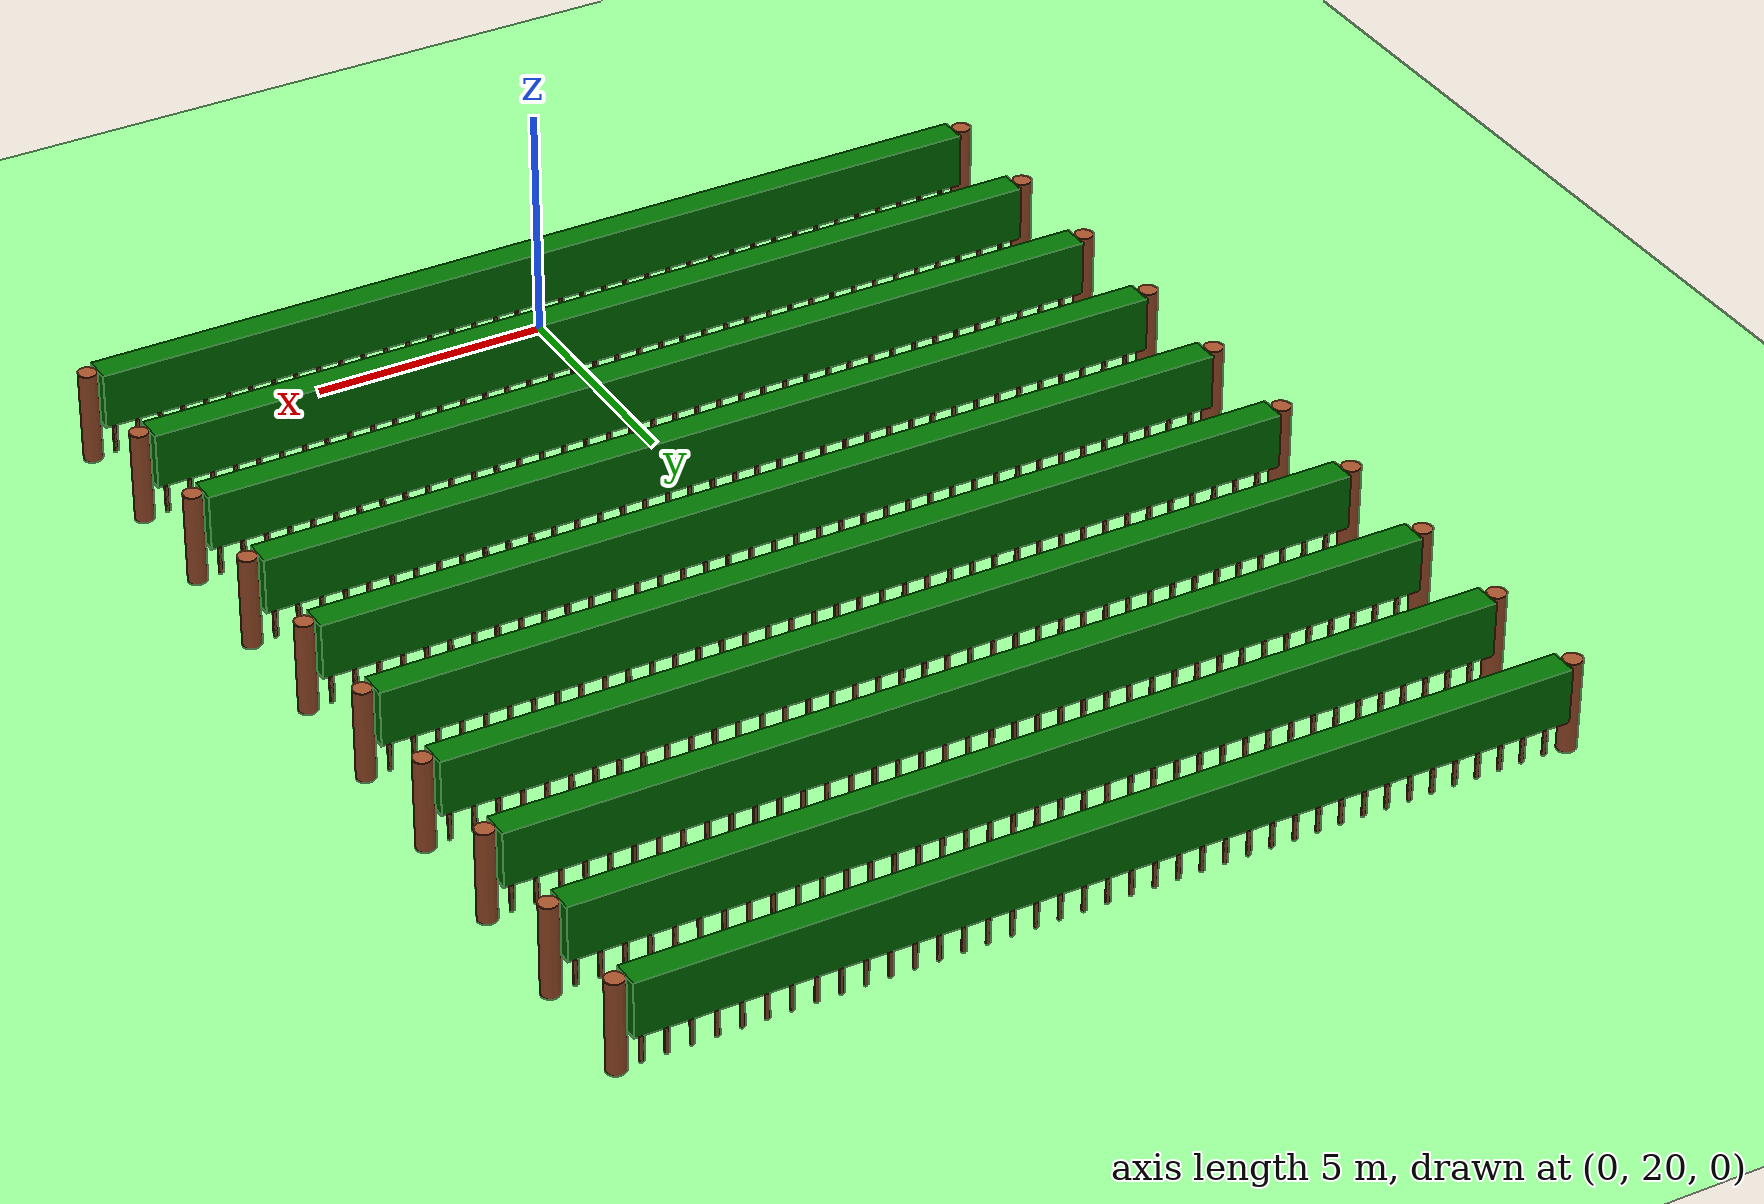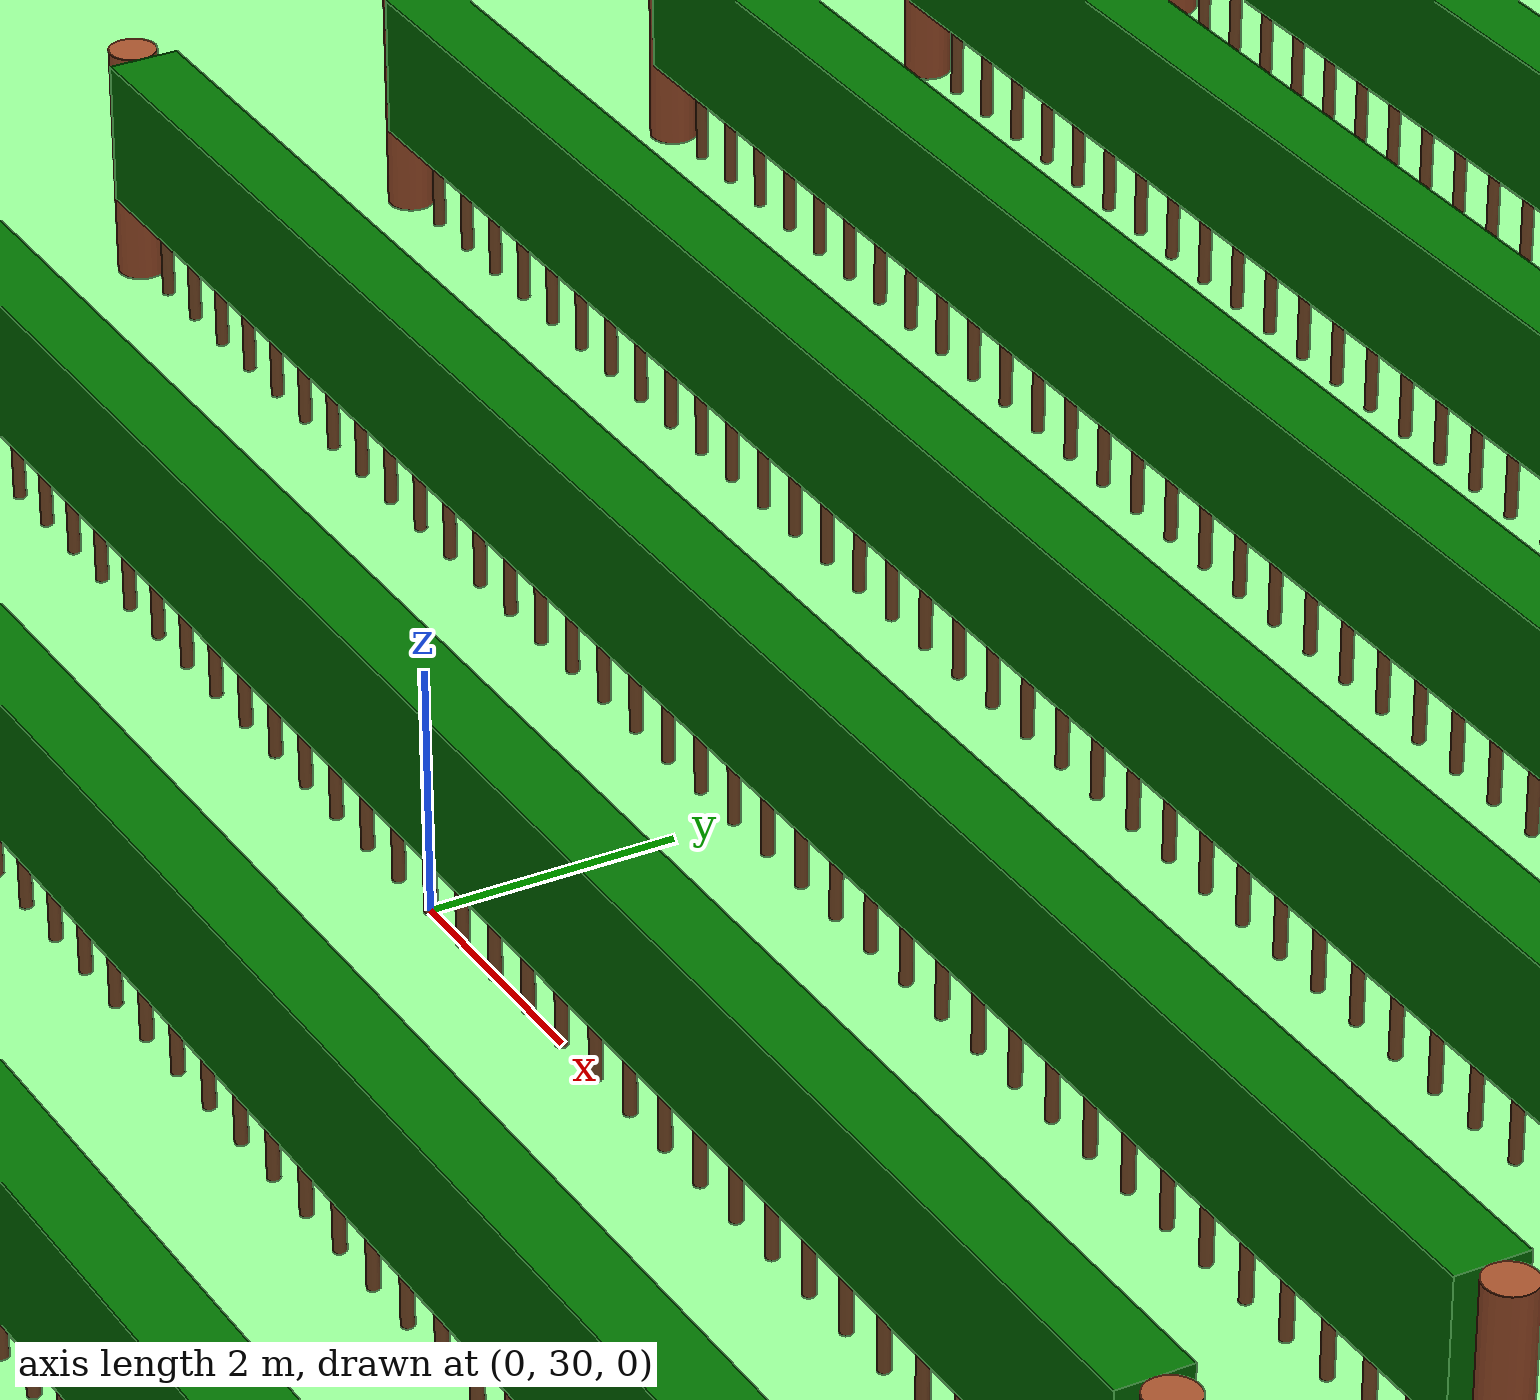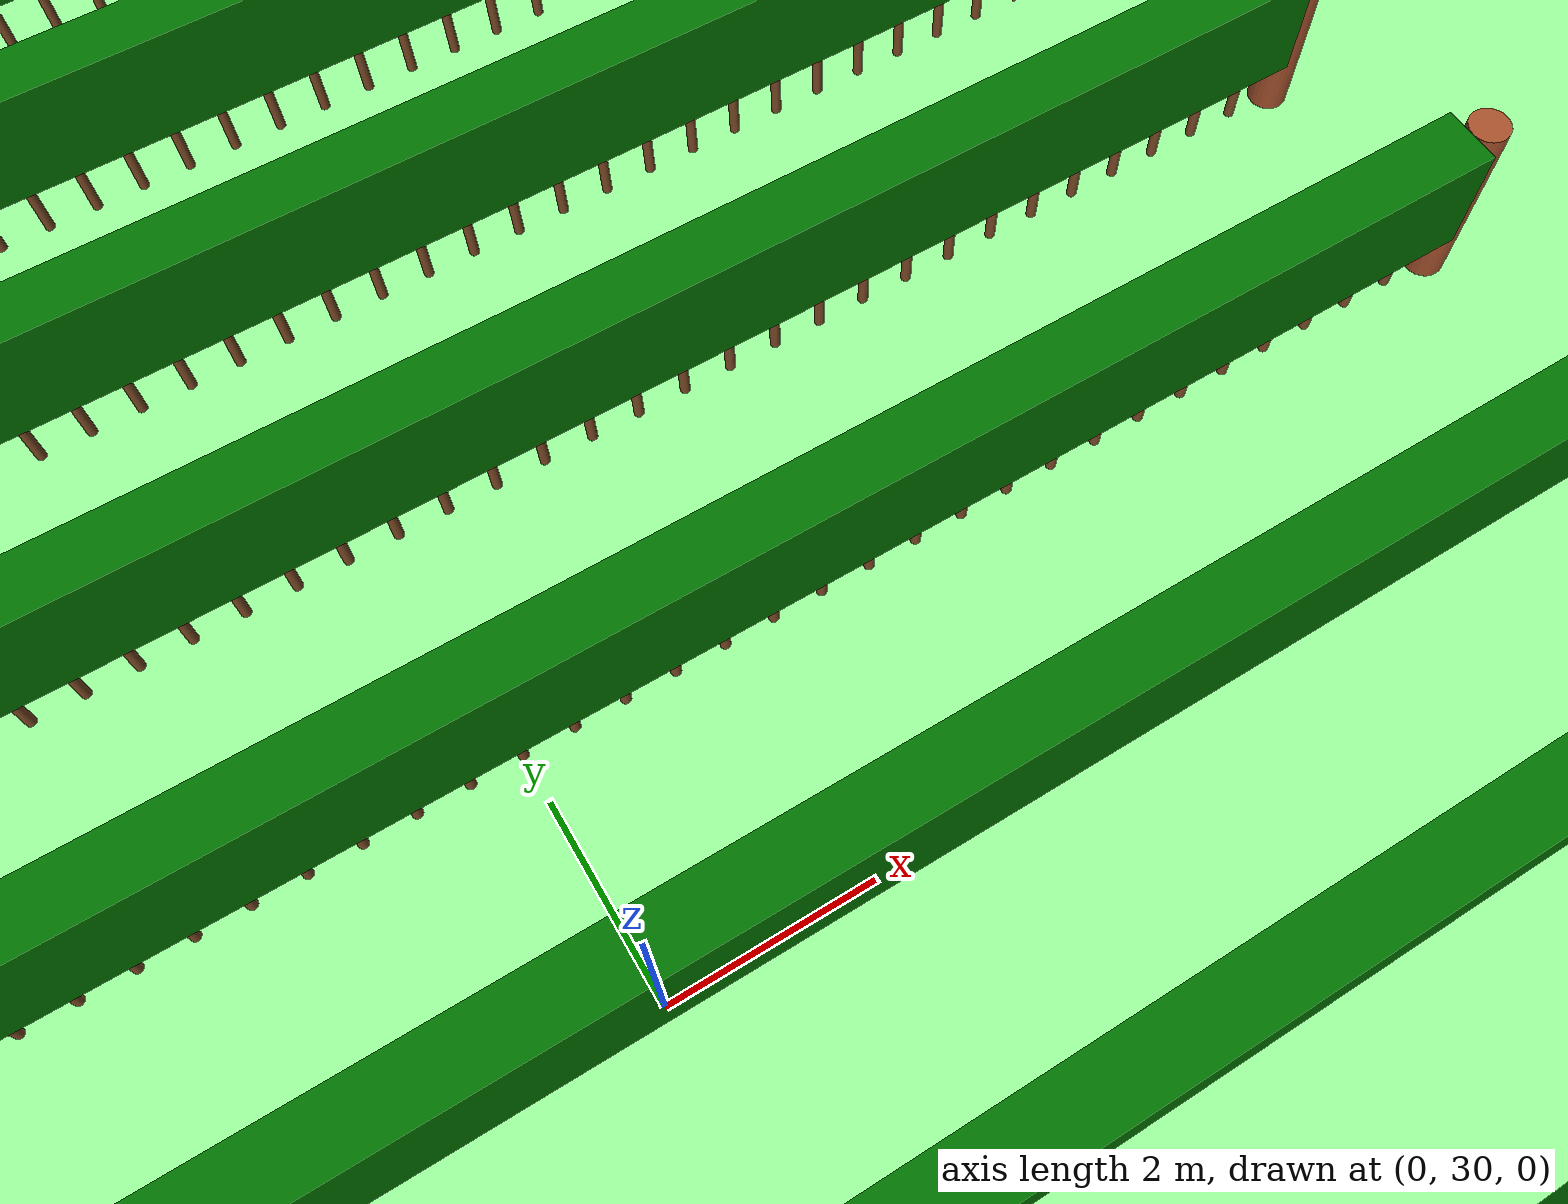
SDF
<?xml version='1.0' encoding='utf-8'?>
<sdf version="1.9">
  <world name="vineyard_world">
    <physics type="ode">
      <max_step_size>0.004</max_step_size>
      <real_time_factor>1.0</real_time_factor>
      <real_time_update_rate>250</real_time_update_rate>
    </physics>
    <gravity>0 0 -9.81</gravity>
    <magnetic_field>6e-06 2.3e-05 -4.2e-05</magnetic_field>
    <atmosphere type="adiabatic" />
    <scene>
      <ambient>0.8 0.5 1 1</ambient>
      <grid>false</grid>
      <sky>
        <clouds>true</clouds>
      </sky>
      <shadows>true</shadows>
    </scene>
    <light name="sun" type="directional">
      <pose>0 0 500 0 0 0</pose>
      <cast_shadows>true</cast_shadows>
      <diffuse>1 1 1 1</diffuse>
      <specular>0.2 0.2 0.2 1</specular>
      <direction>-0.2 0.4 -1</direction>
      <intensity>1.0</intensity>
    </light>
    <model name="vineyard">
      <static>true</static>
      <link name="vineyard_link">
        <collision name="ground_collision">
          <geometry>
            <plane>
              <normal>0 0 1</normal>
              <size>200 200</size>
            </plane>
          </geometry>
        </collision>
        <visual name="ground_visual">
          <geometry>
            <plane>
              <normal>0 0 1</normal>
              <size>200 200</size>
            </plane>
          </geometry>
          <material>
            <ambient>0.5 1.0 0.5 1</ambient>
            <diffuse>0.6 1.0 0.6 1</diffuse>
          </material>
        </visual>
        <collision name="pole_0_20_-10_collision">
          <geometry>
            <cylinder>
              <radius>0.2</radius>
              <length>2.0</length>
            </cylinder>
          </geometry>
          <pose>-10.0 20.0 1.0 0 0 0</pose>
        </collision>
        <visual name="pole_0_20_-10_visual">
          <geometry>
            <cylinder>
              <radius>0.2</radius>
              <length>2.0</length>
            </cylinder>
          </geometry>
          <pose>-10.0 20.0 1.0 0 0 0</pose>
          <material>
            <ambient>0.55 0.27 0.07 1</ambient>
            <diffuse>0.65 0.32 0.17 1</diffuse>
          </material>
        </visual>
        <collision name="pole_0_20_10_collision">
          <geometry>
            <cylinder>
              <radius>0.2</radius>
              <length>2.0</length>
            </cylinder>
          </geometry>
          <pose>10.0 20.0 1.0 0 0 0</pose>
        </collision>
        <visual name="pole_0_20_10_visual">
          <geometry>
            <cylinder>
              <radius>0.2</radius>
              <length>2.0</length>
            </cylinder>
          </geometry>
          <pose>10.0 20.0 1.0 0 0 0</pose>
          <material>
            <ambient>0.55 0.27 0.07 1</ambient>
            <diffuse>0.65 0.32 0.17 1</diffuse>
          </material>
        </visual>
        <collision name="plant_0_1_trunk_collision">
          <geometry>
            <cylinder>
              <radius>0.05</radius>
              <length>0.8</length>
            </cylinder>
          </geometry>
          <pose>-9.5 20.0 0.4 0 0 0</pose>
        </collision>
        <visual name="plant_0_1_trunk_visual">
          <geometry>
            <cylinder>
              <radius>0.05</radius>
              <length>0.8</length>
            </cylinder>
          </geometry>
          <pose>-9.5 20.0 0.4 0 0 0</pose>
          <material>
            <ambient>0.4 0.25 0.1 1</ambient>
            <diffuse>0.5 0.3 0.15 1</diffuse>
          </material>
        </visual>
        <collision name="plant_0_2_trunk_collision">
          <geometry>
            <cylinder>
              <radius>0.05</radius>
              <length>0.8</length>
            </cylinder>
          </geometry>
          <pose>-9.0 20.0 0.4 0 0 0</pose>
        </collision>
        <visual name="plant_0_2_trunk_visual">
          <geometry>
            <cylinder>
              <radius>0.05</radius>
              <length>0.8</length>
            </cylinder>
          </geometry>
          <pose>-9.0 20.0 0.4 0 0 0</pose>
          <material>
            <ambient>0.4 0.25 0.1 1</ambient>
            <diffuse>0.5 0.3 0.15 1</diffuse>
          </material>
        </visual>
        <collision name="plant_0_3_trunk_collision">
          <geometry>
            <cylinder>
              <radius>0.05</radius>
              <length>0.8</length>
            </cylinder>
          </geometry>
          <pose>-8.5 20.0 0.4 0 0 0</pose>
        </collision>
        <visual name="plant_0_3_trunk_visual">
          <geometry>
            <cylinder>
              <radius>0.05</radius>
              <length>0.8</length>
            </cylinder>
          </geometry>
          <pose>-8.5 20.0 0.4 0 0 0</pose>
          <material>
            <ambient>0.4 0.25 0.1 1</ambient>
            <diffuse>0.5 0.3 0.15 1</diffuse>
          </material>
        </visual>
        <collision name="plant_0_4_trunk_collision">
          <geometry>
            <cylinder>
              <radius>0.05</radius>
              <length>0.8</length>
            </cylinder>
          </geometry>
          <pose>-8.0 20.0 0.4 0 0 0</pose>
        </collision>
        <visual name="plant_0_4_trunk_visual">
          <geometry>
            <cylinder>
              <radius>0.05</radius>
              <length>0.8</length>
            </cylinder>
          </geometry>
          <pose>-8.0 20.0 0.4 0 0 0</pose>
          <material>
            <ambient>0.4 0.25 0.1 1</ambient>
            <diffuse>0.5 0.3 0.15 1</diffuse>
          </material>
        </visual>
        <collision name="plant_0_5_trunk_collision">
          <geometry>
            <cylinder>
              <radius>0.05</radius>
              <length>0.8</length>
            </cylinder>
          </geometry>
          <pose>-7.5 20.0 0.4 0 0 0</pose>
        </collision>
        <visual name="plant_0_5_trunk_visual">
          <geometry>
            <cylinder>
              <radius>0.05</radius>
              <length>0.8</length>
            </cylinder>
          </geometry>
          <pose>-7.5 20.0 0.4 0 0 0</pose>
          <material>
            <ambient>0.4 0.25 0.1 1</ambient>
            <diffuse>0.5 0.3 0.15 1</diffuse>
          </material>
        </visual>
        <collision name="plant_0_6_trunk_collision">
          <geometry>
            <cylinder>
              <radius>0.05</radius>
              <length>0.8</length>
            </cylinder>
          </geometry>
          <pose>-7.0 20.0 0.4 0 0 0</pose>
        </collision>
        <visual name="plant_0_6_trunk_visual">
          <geometry>
            <cylinder>
              <radius>0.05</radius>
              <length>0.8</length>
            </cylinder>
          </geometry>
          <pose>-7.0 20.0 0.4 0 0 0</pose>
          <material>
            <ambient>0.4 0.25 0.1 1</ambient>
            <diffuse>0.5 0.3 0.15 1</diffuse>
          </material>
        </visual>
        <collision name="plant_0_7_trunk_collision">
          <geometry>
            <cylinder>
              <radius>0.05</radius>
              <length>0.8</length>
            </cylinder>
          </geometry>
          <pose>-6.5 20.0 0.4 0 0 0</pose>
        </collision>
        <visual name="plant_0_7_trunk_visual">
          <geometry>
            <cylinder>
              <radius>0.05</radius>
              <length>0.8</length>
            </cylinder>
          </geometry>
          <pose>-6.5 20.0 0.4 0 0 0</pose>
          <material>
            <ambient>0.4 0.25 0.1 1</ambient>
            <diffuse>0.5 0.3 0.15 1</diffuse>
          </material>
        </visual>
        <collision name="plant_0_8_trunk_collision">
          <geometry>
            <cylinder>
              <radius>0.05</radius>
              <length>0.8</length>
            </cylinder>
          </geometry>
          <pose>-6.0 20.0 0.4 0 0 0</pose>
        </collision>
        <visual name="plant_0_8_trunk_visual">
          <geometry>
            <cylinder>
              <radius>0.05</radius>
              <length>0.8</length>
            </cylinder>
          </geometry>
          <pose>-6.0 20.0 0.4 0 0 0</pose>
          <material>
            <ambient>0.4 0.25 0.1 1</ambient>
            <diffuse>0.5 0.3 0.15 1</diffuse>
          </material>
        </visual>
        <collision name="plant_0_9_trunk_collision">
          <geometry>
            <cylinder>
              <radius>0.05</radius>
              <length>0.8</length>
            </cylinder>
          </geometry>
          <pose>-5.5 20.0 0.4 0 0 0</pose>
        </collision>
        <visual name="plant_0_9_trunk_visual">
          <geometry>
            <cylinder>
              <radius>0.05</radius>
              <length>0.8</length>
            </cylinder>
          </geometry>
          <pose>-5.5 20.0 0.4 0 0 0</pose>
          <material>
            <ambient>0.4 0.25 0.1 1</ambient>
            <diffuse>0.5 0.3 0.15 1</diffuse>
          </material>
        </visual>
        <collision name="plant_0_10_trunk_collision">
          <geometry>
            <cylinder>
              <radius>0.05</radius>
              <length>0.8</length>
            </cylinder>
          </geometry>
          <pose>-5.0 20.0 0.4 0 0 0</pose>
        </collision>
        <visual name="plant_0_10_trunk_visual">
          <geometry>
            <cylinder>
              <radius>0.05</radius>
              <length>0.8</length>
            </cylinder>
          </geometry>
          <pose>-5.0 20.0 0.4 0 0 0</pose>
          <material>
            <ambient>0.4 0.25 0.1 1</ambient>
            <diffuse>0.5 0.3 0.15 1</diffuse>
          </material>
        </visual>
        <collision name="plant_0_11_trunk_collision">
          <geometry>
            <cylinder>
              <radius>0.05</radius>
              <length>0.8</length>
            </cylinder>
          </geometry>
          <pose>-4.5 20.0 0.4 0 0 0</pose>
        </collision>
        <visual name="plant_0_11_trunk_visual">
          <geometry>
            <cylinder>
              <radius>0.05</radius>
              <length>0.8</length>
            </cylinder>
          </geometry>
          <pose>-4.5 20.0 0.4 0 0 0</pose>
          <material>
            <ambient>0.4 0.25 0.1 1</ambient>
            <diffuse>0.5 0.3 0.15 1</diffuse>
          </material>
        </visual>
        <collision name="plant_0_12_trunk_collision">
          <geometry>
            <cylinder>
              <radius>0.05</radius>
              <length>0.8</length>
            </cylinder>
          </geometry>
          <pose>-4.0 20.0 0.4 0 0 0</pose>
        </collision>
        <visual name="plant_0_12_trunk_visual">
          <geometry>
            <cylinder>
              <radius>0.05</radius>
              <length>0.8</length>
            </cylinder>
          </geometry>
          <pose>-4.0 20.0 0.4 0 0 0</pose>
          <material>
            <ambient>0.4 0.25 0.1 1</ambient>
            <diffuse>0.5 0.3 0.15 1</diffuse>
          </material>
        </visual>
        <collision name="plant_0_13_trunk_collision">
          <geometry>
            <cylinder>
              <radius>0.05</radius>
              <length>0.8</length>
            </cylinder>
          </geometry>
          <pose>-3.5 20.0 0.4 0 0 0</pose>
        </collision>
        <visual name="plant_0_13_trunk_visual">
          <geometry>
            <cylinder>
              <radius>0.05</radius>
              <length>0.8</length>
            </cylinder>
          </geometry>
          <pose>-3.5 20.0 0.4 0 0 0</pose>
          <material>
            <ambient>0.4 0.25 0.1 1</ambient>
            <diffuse>0.5 0.3 0.15 1</diffuse>
          </material>
        </visual>
        <collision name="plant_0_14_trunk_collision">
          <geometry>
            <cylinder>
              <radius>0.05</radius>
              <length>0.8</length>
            </cylinder>
          </geometry>
          <pose>-3.0 20.0 0.4 0 0 0</pose>
        </collision>
        <visual name="plant_0_14_trunk_visual">
          <geometry>
            <cylinder>
              <radius>0.05</radius>
              <length>0.8</length>
            </cylinder>
          </geometry>
          <pose>-3.0 20.0 0.4 0 0 0</pose>
          <material>
            <ambient>0.4 0.25 0.1 1</ambient>
            <diffuse>0.5 0.3 0.15 1</diffuse>
          </material>
        </visual>
        <collision name="plant_0_15_trunk_collision">
          <geometry>
            <cylinder>
              <radius>0.05</radius>
              <length>0.8</length>
            </cylinder>
          </geometry>
          <pose>-2.5 20.0 0.4 0 0 0</pose>
        </collision>
        <visual name="plant_0_15_trunk_visual">
          <geometry>
            <cylinder>
              <radius>0.05</radius>
              <length>0.8</length>
            </cylinder>
          </geometry>
          <pose>-2.5 20.0 0.4 0 0 0</pose>
          <material>
            <ambient>0.4 0.25 0.1 1</ambient>
            <diffuse>0.5 0.3 0.15 1</diffuse>
          </material>
        </visual>
        <collision name="plant_0_16_trunk_collision">
          <geometry>
            <cylinder>
              <radius>0.05</radius>
              <length>0.8</length>
            </cylinder>
          </geometry>
          <pose>-2.0 20.0 0.4 0 0 0</pose>
        </collision>
        <visual name="plant_0_16_trunk_visual">
          <geometry>
            <cylinder>
              <radius>0.05</radius>
              <length>0.8</length>
            </cylinder>
          </geometry>
          <pose>-2.0 20.0 0.4 0 0 0</pose>
          <material>
            <ambient>0.4 0.25 0.1 1</ambient>
            <diffuse>0.5 0.3 0.15 1</diffuse>
          </material>
        </visual>
        <collision name="plant_0_17_trunk_collision">
          <geometry>
            <cylinder>
              <radius>0.05</radius>
              <length>0.8</length>
            </cylinder>
          </geometry>
          <pose>-1.5 20.0 0.4 0 0 0</pose>
        </collision>
        <visual name="plant_0_17_trunk_visual">
          <geometry>
            <cylinder>
              <radius>0.05</radius>
              <length>0.8</length>
            </cylinder>
          </geometry>
          <pose>-1.5 20.0 0.4 0 0 0</pose>
          <material>
            <ambient>0.4 0.25 0.1 1</ambient>
            <diffuse>0.5 0.3 0.15 1</diffuse>
          </material>
        </visual>
        <collision name="plant_0_18_trunk_collision">
          <geometry>
            <cylinder>
              <radius>0.05</radius>
              <length>0.8</length>
            </cylinder>
          </geometry>
          <pose>-1.0 20.0 0.4 0 0 0</pose>
        </collision>
        <visual name="plant_0_18_trunk_visual">
          <geometry>
            <cylinder>
              <radius>0.05</radius>
              <length>0.8</length>
            </cylinder>
          </geometry>
          <pose>-1.0 20.0 0.4 0 0 0</pose>
          <material>
            <ambient>0.4 0.25 0.1 1</ambient>
            <diffuse>0.5 0.3 0.15 1</diffuse>
          </material>
        </visual>
        <collision name="plant_0_19_trunk_collision">
          <geometry>
            <cylinder>
              <radius>0.05</radius>
              <length>0.8</length>
            </cylinder>
          </geometry>
          <pose>-0.5 20.0 0.4 0 0 0</pose>
        </collision>
        <visual name="plant_0_19_trunk_visual">
          <geometry>
            <cylinder>
              <radius>0.05</radius>
              <length>0.8</length>
            </cylinder>
          </geometry>
          <pose>-0.5 20.0 0.4 0 0 0</pose>
          <material>
            <ambient>0.4 0.25 0.1 1</ambient>
            <diffuse>0.5 0.3 0.15 1</diffuse>
          </material>
        </visual>
        <collision name="plant_0_20_trunk_collision">
          <geometry>
            <cylinder>
              <radius>0.05</radius>
              <length>0.8</length>
            </cylinder>
          </geometry>
          <pose>0.0 20.0 0.4 0 0 0</pose>
        </collision>
        <visual name="plant_0_20_trunk_visual">
          <geometry>
            <cylinder>
              <radius>0.05</radius>
              <length>0.8</length>
            </cylinder>
          </geometry>
          <pose>0.0 20.0 0.4 0 0 0</pose>
          <material>
            <ambient>0.4 0.25 0.1 1</ambient>
            <diffuse>0.5 0.3 0.15 1</diffuse>
          </material>
        </visual>
        <collision name="plant_0_21_trunk_collision">
          <geometry>
            <cylinder>
              <radius>0.05</radius>
              <length>0.8</length>
            </cylinder>
          </geometry>
          <pose>0.5 20.0 0.4 0 0 0</pose>
        </collision>
        <visual name="plant_0_21_trunk_visual">
          <geometry>
            <cylinder>
              <radius>0.05</radius>
              <length>0.8</length>
            </cylinder>
          </geometry>
          <pose>0.5 20.0 0.4 0 0 0</pose>
          <material>
            <ambient>0.4 0.25 0.1 1</ambient>
            <diffuse>0.5 0.3 0.15 1</diffuse>
          </material>
        </visual>
        <collision name="plant_0_22_trunk_collision">
          <geometry>
            <cylinder>
              <radius>0.05</radius>
              <length>0.8</length>
            </cylinder>
          </geometry>
          <pose>1.0 20.0 0.4 0 0 0</pose>
        </collision>
        <visual name="plant_0_22_trunk_visual">
          <geometry>
            <cylinder>
              <radius>0.05</radius>
              <length>0.8</length>
            </cylinder>
          </geometry>
          <pose>1.0 20.0 0.4 0 0 0</pose>
          <material>
            <ambient>0.4 0.25 0.1 1</ambient>
            <diffuse>0.5 0.3 0.15 1</diffuse>
          </material>
        </visual>
        <collision name="plant_0_23_trunk_collision">
          <geometry>
            <cylinder>
              <radius>0.05</radius>
              <length>0.8</length>
            </cylinder>
          </geometry>
          <pose>1.5 20.0 0.4 0 0 0</pose>
        </collision>
        <visual name="plant_0_23_trunk_visual">
          <geometry>
            <cylinder>
              <radius>0.05</radius>
              <length>0.8</length>
            </cylinder>
          </geometry>
          <pose>1.5 20.0 0.4 0 0 0</pose>
          <material>
            <ambient>0.4 0.25 0.1 1</ambient>
            <diffuse>0.5 0.3 0.15 1</diffuse>
          </material>
        </visual>
        <collision name="plant_0_24_trunk_collision">
          <geometry>
            <cylinder>
              <radius>0.05</radius>
              <length>0.8</length>
            </cylinder>
          </geometry>
          <pose>2.0 20.0 0.4 0 0 0</pose>
        </collision>
        <visual name="plant_0_24_trunk_visual">
          <geometry>
            <cylinder>
              <radius>0.05</radius>
              <length>0.8</length>
            </cylinder>
          </geometry>
          <pose>2.0 20.0 0.4 0 0 0</pose>
          <material>
            <ambient>0.4 0.25 0.1 1</ambient>
            <diffuse>0.5 0.3 0.15 1</diffuse>
          </material>
        </visual>
        <collision name="plant_0_25_trunk_collision">
          <geometry>
            <cylinder>
              <radius>0.05</radius>
              <length>0.8</length>
            </cylinder>
          </geometry>
          <pose>2.5 20.0 0.4 0 0 0</pose>
        </collision>
        <visual name="plant_0_25_trunk_visual">
          <geometry>
            <cylinder>
              <radius>0.05</radius>
              <length>0.8</length>
            </cylinder>
          </geometry>
          <pose>2.5 20.0 0.4 0 0 0</pose>
          <material>
            <ambient>0.4 0.25 0.1 1</ambient>
            <diffuse>0.5 0.3 0.15 1</diffuse>
          </material>
        </visual>
        <collision name="plant_0_26_trunk_collision">
          <geometry>
            <cylinder>
              <radius>0.05</radius>
              <length>0.8</length>
            </cylinder>
          </geometry>
          <pose>3.0 20.0 0.4 0 0 0</pose>
        </collision>
        <visual name="plant_0_26_trunk_visual">
          <geometry>
            <cylinder>
              <radius>0.05</radius>
              <length>0.8</length>
            </cylinder>
          </geometry>
          <pose>3.0 20.0 0.4 0 0 0</pose>
          <material>
            <ambient>0.4 0.25 0.1 1</ambient>
            <diffuse>0.5 0.3 0.15 1</diffuse>
          </material>
        </visual>
        <collision name="plant_0_27_trunk_collision">
          <geometry>
            <cylinder>
              <radius>0.05</radius>
              <length>0.8</length>
            </cylinder>
          </geometry>
          <pose>3.5 20.0 0.4 0 0 0</pose>
        </collision>
        <visual name="plant_0_27_trunk_visual">
          <geometry>
            <cylinder>
              <radius>0.05</radius>
              <length>0.8</length>
            </cylinder>
          </geometry>
          <pose>3.5 20.0 0.4 0 0 0</pose>
          <material>
            <ambient>0.4 0.25 0.1 1</ambient>
            <diffuse>0.5 0.3 0.15 1</diffuse>
          </material>
        </visual>
        <collision name="plant_0_28_trunk_collision">
          <geometry>
            <cylinder>
              <radius>0.05</radius>
              <length>0.8</length>
            </cylinder>
          </geometry>
          <pose>4.0 20.0 0.4 0 0 0</pose>
        </collision>
        <visual name="plant_0_28_trunk_visual">
          <geometry>
            <cylinder>
              <radius>0.05</radius>
              <length>0.8</length>
            </cylinder>
          </geometry>
          <pose>4.0 20.0 0.4 0 0 0</pose>
          <material>
            <ambient>0.4 0.25 0.1 1</ambient>
            <diffuse>0.5 0.3 0.15 1</diffuse>
          </material>
        </visual>
        <collision name="plant_0_29_trunk_collision">
          <geometry>
            <cylinder>
              <radius>0.05</radius>
              <length>0.8</length>
            </cylinder>
          </geometry>
          <pose>4.5 20.0 0.4 0 0 0</pose>
        </collision>
        <visual name="plant_0_29_trunk_visual">
          <geometry>
            <cylinder>
              <radius>0.05</radius>
              <length>0.8</length>
            </cylinder>
          </geometry>
          <pose>4.5 20.0 0.4 0 0 0</pose>
          <material>
            <ambient>0.4 0.25 0.1 1</ambient>
            <diffuse>0.5 0.3 0.15 1</diffuse>
          </material>
        </visual>
        <collision name="plant_0_30_trunk_collision">
          <geometry>
            <cylinder>
              <radius>0.05</radius>
              <length>0.8</length>
            </cylinder>
          </geometry>
          <pose>5.0 20.0 0.4 0 0 0</pose>
        </collision>
        <visual name="plant_0_30_trunk_visual">
          <geometry>
            <cylinder>
              <radius>0.05</radius>
              <length>0.8</length>
            </cylinder>
          </geometry>
          <pose>5.0 20.0 0.4 0 0 0</pose>
          <material>
            <ambient>0.4 0.25 0.1 1</ambient>
            <diffuse>0.5 0.3 0.15 1</diffuse>
          </material>
        </visual>
        <collision name="plant_0_31_trunk_collision">
          <geometry>
            <cylinder>
              <radius>0.05</radius>
              <length>0.8</length>
            </cylinder>
          </geometry>
          <pose>5.5 20.0 0.4 0 0 0</pose>
        </collision>
        <visual name="plant_0_31_trunk_visual">
          <geometry>
            <cylinder>
              <radius>0.05</radius>
              <length>0.8</length>
            </cylinder>
          </geometry>
          <pose>5.5 20.0 0.4 0 0 0</pose>
          <material>
            <ambient>0.4 0.25 0.1 1</ambient>
            <diffuse>0.5 0.3 0.15 1</diffuse>
          </material>
        </visual>
        <collision name="plant_0_32_trunk_collision">
          <geometry>
            <cylinder>
              <radius>0.05</radius>
              <length>0.8</length>
            </cylinder>
          </geometry>
          <pose>6.0 20.0 0.4 0 0 0</pose>
        </collision>
        <visual name="plant_0_32_trunk_visual">
          <geometry>
            <cylinder>
              <radius>0.05</radius>
              <length>0.8</length>
            </cylinder>
          </geometry>
          <pose>6.0 20.0 0.4 0 0 0</pose>
          <material>
            <ambient>0.4 0.25 0.1 1</ambient>
            <diffuse>0.5 0.3 0.15 1</diffuse>
          </material>
        </visual>
        <collision name="plant_0_33_trunk_collision">
          <geometry>
            <cylinder>
              <radius>0.05</radius>
              <length>0.8</length>
            </cylinder>
          </geometry>
          <pose>6.5 20.0 0.4 0 0 0</pose>
        </collision>
        <visual name="plant_0_33_trunk_visual">
          <geometry>
            <cylinder>
              <radius>0.05</radius>
              <length>0.8</length>
            </cylinder>
          </geometry>
          <pose>6.5 20.0 0.4 0 0 0</pose>
          <material>
            <ambient>0.4 0.25 0.1 1</ambient>
            <diffuse>0.5 0.3 0.15 1</diffuse>
          </material>
        </visual>
        <collision name="plant_0_34_trunk_collision">
          <geometry>
            <cylinder>
              <radius>0.05</radius>
              <length>0.8</length>
            </cylinder>
          </geometry>
          <pose>7.0 20.0 0.4 0 0 0</pose>
        </collision>
        <visual name="plant_0_34_trunk_visual">
          <geometry>
            <cylinder>
              <radius>0.05</radius>
              <length>0.8</length>
            </cylinder>
          </geometry>
          <pose>7.0 20.0 0.4 0 0 0</pose>
          <material>
            <ambient>0.4 0.25 0.1 1</ambient>
            <diffuse>0.5 0.3 0.15 1</diffuse>
          </material>
        </visual>
        <collision name="plant_0_35_trunk_collision">
          <geometry>
            <cylinder>
              <radius>0.05</radius>
              <length>0.8</length>
            </cylinder>
          </geometry>
          <pose>7.5 20.0 0.4 0 0 0</pose>
        </collision>
        <visual name="plant_0_35_trunk_visual">
          <geometry>
            <cylinder>
              <radius>0.05</radius>
              <length>0.8</length>
            </cylinder>
          </geometry>
          <pose>7.5 20.0 0.4 0 0 0</pose>
          <material>
            <ambient>0.4 0.25 0.1 1</ambient>
            <diffuse>0.5 0.3 0.15 1</diffuse>
          </material>
        </visual>
        <collision name="plant_0_36_trunk_collision">
          <geometry>
            <cylinder>
              <radius>0.05</radius>
              <length>0.8</length>
            </cylinder>
          </geometry>
          <pose>8.0 20.0 0.4 0 0 0</pose>
        </collision>
        <visual name="plant_0_36_trunk_visual">
          <geometry>
            <cylinder>
              <radius>0.05</radius>
              <length>0.8</length>
            </cylinder>
          </geometry>
          <pose>8.0 20.0 0.4 0 0 0</pose>
          <material>
            <ambient>0.4 0.25 0.1 1</ambient>
            <diffuse>0.5 0.3 0.15 1</diffuse>
          </material>
        </visual>
        <collision name="plant_0_37_trunk_collision">
          <geometry>
            <cylinder>
              <radius>0.05</radius>
              <length>0.8</length>
            </cylinder>
          </geometry>
          <pose>8.5 20.0 0.4 0 0 0</pose>
        </collision>
        <visual name="plant_0_37_trunk_visual">
          <geometry>
            <cylinder>
              <radius>0.05</radius>
              <length>0.8</length>
            </cylinder>
          </geometry>
          <pose>8.5 20.0 0.4 0 0 0</pose>
          <material>
            <ambient>0.4 0.25 0.1 1</ambient>
            <diffuse>0.5 0.3 0.15 1</diffuse>
          </material>
        </visual>
        <collision name="plant_0_38_trunk_collision">
          <geometry>
            <cylinder>
              <radius>0.05</radius>
              <length>0.8</length>
            </cylinder>
          </geometry>
          <pose>9.0 20.0 0.4 0 0 0</pose>
        </collision>
        <visual name="plant_0_38_trunk_visual">
          <geometry>
            <cylinder>
              <radius>0.05</radius>
              <length>0.8</length>
            </cylinder>
          </geometry>
          <pose>9.0 20.0 0.4 0 0 0</pose>
          <material>
            <ambient>0.4 0.25 0.1 1</ambient>
            <diffuse>0.5 0.3 0.15 1</diffuse>
          </material>
        </visual>
        <collision name="plant_0_39_trunk_collision">
          <geometry>
            <cylinder>
              <radius>0.05</radius>
              <length>0.8</length>
            </cylinder>
          </geometry>
          <pose>9.5 20.0 0.4 0 0 0</pose>
        </collision>
        <visual name="plant_0_39_trunk_visual">
          <geometry>
            <cylinder>
              <radius>0.05</radius>
              <length>0.8</length>
            </cylinder>
          </geometry>
          <pose>9.5 20.0 0.4 0 0 0</pose>
          <material>
            <ambient>0.4 0.25 0.1 1</ambient>
            <diffuse>0.5 0.3 0.15 1</diffuse>
          </material>
        </visual>
        <collision name="crown_row_0_collision">
          <geometry>
            <box>
              <size>19.6 0.6 1.2</size>
            </box>
          </geometry>
          <pose>0.0 20.0 1.4 0 0 0</pose>
        </collision>
        <visual name="crown_row_0_visual">
          <geometry>
            <box>
              <size>19.6 0.6 1.2</size>
            </box>
          </geometry>
          <pose>0.0 20.0 1.4 0 0 0</pose>
          <material>
            <ambient>0.0 0.25 0.0 1</ambient>
            <diffuse>0.0 0.45 0.0 1</diffuse>
          </material>
        </visual>
        <collision name="pole_1_22_-10_collision">
          <geometry>
            <cylinder>
              <radius>0.2</radius>
              <length>2.0</length>
            </cylinder>
          </geometry>
          <pose>-10.0 22.5 1.0 0 0 0</pose>
        </collision>
        <visual name="pole_1_22_-10_visual">
          <geometry>
            <cylinder>
              <radius>0.2</radius>
              <length>2.0</length>
            </cylinder>
          </geometry>
          <pose>-10.0 22.5 1.0 0 0 0</pose>
          <material>
            <ambient>0.55 0.27 0.07 1</ambient>
            <diffuse>0.65 0.32 0.17 1</diffuse>
          </material>
        </visual>
        <collision name="pole_1_22_10_collision">
          <geometry>
            <cylinder>
              <radius>0.2</radius>
              <length>2.0</length>
            </cylinder>
          </geometry>
          <pose>10.0 22.5 1.0 0 0 0</pose>
        </collision>
        <visual name="pole_1_22_10_visual">
          <geometry>
            <cylinder>
              <radius>0.2</radius>
              <length>2.0</length>
            </cylinder>
          </geometry>
          <pose>10.0 22.5 1.0 0 0 0</pose>
          <material>
            <ambient>0.55 0.27 0.07 1</ambient>
            <diffuse>0.65 0.32 0.17 1</diffuse>
          </material>
        </visual>
        <collision name="plant_1_1_trunk_collision">
          <geometry>
            <cylinder>
              <radius>0.05</radius>
              <length>0.8</length>
            </cylinder>
          </geometry>
          <pose>-9.5 22.5 0.4 0 0 0</pose>
        </collision>
        <visual name="plant_1_1_trunk_visual">
          <geometry>
            <cylinder>
              <radius>0.05</radius>
              <length>0.8</length>
            </cylinder>
          </geometry>
          <pose>-9.5 22.5 0.4 0 0 0</pose>
          <material>
            <ambient>0.4 0.25 0.1 1</ambient>
            <diffuse>0.5 0.3 0.15 1</diffuse>
          </material>
        </visual>
        <collision name="plant_1_2_trunk_collision">
          <geometry>
            <cylinder>
              <radius>0.05</radius>
              <length>0.8</length>
            </cylinder>
          </geometry>
          <pose>-9.0 22.5 0.4 0 0 0</pose>
        </collision>
        <visual name="plant_1_2_trunk_visual">
          <geometry>
            <cylinder>
              <radius>0.05</radius>
              <length>0.8</length>
            </cylinder>
          </geometry>
          <pose>-9.0 22.5 0.4 0 0 0</pose>
          <material>
            <ambient>0.4 0.25 0.1 1</ambient>
            <diffuse>0.5 0.3 0.15 1</diffuse>
          </material>
        </visual>
        <collision name="plant_1_3_trunk_collision">
          <geometry>
            <cylinder>
              <radius>0.05</radius>
              <length>0.8</length>
            </cylinder>
          </geometry>
          <pose>-8.5 22.5 0.4 0 0 0</pose>
        </collision>
        <visual name="plant_1_3_trunk_visual">
          <geometry>
            <cylinder>
              <radius>0.05</radius>
              <length>0.8</length>
            </cylinder>
          </geometry>
          <pose>-8.5 22.5 0.4 0 0 0</pose>
          <material>
            <ambient>0.4 0.25 0.1 1</ambient>
            <diffuse>0.5 0.3 0.15 1</diffuse>
          </material>
        </visual>
        <collision name="plant_1_4_trunk_collision">
          <geometry>
            <cylinder>
              <radius>0.05</radius>
              <length>0.8</length>
            </cylinder>
          </geometry>
          <pose>-8.0 22.5 0.4 0 0 0</pose>
        </collision>
        <visual name="plant_1_4_trunk_visual">
          <geometry>
            <cylinder>
              <radius>0.05</radius>
              <length>0.8</length>
            </cylinder>
          </geometry>
          <pose>-8.0 22.5 0.4 0 0 0</pose>
          <material>
            <ambient>0.4 0.25 0.1 1</ambient>
            <diffuse>0.5 0.3 0.15 1</diffuse>
          </material>
        </visual>
        <collision name="plant_1_5_trunk_collision">
          <geometry>
            <cylinder>
              <radius>0.05</radius>
              <length>0.8</length>
            </cylinder>
          </geometry>
          <pose>-7.5 22.5 0.4 0 0 0</pose>
        </collision>
        <visual name="plant_1_5_trunk_visual">
          <geometry>
            <cylinder>
              <radius>0.05</radius>
              <length>0.8</length>
            </cylinder>
          </geometry>
          <pose>-7.5 22.5 0.4 0 0 0</pose>
          <material>
            <ambient>0.4 0.25 0.1 1</ambient>
            <diffuse>0.5 0.3 0.15 1</diffuse>
          </material>
        </visual>
        <collision name="plant_1_6_trunk_collision">
          <geometry>
            <cylinder>
              <radius>0.05</radius>
              <length>0.8</length>
            </cylinder>
          </geometry>
          <pose>-7.0 22.5 0.4 0 0 0</pose>
        </collision>
        <visual name="plant_1_6_trunk_visual">
          <geometry>
            <cylinder>
              <radius>0.05</radius>
              <length>0.8</length>
            </cylinder>
          </geometry>
          <pose>-7.0 22.5 0.4 0 0 0</pose>
          <material>
            <ambient>0.4 0.25 0.1 1</ambient>
            <diffuse>0.5 0.3 0.15 1</diffuse>
          </material>
        </visual>
        <collision name="plant_1_7_trunk_collision">
          <geometry>
            <cylinder>
              <radius>0.05</radius>
              <length>0.8</length>
            </cylinder>
          </geometry>
          <pose>-6.5 22.5 0.4 0 0 0</pose>
        </collision>
        <visual name="plant_1_7_trunk_visual">
          <geometry>
            <cylinder>
              <radius>0.05</radius>
              <length>0.8</length>
            </cylinder>
          </geometry>
          <pose>-6.5 22.5 0.4 0 0 0</pose>
          <material>
            <ambient>0.4 0.25 0.1 1</ambient>
            <diffuse>0.5 0.3 0.15 1</diffuse>
          </material>
        </visual>
        <collision name="plant_1_8_trunk_collision">
          <geometry>
            <cylinder>
              <radius>0.05</radius>
              <length>0.8</length>
            </cylinder>
          </geometry>
          <pose>-6.0 22.5 0.4 0 0 0</pose>
        </collision>
        <visual name="plant_1_8_trunk_visual">
          <geometry>
            <cylinder>
              <radius>0.05</radius>
              <length>0.8</length>
            </cylinder>
          </geometry>
          <pose>-6.0 22.5 0.4 0 0 0</pose>
          <material>
            <ambient>0.4 0.25 0.1 1</ambient>
            <diffuse>0.5 0.3 0.15 1</diffuse>
          </material>
        </visual>
        <collision name="plant_1_9_trunk_collision">
          <geometry>
            <cylinder>
              <radius>0.05</radius>
              <length>0.8</length>
            </cylinder>
          </geometry>
          <pose>-5.5 22.5 0.4 0 0 0</pose>
        </collision>
        <visual name="plant_1_9_trunk_visual">
          <geometry>
            <cylinder>
              <radius>0.05</radius>
              <length>0.8</length>
            </cylinder>
          </geometry>
          <pose>-5.5 22.5 0.4 0 0 0</pose>
          <material>
            <ambient>0.4 0.25 0.1 1</ambient>
            <diffuse>0.5 0.3 0.15 1</diffuse>
          </material>
        </visual>
        <collision name="plant_1_10_trunk_collision">
          <geometry>
            <cylinder>
              <radius>0.05</radius>
              <length>0.8</length>
            </cylinder>
          </geometry>
          <pose>-5.0 22.5 0.4 0 0 0</pose>
        </collision>
        <visual name="plant_1_10_trunk_visual">
          <geometry>
            <cylinder>
              <radius>0.05</radius>
              <length>0.8</length>
            </cylinder>
          </geometry>
          <pose>-5.0 22.5 0.4 0 0 0</pose>
          <material>
            <ambient>0.4 0.25 0.1 1</ambient>
            <diffuse>0.5 0.3 0.15 1</diffuse>
          </material>
        </visual>
        <collision name="plant_1_11_trunk_collision">
          <geometry>
            <cylinder>
              <radius>0.05</radius>
              <length>0.8</length>
            </cylinder>
          </geometry>
          <pose>-4.5 22.5 0.4 0 0 0</pose>
        </collision>
        <visual name="plant_1_11_trunk_visual">
          <geometry>
            <cylinder>
              <radius>0.05</radius>
              <length>0.8</length>
            </cylinder>
          </geometry>
          <pose>-4.5 22.5 0.4 0 0 0</pose>
          <material>
            <ambient>0.4 0.25 0.1 1</ambient>
            <diffuse>0.5 0.3 0.15 1</diffuse>
          </material>
        </visual>
        <collision name="plant_1_12_trunk_collision">
          <geometry>
            <cylinder>
              <radius>0.05</radius>
              <length>0.8</length>
            </cylinder>
          </geometry>
          <pose>-4.0 22.5 0.4 0 0 0</pose>
        </collision>
        <visual name="plant_1_12_trunk_visual">
          <geometry>
            <cylinder>
              <radius>0.05</radius>
              <length>0.8</length>
            </cylinder>
          </geometry>
          <pose>-4.0 22.5 0.4 0 0 0</pose>
          <material>
            <ambient>0.4 0.25 0.1 1</ambient>
            <diffuse>0.5 0.3 0.15 1</diffuse>
          </material>
        </visual>
        <collision name="plant_1_13_trunk_collision">
          <geometry>
            <cylinder>
              <radius>0.05</radius>
              <length>0.8</length>
            </cylinder>
          </geometry>
          <pose>-3.5 22.5 0.4 0 0 0</pose>
        </collision>
        <visual name="plant_1_13_trunk_visual">
          <geometry>
            <cylinder>
              <radius>0.05</radius>
              <length>0.8</length>
            </cylinder>
          </geometry>
          <pose>-3.5 22.5 0.4 0 0 0</pose>
          <material>
            <ambient>0.4 0.25 0.1 1</ambient>
            <diffuse>0.5 0.3 0.15 1</diffuse>
          </material>
        </visual>
        <collision name="plant_1_14_trunk_collision">
          <geometry>
            <cylinder>
              <radius>0.05</radius>
              <length>0.8</length>
            </cylinder>
          </geometry>
          <pose>-3.0 22.5 0.4 0 0 0</pose>
        </collision>
        <visual name="plant_1_14_trunk_visual">
          <geometry>
            <cylinder>
              <radius>0.05</radius>
              <length>0.8</length>
            </cylinder>
          </geometry>
          <pose>-3.0 22.5 0.4 0 0 0</pose>
          <material>
            <ambient>0.4 0.25 0.1 1</ambient>
            <diffuse>0.5 0.3 0.15 1</diffuse>
          </material>
        </visual>
        <collision name="plant_1_15_trunk_collision">
          <geometry>
            <cylinder>
              <radius>0.05</radius>
              <length>0.8</length>
            </cylinder>
          </geometry>
          <pose>-2.5 22.5 0.4 0 0 0</pose>
        </collision>
        <visual name="plant_1_15_trunk_visual">
          <geometry>
            <cylinder>
              <radius>0.05</radius>
              <length>0.8</length>
            </cylinder>
          </geometry>
          <pose>-2.5 22.5 0.4 0 0 0</pose>
          <material>
            <ambient>0.4 0.25 0.1 1</ambient>
            <diffuse>0.5 0.3 0.15 1</diffuse>
          </material>
        </visual>
        <collision name="plant_1_16_trunk_collision">
          <geometry>
            <cylinder>
              <radius>0.05</radius>
              <length>0.8</length>
            </cylinder>
          </geometry>
          <pose>-2.0 22.5 0.4 0 0 0</pose>
        </collision>
        <visual name="plant_1_16_trunk_visual">
          <geometry>
            <cylinder>
              <radius>0.05</radius>
              <length>0.8</length>
            </cylinder>
          </geometry>
          <pose>-2.0 22.5 0.4 0 0 0</pose>
          <material>
            <ambient>0.4 0.25 0.1 1</ambient>
            <diffuse>0.5 0.3 0.15 1</diffuse>
          </material>
        </visual>
        <collision name="plant_1_17_trunk_collision">
          <geometry>
            <cylinder>
              <radius>0.05</radius>
              <length>0.8</length>
            </cylinder>
          </geometry>
          <pose>-1.5 22.5 0.4 0 0 0</pose>
        </collision>
        <visual name="plant_1_17_trunk_visual">
          <geometry>
            <cylinder>
              <radius>0.05</radius>
              <length>0.8</length>
            </cylinder>
          </geometry>
          <pose>-1.5 22.5 0.4 0 0 0</pose>
          <material>
            <ambient>0.4 0.25 0.1 1</ambient>
            <diffuse>0.5 0.3 0.15 1</diffuse>
          </material>
        </visual>
        <collision name="plant_1_18_trunk_collision">
          <geometry>
            <cylinder>
              <radius>0.05</radius>
              <length>0.8</length>
            </cylinder>
          </geometry>
          <pose>-1.0 22.5 0.4 0 0 0</pose>
        </collision>
        <visual name="plant_1_18_trunk_visual">
          <geometry>
            <cylinder>
              <radius>0.05</radius>
              <length>0.8</length>
            </cylinder>
          </geometry>
          <pose>-1.0 22.5 0.4 0 0 0</pose>
          <material>
            <ambient>0.4 0.25 0.1 1</ambient>
            <diffuse>0.5 0.3 0.15 1</diffuse>
          </material>
        </visual>
        <collision name="plant_1_19_trunk_collision">
          <geometry>
            <cylinder>
              <radius>0.05</radius>
              <length>0.8</length>
            </cylinder>
          </geometry>
          <pose>-0.5 22.5 0.4 0 0 0</pose>
        </collision>
        <visual name="plant_1_19_trunk_visual">
          <geometry>
            <cylinder>
              <radius>0.05</radius>
              <length>0.8</length>
            </cylinder>
          </geometry>
          <pose>-0.5 22.5 0.4 0 0 0</pose>
          <material>
            <ambient>0.4 0.25 0.1 1</ambient>
            <diffuse>0.5 0.3 0.15 1</diffuse>
          </material>
        </visual>
        <collision name="plant_1_20_trunk_collision">
          <geometry>
            <cylinder>
              <radius>0.05</radius>
              <length>0.8</length>
            </cylinder>
          </geometry>
          <pose>0.0 22.5 0.4 0 0 0</pose>
        </collision>
        <visual name="plant_1_20_trunk_visual">
          <geometry>
            <cylinder>
              <radius>0.05</radius>
              <length>0.8</length>
            </cylinder>
          </geometry>
          <pose>0.0 22.5 0.4 0 0 0</pose>
          <material>
            <ambient>0.4 0.25 0.1 1</ambient>
            <diffuse>0.5 0.3 0.15 1</diffuse>
          </material>
        </visual>
        <collision name="plant_1_21_trunk_collision">
          <geometry>
            <cylinder>
              <radius>0.05</radius>
              <length>0.8</length>
            </cylinder>
          </geometry>
          <pose>0.5 22.5 0.4 0 0 0</pose>
        </collision>
        <visual name="plant_1_21_trunk_visual">
          <geometry>
            <cylinder>
              <radius>0.05</radius>
              <length>0.8</length>
            </cylinder>
          </geometry>
          <pose>0.5 22.5 0.4 0 0 0</pose>
          <material>
            <ambient>0.4 0.25 0.1 1</ambient>
            <diffuse>0.5 0.3 0.15 1</diffuse>
          </material>
        </visual>
        <collision name="plant_1_22_trunk_collision">
          <geometry>
            <cylinder>
              <radius>0.05</radius>
              <length>0.8</length>
            </cylinder>
          </geometry>
          <pose>1.0 22.5 0.4 0 0 0</pose>
        </collision>
        <visual name="plant_1_22_trunk_visual">
          <geometry>
            <cylinder>
              <radius>0.05</radius>
              <length>0.8</length>
            </cylinder>
          </geometry>
          <pose>1.0 22.5 0.4 0 0 0</pose>
          <material>
            <ambient>0.4 0.25 0.1 1</ambient>
            <diffuse>0.5 0.3 0.15 1</diffuse>
          </material>
        </visual>
        <collision name="plant_1_23_trunk_collision">
          <geometry>
            <cylinder>
              <radius>0.05</radius>
              <length>0.8</length>
            </cylinder>
          </geometry>
          <pose>1.5 22.5 0.4 0 0 0</pose>
        </collision>
        <visual name="plant_1_23_trunk_visual">
          <geometry>
            <cylinder>
              <radius>0.05</radius>
              <length>0.8</length>
            </cylinder>
          </geometry>
          <pose>1.5 22.5 0.4 0 0 0</pose>
          <material>
            <ambient>0.4 0.25 0.1 1</ambient>
            <diffuse>0.5 0.3 0.15 1</diffuse>
          </material>
        </visual>
        <collision name="plant_1_24_trunk_collision">
          <geometry>
            <cylinder>
              <radius>0.05</radius>
              <length>0.8</length>
            </cylinder>
          </geometry>
          <pose>2.0 22.5 0.4 0 0 0</pose>
        </collision>
        <visual name="plant_1_24_trunk_visual">
          <geometry>
            <cylinder>
              <radius>0.05</radius>
              <length>0.8</length>
            </cylinder>
          </geometry>
          <pose>2.0 22.5 0.4 0 0 0</pose>
          <material>
            <ambient>0.4 0.25 0.1 1</ambient>
            <diffuse>0.5 0.3 0.15 1</diffuse>
          </material>
        </visual>
        <collision name="plant_1_25_trunk_collision">
          <geometry>
            <cylinder>
              <radius>0.05</radius>
              <length>0.8</length>
            </cylinder>
          </geometry>
          <pose>2.5 22.5 0.4 0 0 0</pose>
        </collision>
        <visual name="plant_1_25_trunk_visual">
          <geometry>
            <cylinder>
              <radius>0.05</radius>
              <length>0.8</length>
            </cylinder>
          </geometry>
          <pose>2.5 22.5 0.4 0 0 0</pose>
          <material>
            <ambient>0.4 0.25 0.1 1</ambient>
            <diffuse>0.5 0.3 0.15 1</diffuse>
          </material>
        </visual>
        <collision name="plant_1_26_trunk_collision">
          <geometry>
            <cylinder>
              <radius>0.05</radius>
              <length>0.8</length>
            </cylinder>
          </geometry>
          <pose>3.0 22.5 0.4 0 0 0</pose>
        </collision>
        <visual name="plant_1_26_trunk_visual">
          <geometry>
            <cylinder>
              <radius>0.05</radius>
              <length>0.8</length>
            </cylinder>
          </geometry>
          <pose>3.0 22.5 0.4 0 0 0</pose>
          <material>
            <ambient>0.4 0.25 0.1 1</ambient>
            <diffuse>0.5 0.3 0.15 1</diffuse>
          </material>
        </visual>
        <collision name="plant_1_27_trunk_collision">
          <geometry>
            <cylinder>
              <radius>0.05</radius>
              <length>0.8</length>
            </cylinder>
          </geometry>
          <pose>3.5 22.5 0.4 0 0 0</pose>
        </collision>
        <visual name="plant_1_27_trunk_visual">
          <geometry>
            <cylinder>
              <radius>0.05</radius>
              <length>0.8</length>
            </cylinder>
          </geometry>
          <pose>3.5 22.5 0.4 0 0 0</pose>
          <material>
            <ambient>0.4 0.25 0.1 1</ambient>
            <diffuse>0.5 0.3 0.15 1</diffuse>
          </material>
        </visual>
        <collision name="plant_1_28_trunk_collision">
          <geometry>
            <cylinder>
              <radius>0.05</radius>
              <length>0.8</length>
            </cylinder>
          </geometry>
          <pose>4.0 22.5 0.4 0 0 0</pose>
        </collision>
        <visual name="plant_1_28_trunk_visual">
          <geometry>
            <cylinder>
              <radius>0.05</radius>
              <length>0.8</length>
            </cylinder>
          </geometry>
          <pose>4.0 22.5 0.4 0 0 0</pose>
          <material>
            <ambient>0.4 0.25 0.1 1</ambient>
            <diffuse>0.5 0.3 0.15 1</diffuse>
          </material>
        </visual>
        <collision name="plant_1_29_trunk_collision">
          <geometry>
            <cylinder>
              <radius>0.05</radius>
              <length>0.8</length>
            </cylinder>
          </geometry>
          <pose>4.5 22.5 0.4 0 0 0</pose>
        </collision>
        <visual name="plant_1_29_trunk_visual">
          <geometry>
            <cylinder>
              <radius>0.05</radius>
              <length>0.8</length>
            </cylinder>
          </geometry>
          <pose>4.5 22.5 0.4 0 0 0</pose>
          <material>
            <ambient>0.4 0.25 0.1 1</ambient>
            <diffuse>0.5 0.3 0.15 1</diffuse>
          </material>
        </visual>
        <collision name="plant_1_30_trunk_collision">
          <geometry>
            <cylinder>
              <radius>0.05</radius>
              <length>0.8</length>
            </cylinder>
          </geometry>
          <pose>5.0 22.5 0.4 0 0 0</pose>
        </collision>
        <visual name="plant_1_30_trunk_visual">
          <geometry>
            <cylinder>
              <radius>0.05</radius>
              <length>0.8</length>
            </cylinder>
          </geometry>
          <pose>5.0 22.5 0.4 0 0 0</pose>
          <material>
            <ambient>0.4 0.25 0.1 1</ambient>
            <diffuse>0.5 0.3 0.15 1</diffuse>
          </material>
        </visual>
        <collision name="plant_1_31_trunk_collision">
          <geometry>
            <cylinder>
              <radius>0.05</radius>
              <length>0.8</length>
            </cylinder>
          </geometry>
          <pose>5.5 22.5 0.4 0 0 0</pose>
        </collision>
        <visual name="plant_1_31_trunk_visual">
          <geometry>
            <cylinder>
              <radius>0.05</radius>
              <length>0.8</length>
            </cylinder>
          </geometry>
          <pose>5.5 22.5 0.4 0 0 0</pose>
          <material>
            <ambient>0.4 0.25 0.1 1</ambient>
            <diffuse>0.5 0.3 0.15 1</diffuse>
          </material>
        </visual>
        <collision name="plant_1_32_trunk_collision">
          <geometry>
            <cylinder>
              <radius>0.05</radius>
              <length>0.8</length>
            </cylinder>
          </geometry>
          <pose>6.0 22.5 0.4 0 0 0</pose>
        </collision>
        <visual name="plant_1_32_trunk_visual">
          <geometry>
            <cylinder>
              <radius>0.05</radius>
              <length>0.8</length>
            </cylinder>
          </geometry>
          <pose>6.0 22.5 0.4 0 0 0</pose>
          <material>
            <ambient>0.4 0.25 0.1 1</ambient>
            <diffuse>0.5 0.3 0.15 1</diffuse>
          </material>
        </visual>
        <collision name="plant_1_33_trunk_collision">
          <geometry>
            <cylinder>
              <radius>0.05</radius>
              <length>0.8</length>
            </cylinder>
          </geometry>
          <pose>6.5 22.5 0.4 0 0 0</pose>
        </collision>
        <visual name="plant_1_33_trunk_visual">
          <geometry>
            <cylinder>
              <radius>0.05</radius>
              <length>0.8</length>
            </cylinder>
          </geometry>
          <pose>6.5 22.5 0.4 0 0 0</pose>
          <material>
            <ambient>0.4 0.25 0.1 1</ambient>
            <diffuse>0.5 0.3 0.15 1</diffuse>
          </material>
        </visual>
        <collision name="plant_1_34_trunk_collision">
          <geometry>
            <cylinder>
              <radius>0.05</radius>
              <length>0.8</length>
            </cylinder>
          </geometry>
          <pose>7.0 22.5 0.4 0 0 0</pose>
        </collision>
        <visual name="plant_1_34_trunk_visual">
          <geometry>
            <cylinder>
              <radius>0.05</radius>
              <length>0.8</length>
            </cylinder>
          </geometry>
          <pose>7.0 22.5 0.4 0 0 0</pose>
          <material>
            <ambient>0.4 0.25 0.1 1</ambient>
            <diffuse>0.5 0.3 0.15 1</diffuse>
          </material>
        </visual>
        <collision name="plant_1_35_trunk_collision">
          <geometry>
            <cylinder>
              <radius>0.05</radius>
              <length>0.8</length>
            </cylinder>
          </geometry>
          <pose>7.5 22.5 0.4 0 0 0</pose>
        </collision>
        <visual name="plant_1_35_trunk_visual">
          <geometry>
            <cylinder>
              <radius>0.05</radius>
              <length>0.8</length>
            </cylinder>
          </geometry>
          <pose>7.5 22.5 0.4 0 0 0</pose>
          <material>
            <ambient>0.4 0.25 0.1 1</ambient>
            <diffuse>0.5 0.3 0.15 1</diffuse>
          </material>
        </visual>
        <collision name="plant_1_36_trunk_collision">
          <geometry>
            <cylinder>
              <radius>0.05</radius>
              <length>0.8</length>
            </cylinder>
          </geometry>
          <pose>8.0 22.5 0.4 0 0 0</pose>
        </collision>
        <visual name="plant_1_36_trunk_visual">
          <geometry>
            <cylinder>
              <radius>0.05</radius>
              <length>0.8</length>
            </cylinder>
          </geometry>
          <pose>8.0 22.5 0.4 0 0 0</pose>
          <material>
            <ambient>0.4 0.25 0.1 1</ambient>
            <diffuse>0.5 0.3 0.15 1</diffuse>
          </material>
        </visual>
        <collision name="plant_1_37_trunk_collision">
          <geometry>
            <cylinder>
              <radius>0.05</radius>
              <length>0.8</length>
            </cylinder>
          </geometry>
          <pose>8.5 22.5 0.4 0 0 0</pose>
        </collision>
        <visual name="plant_1_37_trunk_visual">
          <geometry>
            <cylinder>
              <radius>0.05</radius>
              <length>0.8</length>
            </cylinder>
          </geometry>
          <pose>8.5 22.5 0.4 0 0 0</pose>
          <material>
            <ambient>0.4 0.25 0.1 1</ambient>
            <diffuse>0.5 0.3 0.15 1</diffuse>
          </material>
        </visual>
        <collision name="plant_1_38_trunk_collision">
          <geometry>
            <cylinder>
              <radius>0.05</radius>
              <length>0.8</length>
            </cylinder>
          </geometry>
          <pose>9.0 22.5 0.4 0 0 0</pose>
        </collision>
        <visual name="plant_1_38_trunk_visual">
          <geometry>
            <cylinder>
              <radius>0.05</radius>
              <length>0.8</length>
            </cylinder>
          </geometry>
          <pose>9.0 22.5 0.4 0 0 0</pose>
          <material>
            <ambient>0.4 0.25 0.1 1</ambient>
            <diffuse>0.5 0.3 0.15 1</diffuse>
          </material>
        </visual>
        <collision name="plant_1_39_trunk_collision">
          <geometry>
            <cylinder>
              <radius>0.05</radius>
              <length>0.8</length>
            </cylinder>
          </geometry>
          <pose>9.5 22.5 0.4 0 0 0</pose>
        </collision>
        <visual name="plant_1_39_trunk_visual">
          <geometry>
            <cylinder>
              <radius>0.05</radius>
              <length>0.8</length>
            </cylinder>
          </geometry>
          <pose>9.5 22.5 0.4 0 0 0</pose>
          <material>
            <ambient>0.4 0.25 0.1 1</ambient>
            <diffuse>0.5 0.3 0.15 1</diffuse>
          </material>
        </visual>
        <collision name="crown_row_1_collision">
          <geometry>
            <box>
              <size>19.6 0.6 1.2</size>
            </box>
          </geometry>
          <pose>0.0 22.5 1.4 0 0 0</pose>
        </collision>
        <visual name="crown_row_1_visual">
          <geometry>
            <box>
              <size>19.6 0.6 1.2</size>
            </box>
          </geometry>
          <pose>0.0 22.5 1.4 0 0 0</pose>
          <material>
            <ambient>0.0 0.25 0.0 1</ambient>
            <diffuse>0.0 0.45 0.0 1</diffuse>
          </material>
        </visual>
        <collision name="pole_2_25_-10_collision">
          <geometry>
            <cylinder>
              <radius>0.2</radius>
              <length>2.0</length>
            </cylinder>
          </geometry>
          <pose>-10.0 25.0 1.0 0 0 0</pose>
        </collision>
        <visual name="pole_2_25_-10_visual">
          <geometry>
            <cylinder>
              <radius>0.2</radius>
              <length>2.0</length>
            </cylinder>
          </geometry>
          <pose>-10.0 25.0 1.0 0 0 0</pose>
          <material>
            <ambient>0.55 0.27 0.07 1</ambient>
            <diffuse>0.65 0.32 0.17 1</diffuse>
          </material>
        </visual>
        <collision name="pole_2_25_10_collision">
          <geometry>
            <cylinder>
              <radius>0.2</radius>
              <length>2.0</length>
            </cylinder>
          </geometry>
          <pose>10.0 25.0 1.0 0 0 0</pose>
        </collision>
        <visual name="pole_2_25_10_visual">
          <geometry>
            <cylinder>
              <radius>0.2</radius>
              <length>2.0</length>
            </cylinder>
          </geometry>
          <pose>10.0 25.0 1.0 0 0 0</pose>
          <material>
            <ambient>0.55 0.27 0.07 1</ambient>
            <diffuse>0.65 0.32 0.17 1</diffuse>
          </material>
        </visual>
        <collision name="plant_2_1_trunk_collision">
          <geometry>
            <cylinder>
              <radius>0.05</radius>
              <length>0.8</length>
            </cylinder>
          </geometry>
          <pose>-9.5 25.0 0.4 0 0 0</pose>
        </collision>
        <visual name="plant_2_1_trunk_visual">
          <geometry>
            <cylinder>
              <radius>0.05</radius>
              <length>0.8</length>
            </cylinder>
          </geometry>
          <pose>-9.5 25.0 0.4 0 0 0</pose>
          <material>
            <ambient>0.4 0.25 0.1 1</ambient>
            <diffuse>0.5 0.3 0.15 1</diffuse>
          </material>
        </visual>
        <collision name="plant_2_2_trunk_collision">
          <geometry>
            <cylinder>
              <radius>0.05</radius>
              <length>0.8</length>
            </cylinder>
          </geometry>
          <pose>-9.0 25.0 0.4 0 0 0</pose>
        </collision>
        <visual name="plant_2_2_trunk_visual">
          <geometry>
            <cylinder>
              <radius>0.05</radius>
              <length>0.8</length>
            </cylinder>
          </geometry>
          <pose>-9.0 25.0 0.4 0 0 0</pose>
          <material>
            <ambient>0.4 0.25 0.1 1</ambient>
            <diffuse>0.5 0.3 0.15 1</diffuse>
          </material>
        </visual>
        <collision name="plant_2_3_trunk_collision">
          <geometry>
            <cylinder>
              <radius>0.05</radius>
              <length>0.8</length>
            </cylinder>
          </geometry>
          <pose>-8.5 25.0 0.4 0 0 0</pose>
        </collision>
        <visual name="plant_2_3_trunk_visual">
          <geometry>
            <cylinder>
              <radius>0.05</radius>
              <length>0.8</length>
            </cylinder>
          </geometry>
          <pose>-8.5 25.0 0.4 0 0 0</pose>
          <material>
            <ambient>0.4 0.25 0.1 1</ambient>
            <diffuse>0.5 0.3 0.15 1</diffuse>
          </material>
        </visual>
        <collision name="plant_2_4_trunk_collision">
          <geometry>
            <cylinder>
              <radius>0.05</radius>
              <length>0.8</length>
            </cylinder>
          </geometry>
          <pose>-8.0 25.0 0.4 0 0 0</pose>
        </collision>
        <visual name="plant_2_4_trunk_visual">
          <geometry>
            <cylinder>
              <radius>0.05</radius>
              <length>0.8</length>
            </cylinder>
          </geometry>
          <pose>-8.0 25.0 0.4 0 0 0</pose>
          <material>
            <ambient>0.4 0.25 0.1 1</ambient>
            <diffuse>0.5 0.3 0.15 1</diffuse>
          </material>
        </visual>
        <collision name="plant_2_5_trunk_collision">
          <geometry>
            <cylinder>
              <radius>0.05</radius>
              <length>0.8</length>
            </cylinder>
          </geometry>
          <pose>-7.5 25.0 0.4 0 0 0</pose>
        </collision>
        <visual name="plant_2_5_trunk_visual">
          <geometry>
            <cylinder>
              <radius>0.05</radius>
              <length>0.8</length>
            </cylinder>
          </geometry>
          <pose>-7.5 25.0 0.4 0 0 0</pose>
          <material>
            <ambient>0.4 0.25 0.1 1</ambient>
            <diffuse>0.5 0.3 0.15 1</diffuse>
          </material>
        </visual>
        <collision name="plant_2_6_trunk_collision">
          <geometry>
            <cylinder>
              <radius>0.05</radius>
              <length>0.8</length>
            </cylinder>
          </geometry>
          <pose>-7.0 25.0 0.4 0 0 0</pose>
        </collision>
        <visual name="plant_2_6_trunk_visual">
          <geometry>
            <cylinder>
              <radius>0.05</radius>
              <length>0.8</length>
            </cylinder>
          </geometry>
          <pose>-7.0 25.0 0.4 0 0 0</pose>
          <material>
            <ambient>0.4 0.25 0.1 1</ambient>
            <diffuse>0.5 0.3 0.15 1</diffuse>
          </material>
        </visual>
        <collision name="plant_2_7_trunk_collision">
          <geometry>
            <cylinder>
              <radius>0.05</radius>
              <length>0.8</length>
            </cylinder>
          </geometry>
          <pose>-6.5 25.0 0.4 0 0 0</pose>
        </collision>
        <visual name="plant_2_7_trunk_visual">
          <geometry>
            <cylinder>
              <radius>0.05</radius>
              <length>0.8</length>
            </cylinder>
          </geometry>
          <pose>-6.5 25.0 0.4 0 0 0</pose>
          <material>
            <ambient>0.4 0.25 0.1 1</ambient>
            <diffuse>0.5 0.3 0.15 1</diffuse>
          </material>
        </visual>
        <collision name="plant_2_8_trunk_collision">
          <geometry>
            <cylinder>
              <radius>0.05</radius>
              <length>0.8</length>
            </cylinder>
          </geometry>
          <pose>-6.0 25.0 0.4 0 0 0</pose>
        </collision>
        <visual name="plant_2_8_trunk_visual">
          <geometry>
            <cylinder>
              <radius>0.05</radius>
              <length>0.8</length>
            </cylinder>
          </geometry>
          <pose>-6.0 25.0 0.4 0 0 0</pose>
          <material>
            <ambient>0.4 0.25 0.1 1</ambient>
            <diffuse>0.5 0.3 0.15 1</diffuse>
          </material>
        </visual>
        <collision name="plant_2_9_trunk_collision">
          <geometry>
            <cylinder>
              <radius>0.05</radius>
              <length>0.8</length>
            </cylinder>
          </geometry>
          <pose>-5.5 25.0 0.4 0 0 0</pose>
        </collision>
        <visual name="plant_2_9_trunk_visual">
          <geometry>
            <cylinder>
              <radius>0.05</radius>
              <length>0.8</length>
            </cylinder>
          </geometry>
          <pose>-5.5 25.0 0.4 0 0 0</pose>
          <material>
            <ambient>0.4 0.25 0.1 1</ambient>
            <diffuse>0.5 0.3 0.15 1</diffuse>
          </material>
        </visual>
        <collision name="plant_2_10_trunk_collision">
          <geometry>
            <cylinder>
              <radius>0.05</radius>
              <length>0.8</length>
            </cylinder>
          </geometry>
          <pose>-5.0 25.0 0.4 0 0 0</pose>
        </collision>
        <visual name="plant_2_10_trunk_visual">
          <geometry>
            <cylinder>
              <radius>0.05</radius>
              <length>0.8</length>
            </cylinder>
          </geometry>
          <pose>-5.0 25.0 0.4 0 0 0</pose>
          <material>
            <ambient>0.4 0.25 0.1 1</ambient>
            <diffuse>0.5 0.3 0.15 1</diffuse>
          </material>
        </visual>
        <collision name="plant_2_11_trunk_collision">
          <geometry>
            <cylinder>
              <radius>0.05</radius>
              <length>0.8</length>
            </cylinder>
          </geometry>
          <pose>-4.5 25.0 0.4 0 0 0</pose>
        </collision>
        <visual name="plant_2_11_trunk_visual">
          <geometry>
            <cylinder>
              <radius>0.05</radius>
              <length>0.8</length>
            </cylinder>
          </geometry>
          <pose>-4.5 25.0 0.4 0 0 0</pose>
          <material>
            <ambient>0.4 0.25 0.1 1</ambient>
            <diffuse>0.5 0.3 0.15 1</diffuse>
          </material>
        </visual>
        <collision name="plant_2_12_trunk_collision">
          <geometry>
            <cylinder>
              <radius>0.05</radius>
              <length>0.8</length>
            </cylinder>
          </geometry>
          <pose>-4.0 25.0 0.4 0 0 0</pose>
        </collision>
        <visual name="plant_2_12_trunk_visual">
          <geometry>
            <cylinder>
              <radius>0.05</radius>
              <length>0.8</length>
            </cylinder>
          </geometry>
          <pose>-4.0 25.0 0.4 0 0 0</pose>
          <material>
            <ambient>0.4 0.25 0.1 1</ambient>
            <diffuse>0.5 0.3 0.15 1</diffuse>
          </material>
        </visual>
        <collision name="plant_2_13_trunk_collision">
          <geometry>
            <cylinder>
              <radius>0.05</radius>
              <length>0.8</length>
            </cylinder>
          </geometry>
          <pose>-3.5 25.0 0.4 0 0 0</pose>
        </collision>
        <visual name="plant_2_13_trunk_visual">
          <geometry>
            <cylinder>
              <radius>0.05</radius>
              <length>0.8</length>
            </cylinder>
          </geometry>
          <pose>-3.5 25.0 0.4 0 0 0</pose>
          <material>
            <ambient>0.4 0.25 0.1 1</ambient>
            <diffuse>0.5 0.3 0.15 1</diffuse>
          </material>
        </visual>
        <collision name="plant_2_14_trunk_collision">
          <geometry>
            <cylinder>
              <radius>0.05</radius>
              <length>0.8</length>
            </cylinder>
          </geometry>
          <pose>-3.0 25.0 0.4 0 0 0</pose>
        </collision>
        <visual name="plant_2_14_trunk_visual">
          <geometry>
            <cylinder>
              <radius>0.05</radius>
              <length>0.8</length>
            </cylinder>
          </geometry>
          <pose>-3.0 25.0 0.4 0 0 0</pose>
          <material>
            <ambient>0.4 0.25 0.1 1</ambient>
            <diffuse>0.5 0.3 0.15 1</diffuse>
          </material>
        </visual>
        <collision name="plant_2_15_trunk_collision">
          <geometry>
            <cylinder>
              <radius>0.05</radius>
              <length>0.8</length>
            </cylinder>
          </geometry>
          <pose>-2.5 25.0 0.4 0 0 0</pose>
        </collision>
        <visual name="plant_2_15_trunk_visual">
          <geometry>
            <cylinder>
              <radius>0.05</radius>
              <length>0.8</length>
            </cylinder>
          </geometry>
          <pose>-2.5 25.0 0.4 0 0 0</pose>
          <material>
            <ambient>0.4 0.25 0.1 1</ambient>
            <diffuse>0.5 0.3 0.15 1</diffuse>
          </material>
        </visual>
        <collision name="plant_2_16_trunk_collision">
          <geometry>
            <cylinder>
              <radius>0.05</radius>
              <length>0.8</length>
            </cylinder>
          </geometry>
          <pose>-2.0 25.0 0.4 0 0 0</pose>
        </collision>
        <visual name="plant_2_16_trunk_visual">
          <geometry>
            <cylinder>
              <radius>0.05</radius>
              <length>0.8</length>
            </cylinder>
          </geometry>
          <pose>-2.0 25.0 0.4 0 0 0</pose>
          <material>
            <ambient>0.4 0.25 0.1 1</ambient>
            <diffuse>0.5 0.3 0.15 1</diffuse>
          </material>
        </visual>
        <collision name="plant_2_17_trunk_collision">
          <geometry>
            <cylinder>
              <radius>0.05</radius>
              <length>0.8</length>
            </cylinder>
          </geometry>
          <pose>-1.5 25.0 0.4 0 0 0</pose>
        </collision>
        <visual name="plant_2_17_trunk_visual">
          <geometry>
            <cylinder>
              <radius>0.05</radius>
              <length>0.8</length>
            </cylinder>
          </geometry>
          <pose>-1.5 25.0 0.4 0 0 0</pose>
          <material>
            <ambient>0.4 0.25 0.1 1</ambient>
            <diffuse>0.5 0.3 0.15 1</diffuse>
          </material>
        </visual>
        <collision name="plant_2_18_trunk_collision">
          <geometry>
            <cylinder>
              <radius>0.05</radius>
              <length>0.8</length>
            </cylinder>
          </geometry>
          <pose>-1.0 25.0 0.4 0 0 0</pose>
        </collision>
        <visual name="plant_2_18_trunk_visual">
          <geometry>
            <cylinder>
              <radius>0.05</radius>
              <length>0.8</length>
            </cylinder>
          </geometry>
          <pose>-1.0 25.0 0.4 0 0 0</pose>
          <material>
            <ambient>0.4 0.25 0.1 1</ambient>
            <diffuse>0.5 0.3 0.15 1</diffuse>
          </material>
        </visual>
        <collision name="plant_2_19_trunk_collision">
          <geometry>
            <cylinder>
              <radius>0.05</radius>
              <length>0.8</length>
            </cylinder>
          </geometry>
          <pose>-0.5 25.0 0.4 0 0 0</pose>
        </collision>
        <visual name="plant_2_19_trunk_visual">
          <geometry>
            <cylinder>
              <radius>0.05</radius>
              <length>0.8</length>
            </cylinder>
          </geometry>
          <pose>-0.5 25.0 0.4 0 0 0</pose>
          <material>
            <ambient>0.4 0.25 0.1 1</ambient>
            <diffuse>0.5 0.3 0.15 1</diffuse>
          </material>
        </visual>
        <collision name="plant_2_20_trunk_collision">
          <geometry>
            <cylinder>
              <radius>0.05</radius>
              <length>0.8</length>
            </cylinder>
          </geometry>
          <pose>0.0 25.0 0.4 0 0 0</pose>
        </collision>
        <visual name="plant_2_20_trunk_visual">
          <geometry>
            <cylinder>
              <radius>0.05</radius>
              <length>0.8</length>
            </cylinder>
          </geometry>
          <pose>0.0 25.0 0.4 0 0 0</pose>
          <material>
            <ambient>0.4 0.25 0.1 1</ambient>
            <diffuse>0.5 0.3 0.15 1</diffuse>
          </material>
        </visual>
        <collision name="plant_2_21_trunk_collision">
          <geometry>
            <cylinder>
              <radius>0.05</radius>
              <length>0.8</length>
            </cylinder>
          </geometry>
          <pose>0.5 25.0 0.4 0 0 0</pose>
        </collision>
        <visual name="plant_2_21_trunk_visual">
          <geometry>
            <cylinder>
              <radius>0.05</radius>
              <length>0.8</length>
            </cylinder>
          </geometry>
          <pose>0.5 25.0 0.4 0 0 0</pose>
          <material>
            <ambient>0.4 0.25 0.1 1</ambient>
            <diffuse>0.5 0.3 0.15 1</diffuse>
          </material>
        </visual>
        <collision name="plant_2_22_trunk_collision">
          <geometry>
            <cylinder>
              <radius>0.05</radius>
              <length>0.8</length>
            </cylinder>
          </geometry>
          <pose>1.0 25.0 0.4 0 0 0</pose>
        </collision>
        <visual name="plant_2_22_trunk_visual">
          <geometry>
            <cylinder>
              <radius>0.05</radius>
              <length>0.8</length>
            </cylinder>
          </geometry>
          <pose>1.0 25.0 0.4 0 0 0</pose>
          <material>
            <ambient>0.4 0.25 0.1 1</ambient>
            <diffuse>0.5 0.3 0.15 1</diffuse>
          </material>
        </visual>
        <collision name="plant_2_23_trunk_collision">
          <geometry>
            <cylinder>
              <radius>0.05</radius>
              <length>0.8</length>
            </cylinder>
          </geometry>
          <pose>1.5 25.0 0.4 0 0 0</pose>
        </collision>
        <visual name="plant_2_23_trunk_visual">
          <geometry>
            <cylinder>
              <radius>0.05</radius>
              <length>0.8</length>
            </cylinder>
          </geometry>
          <pose>1.5 25.0 0.4 0 0 0</pose>
          <material>
            <ambient>0.4 0.25 0.1 1</ambient>
            <diffuse>0.5 0.3 0.15 1</diffuse>
          </material>
        </visual>
        <collision name="plant_2_24_trunk_collision">
          <geometry>
            <cylinder>
              <radius>0.05</radius>
              <length>0.8</length>
            </cylinder>
          </geometry>
          <pose>2.0 25.0 0.4 0 0 0</pose>
        </collision>
        <visual name="plant_2_24_trunk_visual">
          <geometry>
            <cylinder>
              <radius>0.05</radius>
              <length>0.8</length>
            </cylinder>
          </geometry>
          <pose>2.0 25.0 0.4 0 0 0</pose>
          <material>
            <ambient>0.4 0.25 0.1 1</ambient>
            <diffuse>0.5 0.3 0.15 1</diffuse>
          </material>
        </visual>
        <collision name="plant_2_25_trunk_collision">
          <geometry>
            <cylinder>
              <radius>0.05</radius>
              <length>0.8</length>
            </cylinder>
          </geometry>
          <pose>2.5 25.0 0.4 0 0 0</pose>
        </collision>
        <visual name="plant_2_25_trunk_visual">
          <geometry>
            <cylinder>
              <radius>0.05</radius>
              <length>0.8</length>
            </cylinder>
          </geometry>
          <pose>2.5 25.0 0.4 0 0 0</pose>
          <material>
            <ambient>0.4 0.25 0.1 1</ambient>
            <diffuse>0.5 0.3 0.15 1</diffuse>
          </material>
        </visual>
        <collision name="plant_2_26_trunk_collision">
          <geometry>
            <cylinder>
              <radius>0.05</radius>
              <length>0.8</length>
            </cylinder>
          </geometry>
          <pose>3.0 25.0 0.4 0 0 0</pose>
        </collision>
        <visual name="plant_2_26_trunk_visual">
          <geometry>
            <cylinder>
              <radius>0.05</radius>
              <length>0.8</length>
            </cylinder>
          </geometry>
          <pose>3.0 25.0 0.4 0 0 0</pose>
          <material>
            <ambient>0.4 0.25 0.1 1</ambient>
            <diffuse>0.5 0.3 0.15 1</diffuse>
          </material>
        </visual>
        <collision name="plant_2_27_trunk_collision">
          <geometry>
            <cylinder>
              <radius>0.05</radius>
              <length>0.8</length>
            </cylinder>
          </geometry>
          <pose>3.5 25.0 0.4 0 0 0</pose>
        </collision>
        <visual name="plant_2_27_trunk_visual">
          <geometry>
            <cylinder>
              <radius>0.05</radius>
              <length>0.8</length>
            </cylinder>
          </geometry>
          <pose>3.5 25.0 0.4 0 0 0</pose>
          <material>
            <ambient>0.4 0.25 0.1 1</ambient>
            <diffuse>0.5 0.3 0.15 1</diffuse>
          </material>
        </visual>
        <collision name="plant_2_28_trunk_collision">
          <geometry>
            <cylinder>
              <radius>0.05</radius>
              <length>0.8</length>
            </cylinder>
          </geometry>
          <pose>4.0 25.0 0.4 0 0 0</pose>
        </collision>
        <visual name="plant_2_28_trunk_visual">
          <geometry>
            <cylinder>
              <radius>0.05</radius>
              <length>0.8</length>
            </cylinder>
          </geometry>
          <pose>4.0 25.0 0.4 0 0 0</pose>
          <material>
            <ambient>0.4 0.25 0.1 1</ambient>
            <diffuse>0.5 0.3 0.15 1</diffuse>
          </material>
        </visual>
        <collision name="plant_2_29_trunk_collision">
          <geometry>
            <cylinder>
              <radius>0.05</radius>
              <length>0.8</length>
            </cylinder>
          </geometry>
          <pose>4.5 25.0 0.4 0 0 0</pose>
        </collision>
        <visual name="plant_2_29_trunk_visual">
          <geometry>
            <cylinder>
              <radius>0.05</radius>
              <length>0.8</length>
            </cylinder>
          </geometry>
          <pose>4.5 25.0 0.4 0 0 0</pose>
          <material>
            <ambient>0.4 0.25 0.1 1</ambient>
            <diffuse>0.5 0.3 0.15 1</diffuse>
          </material>
        </visual>
        <collision name="plant_2_30_trunk_collision">
          <geometry>
            <cylinder>
              <radius>0.05</radius>
              <length>0.8</length>
            </cylinder>
          </geometry>
          <pose>5.0 25.0 0.4 0 0 0</pose>
        </collision>
        <visual name="plant_2_30_trunk_visual">
          <geometry>
            <cylinder>
              <radius>0.05</radius>
              <length>0.8</length>
            </cylinder>
          </geometry>
          <pose>5.0 25.0 0.4 0 0 0</pose>
          <material>
            <ambient>0.4 0.25 0.1 1</ambient>
            <diffuse>0.5 0.3 0.15 1</diffuse>
          </material>
        </visual>
        <collision name="plant_2_31_trunk_collision">
          <geometry>
            <cylinder>
              <radius>0.05</radius>
              <length>0.8</length>
            </cylinder>
          </geometry>
          <pose>5.5 25.0 0.4 0 0 0</pose>
        </collision>
        <visual name="plant_2_31_trunk_visual">
          <geometry>
            <cylinder>
              <radius>0.05</radius>
              <length>0.8</length>
            </cylinder>
          </geometry>
          <pose>5.5 25.0 0.4 0 0 0</pose>
          <material>
            <ambient>0.4 0.25 0.1 1</ambient>
            <diffuse>0.5 0.3 0.15 1</diffuse>
          </material>
        </visual>
        <collision name="plant_2_32_trunk_collision">
          <geometry>
            <cylinder>
              <radius>0.05</radius>
              <length>0.8</length>
            </cylinder>
          </geometry>
          <pose>6.0 25.0 0.4 0 0 0</pose>
        </collision>
        <visual name="plant_2_32_trunk_visual">
          <geometry>
            <cylinder>
              <radius>0.05</radius>
              <length>0.8</length>
            </cylinder>
          </geometry>
          <pose>6.0 25.0 0.4 0 0 0</pose>
          <material>
            <ambient>0.4 0.25 0.1 1</ambient>
            <diffuse>0.5 0.3 0.15 1</diffuse>
          </material>
        </visual>
        <collision name="plant_2_33_trunk_collision">
          <geometry>
            <cylinder>
              <radius>0.05</radius>
              <length>0.8</length>
            </cylinder>
          </geometry>
          <pose>6.5 25.0 0.4 0 0 0</pose>
        </collision>
        <visual name="plant_2_33_trunk_visual">
          <geometry>
            <cylinder>
              <radius>0.05</radius>
              <length>0.8</length>
            </cylinder>
          </geometry>
          <pose>6.5 25.0 0.4 0 0 0</pose>
          <material>
            <ambient>0.4 0.25 0.1 1</ambient>
            <diffuse>0.5 0.3 0.15 1</diffuse>
          </material>
        </visual>
        <collision name="plant_2_34_trunk_collision">
          <geometry>
            <cylinder>
              <radius>0.05</radius>
              <length>0.8</length>
            </cylinder>
          </geometry>
          <pose>7.0 25.0 0.4 0 0 0</pose>
        </collision>
        <visual name="plant_2_34_trunk_visual">
          <geometry>
            <cylinder>
              <radius>0.05</radius>
              <length>0.8</length>
            </cylinder>
          </geometry>
          <pose>7.0 25.0 0.4 0 0 0</pose>
          <material>
            <ambient>0.4 0.25 0.1 1</ambient>
            <diffuse>0.5 0.3 0.15 1</diffuse>
          </material>
        </visual>
        <collision name="plant_2_35_trunk_collision">
          <geometry>
            <cylinder>
              <radius>0.05</radius>
              <length>0.8</length>
            </cylinder>
          </geometry>
          <pose>7.5 25.0 0.4 0 0 0</pose>
        </collision>
        <visual name="plant_2_35_trunk_visual">
          <geometry>
            <cylinder>
              <radius>0.05</radius>
              <length>0.8</length>
            </cylinder>
          </geometry>
          <pose>7.5 25.0 0.4 0 0 0</pose>
          <material>
            <ambient>0.4 0.25 0.1 1</ambient>
            <diffuse>0.5 0.3 0.15 1</diffuse>
          </material>
        </visual>
        <collision name="plant_2_36_trunk_collision">
          <geometry>
            <cylinder>
              <radius>0.05</radius>
              <length>0.8</length>
            </cylinder>
          </geometry>
          <pose>8.0 25.0 0.4 0 0 0</pose>
        </collision>
        <visual name="plant_2_36_trunk_visual">
          <geometry>
            <cylinder>
              <radius>0.05</radius>
              <length>0.8</length>
            </cylinder>
          </geometry>
          <pose>8.0 25.0 0.4 0 0 0</pose>
          <material>
            <ambient>0.4 0.25 0.1 1</ambient>
            <diffuse>0.5 0.3 0.15 1</diffuse>
          </material>
        </visual>
        <collision name="plant_2_37_trunk_collision">
          <geometry>
            <cylinder>
              <radius>0.05</radius>
              <length>0.8</length>
            </cylinder>
          </geometry>
          <pose>8.5 25.0 0.4 0 0 0</pose>
        </collision>
        <visual name="plant_2_37_trunk_visual">
          <geometry>
            <cylinder>
              <radius>0.05</radius>
              <length>0.8</length>
            </cylinder>
          </geometry>
          <pose>8.5 25.0 0.4 0 0 0</pose>
          <material>
            <ambient>0.4 0.25 0.1 1</ambient>
            <diffuse>0.5 0.3 0.15 1</diffuse>
          </material>
        </visual>
        <collision name="plant_2_38_trunk_collision">
          <geometry>
            <cylinder>
              <radius>0.05</radius>
              <length>0.8</length>
            </cylinder>
          </geometry>
          <pose>9.0 25.0 0.4 0 0 0</pose>
        </collision>
        <visual name="plant_2_38_trunk_visual">
          <geometry>
            <cylinder>
              <radius>0.05</radius>
              <length>0.8</length>
            </cylinder>
          </geometry>
          <pose>9.0 25.0 0.4 0 0 0</pose>
          <material>
            <ambient>0.4 0.25 0.1 1</ambient>
            <diffuse>0.5 0.3 0.15 1</diffuse>
          </material>
        </visual>
        <collision name="plant_2_39_trunk_collision">
          <geometry>
            <cylinder>
              <radius>0.05</radius>
              <length>0.8</length>
            </cylinder>
          </geometry>
          <pose>9.5 25.0 0.4 0 0 0</pose>
        </collision>
        <visual name="plant_2_39_trunk_visual">
          <geometry>
            <cylinder>
              <radius>0.05</radius>
              <length>0.8</length>
            </cylinder>
          </geometry>
          <pose>9.5 25.0 0.4 0 0 0</pose>
          <material>
            <ambient>0.4 0.25 0.1 1</ambient>
            <diffuse>0.5 0.3 0.15 1</diffuse>
          </material>
        </visual>
        <collision name="crown_row_2_collision">
          <geometry>
            <box>
              <size>19.6 0.6 1.2</size>
            </box>
          </geometry>
          <pose>0.0 25.0 1.4 0 0 0</pose>
        </collision>
        <visual name="crown_row_2_visual">
          <geometry>
            <box>
              <size>19.6 0.6 1.2</size>
            </box>
          </geometry>
          <pose>0.0 25.0 1.4 0 0 0</pose>
          <material>
            <ambient>0.0 0.25 0.0 1</ambient>
            <diffuse>0.0 0.45 0.0 1</diffuse>
          </material>
        </visual>
        <collision name="pole_3_28_-10_collision">
          <geometry>
            <cylinder>
              <radius>0.2</radius>
              <length>2.0</length>
            </cylinder>
          </geometry>
          <pose>-10.0 27.5 1.0 0 0 0</pose>
        </collision>
        <visual name="pole_3_28_-10_visual">
          <geometry>
            <cylinder>
              <radius>0.2</radius>
              <length>2.0</length>
            </cylinder>
          </geometry>
          <pose>-10.0 27.5 1.0 0 0 0</pose>
          <material>
            <ambient>0.55 0.27 0.07 1</ambient>
            <diffuse>0.65 0.32 0.17 1</diffuse>
          </material>
        </visual>
        <collision name="pole_3_28_10_collision">
          <geometry>
            <cylinder>
              <radius>0.2</radius>
              <length>2.0</length>
            </cylinder>
          </geometry>
          <pose>10.0 27.5 1.0 0 0 0</pose>
        </collision>
        <visual name="pole_3_28_10_visual">
          <geometry>
            <cylinder>
              <radius>0.2</radius>
              <length>2.0</length>
            </cylinder>
          </geometry>
          <pose>10.0 27.5 1.0 0 0 0</pose>
          <material>
            <ambient>0.55 0.27 0.07 1</ambient>
            <diffuse>0.65 0.32 0.17 1</diffuse>
          </material>
        </visual>
        <collision name="plant_3_1_trunk_collision">
          <geometry>
            <cylinder>
              <radius>0.05</radius>
              <length>0.8</length>
            </cylinder>
          </geometry>
          <pose>-9.5 27.5 0.4 0 0 0</pose>
        </collision>
        <visual name="plant_3_1_trunk_visual">
          <geometry>
            <cylinder>
              <radius>0.05</radius>
              <length>0.8</length>
            </cylinder>
          </geometry>
          <pose>-9.5 27.5 0.4 0 0 0</pose>
          <material>
            <ambient>0.4 0.25 0.1 1</ambient>
            <diffuse>0.5 0.3 0.15 1</diffuse>
          </material>
        </visual>
        <collision name="plant_3_2_trunk_collision">
          <geometry>
            <cylinder>
              <radius>0.05</radius>
              <length>0.8</length>
            </cylinder>
          </geometry>
          <pose>-9.0 27.5 0.4 0 0 0</pose>
        </collision>
        <visual name="plant_3_2_trunk_visual">
          <geometry>
            <cylinder>
              <radius>0.05</radius>
              <length>0.8</length>
            </cylinder>
          </geometry>
          <pose>-9.0 27.5 0.4 0 0 0</pose>
          <material>
            <ambient>0.4 0.25 0.1 1</ambient>
            <diffuse>0.5 0.3 0.15 1</diffuse>
          </material>
        </visual>
        <collision name="plant_3_3_trunk_collision">
          <geometry>
            <cylinder>
              <radius>0.05</radius>
              <length>0.8</length>
            </cylinder>
          </geometry>
          <pose>-8.5 27.5 0.4 0 0 0</pose>
        </collision>
        <visual name="plant_3_3_trunk_visual">
          <geometry>
            <cylinder>
              <radius>0.05</radius>
              <length>0.8</length>
            </cylinder>
          </geometry>
          <pose>-8.5 27.5 0.4 0 0 0</pose>
          <material>
            <ambient>0.4 0.25 0.1 1</ambient>
            <diffuse>0.5 0.3 0.15 1</diffuse>
          </material>
        </visual>
        <collision name="plant_3_4_trunk_collision">
          <geometry>
            <cylinder>
              <radius>0.05</radius>
              <length>0.8</length>
            </cylinder>
          </geometry>
          <pose>-8.0 27.5 0.4 0 0 0</pose>
        </collision>
        <visual name="plant_3_4_trunk_visual">
          <geometry>
            <cylinder>
              <radius>0.05</radius>
              <length>0.8</length>
            </cylinder>
          </geometry>
          <pose>-8.0 27.5 0.4 0 0 0</pose>
          <material>
            <ambient>0.4 0.25 0.1 1</ambient>
            <diffuse>0.5 0.3 0.15 1</diffuse>
          </material>
        </visual>
        <collision name="plant_3_5_trunk_collision">
          <geometry>
            <cylinder>
              <radius>0.05</radius>
              <length>0.8</length>
            </cylinder>
          </geometry>
          <pose>-7.5 27.5 0.4 0 0 0</pose>
        </collision>
        <visual name="plant_3_5_trunk_visual">
          <geometry>
            <cylinder>
              <radius>0.05</radius>
              <length>0.8</length>
            </cylinder>
          </geometry>
          <pose>-7.5 27.5 0.4 0 0 0</pose>
          <material>
            <ambient>0.4 0.25 0.1 1</ambient>
            <diffuse>0.5 0.3 0.15 1</diffuse>
          </material>
        </visual>
        <collision name="plant_3_6_trunk_collision">
          <geometry>
            <cylinder>
              <radius>0.05</radius>
              <length>0.8</length>
            </cylinder>
          </geometry>
          <pose>-7.0 27.5 0.4 0 0 0</pose>
        </collision>
        <visual name="plant_3_6_trunk_visual">
          <geometry>
            <cylinder>
              <radius>0.05</radius>
              <length>0.8</length>
            </cylinder>
          </geometry>
          <pose>-7.0 27.5 0.4 0 0 0</pose>
          <material>
            <ambient>0.4 0.25 0.1 1</ambient>
            <diffuse>0.5 0.3 0.15 1</diffuse>
          </material>
        </visual>
        <collision name="plant_3_7_trunk_collision">
          <geometry>
            <cylinder>
              <radius>0.05</radius>
              <length>0.8</length>
            </cylinder>
          </geometry>
          <pose>-6.5 27.5 0.4 0 0 0</pose>
        </collision>
        <visual name="plant_3_7_trunk_visual">
          <geometry>
            <cylinder>
              <radius>0.05</radius>
              <length>0.8</length>
            </cylinder>
          </geometry>
          <pose>-6.5 27.5 0.4 0 0 0</pose>
          <material>
            <ambient>0.4 0.25 0.1 1</ambient>
            <diffuse>0.5 0.3 0.15 1</diffuse>
          </material>
        </visual>
        <collision name="plant_3_8_trunk_collision">
          <geometry>
            <cylinder>
              <radius>0.05</radius>
              <length>0.8</length>
            </cylinder>
          </geometry>
          <pose>-6.0 27.5 0.4 0 0 0</pose>
        </collision>
        <visual name="plant_3_8_trunk_visual">
          <geometry>
            <cylinder>
              <radius>0.05</radius>
              <length>0.8</length>
            </cylinder>
          </geometry>
          <pose>-6.0 27.5 0.4 0 0 0</pose>
          <material>
            <ambient>0.4 0.25 0.1 1</ambient>
            <diffuse>0.5 0.3 0.15 1</diffuse>
          </material>
        </visual>
        <collision name="plant_3_9_trunk_collision">
          <geometry>
            <cylinder>
              <radius>0.05</radius>
              <length>0.8</length>
            </cylinder>
          </geometry>
          <pose>-5.5 27.5 0.4 0 0 0</pose>
        </collision>
        <visual name="plant_3_9_trunk_visual">
          <geometry>
            <cylinder>
              <radius>0.05</radius>
              <length>0.8</length>
            </cylinder>
          </geometry>
          <pose>-5.5 27.5 0.4 0 0 0</pose>
          <material>
            <ambient>0.4 0.25 0.1 1</ambient>
            <diffuse>0.5 0.3 0.15 1</diffuse>
          </material>
        </visual>
        <collision name="plant_3_10_trunk_collision">
          <geometry>
            <cylinder>
              <radius>0.05</radius>
              <length>0.8</length>
            </cylinder>
          </geometry>
          <pose>-5.0 27.5 0.4 0 0 0</pose>
        </collision>
        <visual name="plant_3_10_trunk_visual">
          <geometry>
            <cylinder>
              <radius>0.05</radius>
              <length>0.8</length>
            </cylinder>
          </geometry>
          <pose>-5.0 27.5 0.4 0 0 0</pose>
          <material>
            <ambient>0.4 0.25 0.1 1</ambient>
            <diffuse>0.5 0.3 0.15 1</diffuse>
          </material>
        </visual>
        <collision name="plant_3_11_trunk_collision">
          <geometry>
            <cylinder>
              <radius>0.05</radius>
              <length>0.8</length>
            </cylinder>
          </geometry>
          <pose>-4.5 27.5 0.4 0 0 0</pose>
        </collision>
        <visual name="plant_3_11_trunk_visual">
          <geometry>
            <cylinder>
              <radius>0.05</radius>
              <length>0.8</length>
            </cylinder>
          </geometry>
          <pose>-4.5 27.5 0.4 0 0 0</pose>
          <material>
            <ambient>0.4 0.25 0.1 1</ambient>
            <diffuse>0.5 0.3 0.15 1</diffuse>
          </material>
        </visual>
        <collision name="plant_3_12_trunk_collision">
          <geometry>
            <cylinder>
              <radius>0.05</radius>
              <length>0.8</length>
            </cylinder>
          </geometry>
          <pose>-4.0 27.5 0.4 0 0 0</pose>
        </collision>
        <visual name="plant_3_12_trunk_visual">
          <geometry>
            <cylinder>
              <radius>0.05</radius>
              <length>0.8</length>
            </cylinder>
          </geometry>
          <pose>-4.0 27.5 0.4 0 0 0</pose>
          <material>
            <ambient>0.4 0.25 0.1 1</ambient>
            <diffuse>0.5 0.3 0.15 1</diffuse>
          </material>
        </visual>
        <collision name="plant_3_13_trunk_collision">
          <geometry>
            <cylinder>
              <radius>0.05</radius>
              <length>0.8</length>
            </cylinder>
          </geometry>
          <pose>-3.5 27.5 0.4 0 0 0</pose>
        </collision>
        <visual name="plant_3_13_trunk_visual">
          <geometry>
            <cylinder>
              <radius>0.05</radius>
              <length>0.8</length>
            </cylinder>
          </geometry>
          <pose>-3.5 27.5 0.4 0 0 0</pose>
          <material>
            <ambient>0.4 0.25 0.1 1</ambient>
            <diffuse>0.5 0.3 0.15 1</diffuse>
          </material>
        </visual>
        <collision name="plant_3_14_trunk_collision">
          <geometry>
            <cylinder>
              <radius>0.05</radius>
              <length>0.8</length>
            </cylinder>
          </geometry>
          <pose>-3.0 27.5 0.4 0 0 0</pose>
        </collision>
        <visual name="plant_3_14_trunk_visual">
          <geometry>
            <cylinder>
              <radius>0.05</radius>
              <length>0.8</length>
            </cylinder>
          </geometry>
          <pose>-3.0 27.5 0.4 0 0 0</pose>
          <material>
            <ambient>0.4 0.25 0.1 1</ambient>
            <diffuse>0.5 0.3 0.15 1</diffuse>
          </material>
        </visual>
        <collision name="plant_3_15_trunk_collision">
          <geometry>
            <cylinder>
              <radius>0.05</radius>
              <length>0.8</length>
            </cylinder>
          </geometry>
          <pose>-2.5 27.5 0.4 0 0 0</pose>
        </collision>
        <visual name="plant_3_15_trunk_visual">
          <geometry>
            <cylinder>
              <radius>0.05</radius>
              <length>0.8</length>
            </cylinder>
          </geometry>
          <pose>-2.5 27.5 0.4 0 0 0</pose>
          <material>
            <ambient>0.4 0.25 0.1 1</ambient>
            <diffuse>0.5 0.3 0.15 1</diffuse>
          </material>
        </visual>
        <collision name="plant_3_16_trunk_collision">
          <geometry>
            <cylinder>
              <radius>0.05</radius>
              <length>0.8</length>
            </cylinder>
          </geometry>
          <pose>-2.0 27.5 0.4 0 0 0</pose>
        </collision>
        <visual name="plant_3_16_trunk_visual">
          <geometry>
            <cylinder>
              <radius>0.05</radius>
              <length>0.8</length>
            </cylinder>
          </geometry>
          <pose>-2.0 27.5 0.4 0 0 0</pose>
          <material>
            <ambient>0.4 0.25 0.1 1</ambient>
            <diffuse>0.5 0.3 0.15 1</diffuse>
          </material>
        </visual>
        <collision name="plant_3_17_trunk_collision">
          <geometry>
            <cylinder>
              <radius>0.05</radius>
              <length>0.8</length>
            </cylinder>
          </geometry>
          <pose>-1.5 27.5 0.4 0 0 0</pose>
        </collision>
        <visual name="plant_3_17_trunk_visual">
          <geometry>
            <cylinder>
              <radius>0.05</radius>
              <length>0.8</length>
            </cylinder>
          </geometry>
          <pose>-1.5 27.5 0.4 0 0 0</pose>
          <material>
            <ambient>0.4 0.25 0.1 1</ambient>
            <diffuse>0.5 0.3 0.15 1</diffuse>
          </material>
        </visual>
        <collision name="plant_3_18_trunk_collision">
          <geometry>
            <cylinder>
              <radius>0.05</radius>
              <length>0.8</length>
            </cylinder>
          </geometry>
          <pose>-1.0 27.5 0.4 0 0 0</pose>
        </collision>
        <visual name="plant_3_18_trunk_visual">
          <geometry>
            <cylinder>
              <radius>0.05</radius>
              <length>0.8</length>
            </cylinder>
          </geometry>
          <pose>-1.0 27.5 0.4 0 0 0</pose>
          <material>
            <ambient>0.4 0.25 0.1 1</ambient>
            <diffuse>0.5 0.3 0.15 1</diffuse>
          </material>
        </visual>
        <collision name="plant_3_19_trunk_collision">
          <geometry>
            <cylinder>
              <radius>0.05</radius>
              <length>0.8</length>
            </cylinder>
          </geometry>
          <pose>-0.5 27.5 0.4 0 0 0</pose>
        </collision>
        <visual name="plant_3_19_trunk_visual">
          <geometry>
            <cylinder>
              <radius>0.05</radius>
              <length>0.8</length>
            </cylinder>
          </geometry>
          <pose>-0.5 27.5 0.4 0 0 0</pose>
          <material>
            <ambient>0.4 0.25 0.1 1</ambient>
            <diffuse>0.5 0.3 0.15 1</diffuse>
          </material>
        </visual>
        <collision name="plant_3_20_trunk_collision">
          <geometry>
            <cylinder>
              <radius>0.05</radius>
              <length>0.8</length>
            </cylinder>
          </geometry>
          <pose>0.0 27.5 0.4 0 0 0</pose>
        </collision>
        <visual name="plant_3_20_trunk_visual">
          <geometry>
            <cylinder>
              <radius>0.05</radius>
              <length>0.8</length>
            </cylinder>
          </geometry>
          <pose>0.0 27.5 0.4 0 0 0</pose>
          <material>
            <ambient>0.4 0.25 0.1 1</ambient>
            <diffuse>0.5 0.3 0.15 1</diffuse>
          </material>
        </visual>
        <collision name="plant_3_21_trunk_collision">
          <geometry>
            <cylinder>
              <radius>0.05</radius>
              <length>0.8</length>
            </cylinder>
          </geometry>
          <pose>0.5 27.5 0.4 0 0 0</pose>
        </collision>
        <visual name="plant_3_21_trunk_visual">
          <geometry>
            <cylinder>
              <radius>0.05</radius>
              <length>0.8</length>
            </cylinder>
          </geometry>
          <pose>0.5 27.5 0.4 0 0 0</pose>
          <material>
            <ambient>0.4 0.25 0.1 1</ambient>
            <diffuse>0.5 0.3 0.15 1</diffuse>
          </material>
        </visual>
        <collision name="plant_3_22_trunk_collision">
          <geometry>
            <cylinder>
              <radius>0.05</radius>
              <length>0.8</length>
            </cylinder>
          </geometry>
          <pose>1.0 27.5 0.4 0 0 0</pose>
        </collision>
        <visual name="plant_3_22_trunk_visual">
          <geometry>
            <cylinder>
              <radius>0.05</radius>
              <length>0.8</length>
            </cylinder>
          </geometry>
          <pose>1.0 27.5 0.4 0 0 0</pose>
          <material>
            <ambient>0.4 0.25 0.1 1</ambient>
            <diffuse>0.5 0.3 0.15 1</diffuse>
          </material>
        </visual>
        <collision name="plant_3_23_trunk_collision">
          <geometry>
            <cylinder>
              <radius>0.05</radius>
              <length>0.8</length>
            </cylinder>
          </geometry>
          <pose>1.5 27.5 0.4 0 0 0</pose>
        </collision>
        <visual name="plant_3_23_trunk_visual">
          <geometry>
            <cylinder>
              <radius>0.05</radius>
              <length>0.8</length>
            </cylinder>
          </geometry>
          <pose>1.5 27.5 0.4 0 0 0</pose>
          <material>
            <ambient>0.4 0.25 0.1 1</ambient>
            <diffuse>0.5 0.3 0.15 1</diffuse>
          </material>
        </visual>
        <collision name="plant_3_24_trunk_collision">
          <geometry>
            <cylinder>
              <radius>0.05</radius>
              <length>0.8</length>
            </cylinder>
          </geometry>
          <pose>2.0 27.5 0.4 0 0 0</pose>
        </collision>
        <visual name="plant_3_24_trunk_visual">
          <geometry>
            <cylinder>
              <radius>0.05</radius>
              <length>0.8</length>
            </cylinder>
          </geometry>
          <pose>2.0 27.5 0.4 0 0 0</pose>
          <material>
            <ambient>0.4 0.25 0.1 1</ambient>
            <diffuse>0.5 0.3 0.15 1</diffuse>
          </material>
        </visual>
        <collision name="plant_3_25_trunk_collision">
          <geometry>
            <cylinder>
              <radius>0.05</radius>
              <length>0.8</length>
            </cylinder>
          </geometry>
          <pose>2.5 27.5 0.4 0 0 0</pose>
        </collision>
        <visual name="plant_3_25_trunk_visual">
          <geometry>
            <cylinder>
              <radius>0.05</radius>
              <length>0.8</length>
            </cylinder>
          </geometry>
          <pose>2.5 27.5 0.4 0 0 0</pose>
          <material>
            <ambient>0.4 0.25 0.1 1</ambient>
            <diffuse>0.5 0.3 0.15 1</diffuse>
          </material>
        </visual>
        <collision name="plant_3_26_trunk_collision">
          <geometry>
            <cylinder>
              <radius>0.05</radius>
              <length>0.8</length>
            </cylinder>
          </geometry>
          <pose>3.0 27.5 0.4 0 0 0</pose>
        </collision>
        <visual name="plant_3_26_trunk_visual">
          <geometry>
            <cylinder>
              <radius>0.05</radius>
              <length>0.8</length>
            </cylinder>
          </geometry>
          <pose>3.0 27.5 0.4 0 0 0</pose>
          <material>
            <ambient>0.4 0.25 0.1 1</ambient>
            <diffuse>0.5 0.3 0.15 1</diffuse>
          </material>
        </visual>
        <collision name="plant_3_27_trunk_collision">
          <geometry>
            <cylinder>
              <radius>0.05</radius>
              <length>0.8</length>
            </cylinder>
          </geometry>
          <pose>3.5 27.5 0.4 0 0 0</pose>
        </collision>
        <visual name="plant_3_27_trunk_visual">
          <geometry>
            <cylinder>
              <radius>0.05</radius>
              <length>0.8</length>
            </cylinder>
          </geometry>
          <pose>3.5 27.5 0.4 0 0 0</pose>
          <material>
            <ambient>0.4 0.25 0.1 1</ambient>
            <diffuse>0.5 0.3 0.15 1</diffuse>
          </material>
        </visual>
        <collision name="plant_3_28_trunk_collision">
          <geometry>
            <cylinder>
              <radius>0.05</radius>
              <length>0.8</length>
            </cylinder>
          </geometry>
          <pose>4.0 27.5 0.4 0 0 0</pose>
        </collision>
        <visual name="plant_3_28_trunk_visual">
          <geometry>
            <cylinder>
              <radius>0.05</radius>
              <length>0.8</length>
            </cylinder>
          </geometry>
          <pose>4.0 27.5 0.4 0 0 0</pose>
          <material>
            <ambient>0.4 0.25 0.1 1</ambient>
            <diffuse>0.5 0.3 0.15 1</diffuse>
          </material>
        </visual>
        <collision name="plant_3_29_trunk_collision">
          <geometry>
            <cylinder>
              <radius>0.05</radius>
              <length>0.8</length>
            </cylinder>
          </geometry>
          <pose>4.5 27.5 0.4 0 0 0</pose>
        </collision>
        <visual name="plant_3_29_trunk_visual">
          <geometry>
            <cylinder>
              <radius>0.05</radius>
              <length>0.8</length>
            </cylinder>
          </geometry>
          <pose>4.5 27.5 0.4 0 0 0</pose>
          <material>
            <ambient>0.4 0.25 0.1 1</ambient>
            <diffuse>0.5 0.3 0.15 1</diffuse>
          </material>
        </visual>
        <collision name="plant_3_30_trunk_collision">
          <geometry>
            <cylinder>
              <radius>0.05</radius>
              <length>0.8</length>
            </cylinder>
          </geometry>
          <pose>5.0 27.5 0.4 0 0 0</pose>
        </collision>
        <visual name="plant_3_30_trunk_visual">
          <geometry>
            <cylinder>
              <radius>0.05</radius>
              <length>0.8</length>
            </cylinder>
          </geometry>
          <pose>5.0 27.5 0.4 0 0 0</pose>
          <material>
            <ambient>0.4 0.25 0.1 1</ambient>
            <diffuse>0.5 0.3 0.15 1</diffuse>
          </material>
        </visual>
        <collision name="plant_3_31_trunk_collision">
          <geometry>
            <cylinder>
              <radius>0.05</radius>
              <length>0.8</length>
            </cylinder>
          </geometry>
          <pose>5.5 27.5 0.4 0 0 0</pose>
        </collision>
        <visual name="plant_3_31_trunk_visual">
          <geometry>
            <cylinder>
              <radius>0.05</radius>
              <length>0.8</length>
            </cylinder>
          </geometry>
          <pose>5.5 27.5 0.4 0 0 0</pose>
          <material>
            <ambient>0.4 0.25 0.1 1</ambient>
            <diffuse>0.5 0.3 0.15 1</diffuse>
          </material>
        </visual>
        <collision name="plant_3_32_trunk_collision">
          <geometry>
            <cylinder>
              <radius>0.05</radius>
              <length>0.8</length>
            </cylinder>
          </geometry>
          <pose>6.0 27.5 0.4 0 0 0</pose>
        </collision>
        <visual name="plant_3_32_trunk_visual">
          <geometry>
            <cylinder>
              <radius>0.05</radius>
              <length>0.8</length>
            </cylinder>
          </geometry>
          <pose>6.0 27.5 0.4 0 0 0</pose>
          <material>
            <ambient>0.4 0.25 0.1 1</ambient>
            <diffuse>0.5 0.3 0.15 1</diffuse>
          </material>
        </visual>
        <collision name="plant_3_33_trunk_collision">
          <geometry>
            <cylinder>
              <radius>0.05</radius>
              <length>0.8</length>
            </cylinder>
          </geometry>
          <pose>6.5 27.5 0.4 0 0 0</pose>
        </collision>
        <visual name="plant_3_33_trunk_visual">
          <geometry>
            <cylinder>
              <radius>0.05</radius>
              <length>0.8</length>
            </cylinder>
          </geometry>
          <pose>6.5 27.5 0.4 0 0 0</pose>
          <material>
            <ambient>0.4 0.25 0.1 1</ambient>
            <diffuse>0.5 0.3 0.15 1</diffuse>
          </material>
        </visual>
        <collision name="plant_3_34_trunk_collision">
          <geometry>
            <cylinder>
              <radius>0.05</radius>
              <length>0.8</length>
            </cylinder>
          </geometry>
          <pose>7.0 27.5 0.4 0 0 0</pose>
        </collision>
        <visual name="plant_3_34_trunk_visual">
          <geometry>
            <cylinder>
              <radius>0.05</radius>
              <length>0.8</length>
            </cylinder>
          </geometry>
          <pose>7.0 27.5 0.4 0 0 0</pose>
          <material>
            <ambient>0.4 0.25 0.1 1</ambient>
            <diffuse>0.5 0.3 0.15 1</diffuse>
          </material>
        </visual>
        <collision name="plant_3_35_trunk_collision">
          <geometry>
            <cylinder>
              <radius>0.05</radius>
              <length>0.8</length>
            </cylinder>
          </geometry>
          <pose>7.5 27.5 0.4 0 0 0</pose>
        </collision>
        <visual name="plant_3_35_trunk_visual">
          <geometry>
            <cylinder>
              <radius>0.05</radius>
              <length>0.8</length>
            </cylinder>
          </geometry>
          <pose>7.5 27.5 0.4 0 0 0</pose>
          <material>
            <ambient>0.4 0.25 0.1 1</ambient>
            <diffuse>0.5 0.3 0.15 1</diffuse>
          </material>
        </visual>
        <collision name="plant_3_36_trunk_collision">
          <geometry>
            <cylinder>
              <radius>0.05</radius>
              <length>0.8</length>
            </cylinder>
          </geometry>
          <pose>8.0 27.5 0.4 0 0 0</pose>
        </collision>
        <visual name="plant_3_36_trunk_visual">
          <geometry>
            <cylinder>
              <radius>0.05</radius>
              <length>0.8</length>
            </cylinder>
          </geometry>
          <pose>8.0 27.5 0.4 0 0 0</pose>
          <material>
            <ambient>0.4 0.25 0.1 1</ambient>
            <diffuse>0.5 0.3 0.15 1</diffuse>
          </material>
        </visual>
        <collision name="plant_3_37_trunk_collision">
          <geometry>
            <cylinder>
              <radius>0.05</radius>
              <length>0.8</length>
            </cylinder>
          </geometry>
          <pose>8.5 27.5 0.4 0 0 0</pose>
        </collision>
        <visual name="plant_3_37_trunk_visual">
          <geometry>
            <cylinder>
              <radius>0.05</radius>
              <length>0.8</length>
            </cylinder>
          </geometry>
          <pose>8.5 27.5 0.4 0 0 0</pose>
          <material>
            <ambient>0.4 0.25 0.1 1</ambient>
            <diffuse>0.5 0.3 0.15 1</diffuse>
          </material>
        </visual>
        <collision name="plant_3_38_trunk_collision">
          <geometry>
            <cylinder>
              <radius>0.05</radius>
              <length>0.8</length>
            </cylinder>
          </geometry>
          <pose>9.0 27.5 0.4 0 0 0</pose>
        </collision>
        <visual name="plant_3_38_trunk_visual">
          <geometry>
            <cylinder>
              <radius>0.05</radius>
              <length>0.8</length>
            </cylinder>
          </geometry>
          <pose>9.0 27.5 0.4 0 0 0</pose>
          <material>
            <ambient>0.4 0.25 0.1 1</ambient>
            <diffuse>0.5 0.3 0.15 1</diffuse>
          </material>
        </visual>
        <collision name="plant_3_39_trunk_collision">
          <geometry>
            <cylinder>
              <radius>0.05</radius>
              <length>0.8</length>
            </cylinder>
          </geometry>
          <pose>9.5 27.5 0.4 0 0 0</pose>
        </collision>
        <visual name="plant_3_39_trunk_visual">
          <geometry>
            <cylinder>
              <radius>0.05</radius>
              <length>0.8</length>
            </cylinder>
          </geometry>
          <pose>9.5 27.5 0.4 0 0 0</pose>
          <material>
            <ambient>0.4 0.25 0.1 1</ambient>
            <diffuse>0.5 0.3 0.15 1</diffuse>
          </material>
        </visual>
        <collision name="crown_row_3_collision">
          <geometry>
            <box>
              <size>19.6 0.6 1.2</size>
            </box>
          </geometry>
          <pose>0.0 27.5 1.4 0 0 0</pose>
        </collision>
        <visual name="crown_row_3_visual">
          <geometry>
            <box>
              <size>19.6 0.6 1.2</size>
            </box>
          </geometry>
          <pose>0.0 27.5 1.4 0 0 0</pose>
          <material>
            <ambient>0.0 0.25 0.0 1</ambient>
            <diffuse>0.0 0.45 0.0 1</diffuse>
          </material>
        </visual>
        <collision name="pole_4_30_-10_collision">
          <geometry>
            <cylinder>
              <radius>0.2</radius>
              <length>2.0</length>
            </cylinder>
          </geometry>
          <pose>-10.0 30.0 1.0 0 0 0</pose>
        </collision>
        <visual name="pole_4_30_-10_visual">
          <geometry>
            <cylinder>
              <radius>0.2</radius>
              <length>2.0</length>
            </cylinder>
          </geometry>
          <pose>-10.0 30.0 1.0 0 0 0</pose>
          <material>
            <ambient>0.55 0.27 0.07 1</ambient>
            <diffuse>0.65 0.32 0.17 1</diffuse>
          </material>
        </visual>
        <collision name="pole_4_30_10_collision">
          <geometry>
            <cylinder>
              <radius>0.2</radius>
              <length>2.0</length>
            </cylinder>
          </geometry>
          <pose>10.0 30.0 1.0 0 0 0</pose>
        </collision>
        <visual name="pole_4_30_10_visual">
          <geometry>
            <cylinder>
              <radius>0.2</radius>
              <length>2.0</length>
            </cylinder>
          </geometry>
          <pose>10.0 30.0 1.0 0 0 0</pose>
          <material>
            <ambient>0.55 0.27 0.07 1</ambient>
            <diffuse>0.65 0.32 0.17 1</diffuse>
          </material>
        </visual>
        <collision name="plant_4_1_trunk_collision">
          <geometry>
            <cylinder>
              <radius>0.05</radius>
              <length>0.8</length>
            </cylinder>
          </geometry>
          <pose>-9.5 30.0 0.4 0 0 0</pose>
        </collision>
        <visual name="plant_4_1_trunk_visual">
          <geometry>
            <cylinder>
              <radius>0.05</radius>
              <length>0.8</length>
            </cylinder>
          </geometry>
          <pose>-9.5 30.0 0.4 0 0 0</pose>
          <material>
            <ambient>0.4 0.25 0.1 1</ambient>
            <diffuse>0.5 0.3 0.15 1</diffuse>
          </material>
        </visual>
        <collision name="plant_4_2_trunk_collision">
          <geometry>
            <cylinder>
              <radius>0.05</radius>
              <length>0.8</length>
            </cylinder>
          </geometry>
          <pose>-9.0 30.0 0.4 0 0 0</pose>
        </collision>
        <visual name="plant_4_2_trunk_visual">
          <geometry>
            <cylinder>
              <radius>0.05</radius>
              <length>0.8</length>
            </cylinder>
          </geometry>
          <pose>-9.0 30.0 0.4 0 0 0</pose>
          <material>
            <ambient>0.4 0.25 0.1 1</ambient>
            <diffuse>0.5 0.3 0.15 1</diffuse>
          </material>
        </visual>
        <collision name="plant_4_3_trunk_collision">
          <geometry>
            <cylinder>
              <radius>0.05</radius>
              <length>0.8</length>
            </cylinder>
          </geometry>
          <pose>-8.5 30.0 0.4 0 0 0</pose>
        </collision>
        <visual name="plant_4_3_trunk_visual">
          <geometry>
            <cylinder>
              <radius>0.05</radius>
              <length>0.8</length>
            </cylinder>
          </geometry>
          <pose>-8.5 30.0 0.4 0 0 0</pose>
          <material>
            <ambient>0.4 0.25 0.1 1</ambient>
            <diffuse>0.5 0.3 0.15 1</diffuse>
          </material>
        </visual>
        <collision name="plant_4_4_trunk_collision">
          <geometry>
            <cylinder>
              <radius>0.05</radius>
              <length>0.8</length>
            </cylinder>
          </geometry>
          <pose>-8.0 30.0 0.4 0 0 0</pose>
        </collision>
        <visual name="plant_4_4_trunk_visual">
          <geometry>
            <cylinder>
              <radius>0.05</radius>
              <length>0.8</length>
            </cylinder>
          </geometry>
          <pose>-8.0 30.0 0.4 0 0 0</pose>
          <material>
            <ambient>0.4 0.25 0.1 1</ambient>
            <diffuse>0.5 0.3 0.15 1</diffuse>
          </material>
        </visual>
        <collision name="plant_4_5_trunk_collision">
          <geometry>
            <cylinder>
              <radius>0.05</radius>
              <length>0.8</length>
            </cylinder>
          </geometry>
          <pose>-7.5 30.0 0.4 0 0 0</pose>
        </collision>
        <visual name="plant_4_5_trunk_visual">
          <geometry>
            <cylinder>
              <radius>0.05</radius>
              <length>0.8</length>
            </cylinder>
          </geometry>
          <pose>-7.5 30.0 0.4 0 0 0</pose>
          <material>
            <ambient>0.4 0.25 0.1 1</ambient>
            <diffuse>0.5 0.3 0.15 1</diffuse>
          </material>
        </visual>
        <collision name="plant_4_6_trunk_collision">
          <geometry>
            <cylinder>
              <radius>0.05</radius>
              <length>0.8</length>
            </cylinder>
          </geometry>
          <pose>-7.0 30.0 0.4 0 0 0</pose>
        </collision>
        <visual name="plant_4_6_trunk_visual">
          <geometry>
            <cylinder>
              <radius>0.05</radius>
              <length>0.8</length>
            </cylinder>
          </geometry>
          <pose>-7.0 30.0 0.4 0 0 0</pose>
          <material>
            <ambient>0.4 0.25 0.1 1</ambient>
            <diffuse>0.5 0.3 0.15 1</diffuse>
          </material>
        </visual>
        <collision name="plant_4_7_trunk_collision">
          <geometry>
            <cylinder>
              <radius>0.05</radius>
              <length>0.8</length>
            </cylinder>
          </geometry>
          <pose>-6.5 30.0 0.4 0 0 0</pose>
        </collision>
        <visual name="plant_4_7_trunk_visual">
          <geometry>
            <cylinder>
              <radius>0.05</radius>
              <length>0.8</length>
            </cylinder>
          </geometry>
          <pose>-6.5 30.0 0.4 0 0 0</pose>
          <material>
            <ambient>0.4 0.25 0.1 1</ambient>
            <diffuse>0.5 0.3 0.15 1</diffuse>
          </material>
        </visual>
        <collision name="plant_4_8_trunk_collision">
          <geometry>
            <cylinder>
              <radius>0.05</radius>
              <length>0.8</length>
            </cylinder>
          </geometry>
          <pose>-6.0 30.0 0.4 0 0 0</pose>
        </collision>
        <visual name="plant_4_8_trunk_visual">
          <geometry>
            <cylinder>
              <radius>0.05</radius>
              <length>0.8</length>
            </cylinder>
          </geometry>
          <pose>-6.0 30.0 0.4 0 0 0</pose>
          <material>
            <ambient>0.4 0.25 0.1 1</ambient>
            <diffuse>0.5 0.3 0.15 1</diffuse>
          </material>
        </visual>
        <collision name="plant_4_9_trunk_collision">
          <geometry>
            <cylinder>
              <radius>0.05</radius>
              <length>0.8</length>
            </cylinder>
          </geometry>
          <pose>-5.5 30.0 0.4 0 0 0</pose>
        </collision>
        <visual name="plant_4_9_trunk_visual">
          <geometry>
            <cylinder>
              <radius>0.05</radius>
              <length>0.8</length>
            </cylinder>
          </geometry>
          <pose>-5.5 30.0 0.4 0 0 0</pose>
          <material>
            <ambient>0.4 0.25 0.1 1</ambient>
            <diffuse>0.5 0.3 0.15 1</diffuse>
          </material>
        </visual>
        <collision name="plant_4_10_trunk_collision">
          <geometry>
            <cylinder>
              <radius>0.05</radius>
              <length>0.8</length>
            </cylinder>
          </geometry>
          <pose>-5.0 30.0 0.4 0 0 0</pose>
        </collision>
        <visual name="plant_4_10_trunk_visual">
          <geometry>
            <cylinder>
              <radius>0.05</radius>
              <length>0.8</length>
            </cylinder>
          </geometry>
          <pose>-5.0 30.0 0.4 0 0 0</pose>
          <material>
            <ambient>0.4 0.25 0.1 1</ambient>
            <diffuse>0.5 0.3 0.15 1</diffuse>
          </material>
        </visual>
        <collision name="plant_4_11_trunk_collision">
          <geometry>
            <cylinder>
              <radius>0.05</radius>
              <length>0.8</length>
            </cylinder>
          </geometry>
          <pose>-4.5 30.0 0.4 0 0 0</pose>
        </collision>
        <visual name="plant_4_11_trunk_visual">
          <geometry>
            <cylinder>
              <radius>0.05</radius>
              <length>0.8</length>
            </cylinder>
          </geometry>
          <pose>-4.5 30.0 0.4 0 0 0</pose>
          <material>
            <ambient>0.4 0.25 0.1 1</ambient>
            <diffuse>0.5 0.3 0.15 1</diffuse>
          </material>
        </visual>
        <collision name="plant_4_12_trunk_collision">
          <geometry>
            <cylinder>
              <radius>0.05</radius>
              <length>0.8</length>
            </cylinder>
          </geometry>
          <pose>-4.0 30.0 0.4 0 0 0</pose>
        </collision>
        <visual name="plant_4_12_trunk_visual">
          <geometry>
            <cylinder>
              <radius>0.05</radius>
              <length>0.8</length>
            </cylinder>
          </geometry>
          <pose>-4.0 30.0 0.4 0 0 0</pose>
          <material>
            <ambient>0.4 0.25 0.1 1</ambient>
            <diffuse>0.5 0.3 0.15 1</diffuse>
          </material>
        </visual>
        <collision name="plant_4_13_trunk_collision">
          <geometry>
            <cylinder>
              <radius>0.05</radius>
              <length>0.8</length>
            </cylinder>
          </geometry>
          <pose>-3.5 30.0 0.4 0 0 0</pose>
        </collision>
        <visual name="plant_4_13_trunk_visual">
          <geometry>
            <cylinder>
              <radius>0.05</radius>
              <length>0.8</length>
            </cylinder>
          </geometry>
          <pose>-3.5 30.0 0.4 0 0 0</pose>
          <material>
            <ambient>0.4 0.25 0.1 1</ambient>
            <diffuse>0.5 0.3 0.15 1</diffuse>
          </material>
        </visual>
        <collision name="plant_4_14_trunk_collision">
          <geometry>
            <cylinder>
              <radius>0.05</radius>
              <length>0.8</length>
            </cylinder>
          </geometry>
          <pose>-3.0 30.0 0.4 0 0 0</pose>
        </collision>
        <visual name="plant_4_14_trunk_visual">
          <geometry>
            <cylinder>
              <radius>0.05</radius>
              <length>0.8</length>
            </cylinder>
          </geometry>
          <pose>-3.0 30.0 0.4 0 0 0</pose>
          <material>
            <ambient>0.4 0.25 0.1 1</ambient>
            <diffuse>0.5 0.3 0.15 1</diffuse>
          </material>
        </visual>
        <collision name="plant_4_15_trunk_collision">
          <geometry>
            <cylinder>
              <radius>0.05</radius>
              <length>0.8</length>
            </cylinder>
          </geometry>
          <pose>-2.5 30.0 0.4 0 0 0</pose>
        </collision>
        <visual name="plant_4_15_trunk_visual">
          <geometry>
            <cylinder>
              <radius>0.05</radius>
              <length>0.8</length>
            </cylinder>
          </geometry>
          <pose>-2.5 30.0 0.4 0 0 0</pose>
          <material>
            <ambient>0.4 0.25 0.1 1</ambient>
            <diffuse>0.5 0.3 0.15 1</diffuse>
          </material>
        </visual>
        <collision name="plant_4_16_trunk_collision">
          <geometry>
            <cylinder>
              <radius>0.05</radius>
              <length>0.8</length>
            </cylinder>
          </geometry>
          <pose>-2.0 30.0 0.4 0 0 0</pose>
        </collision>
        <visual name="plant_4_16_trunk_visual">
          <geometry>
            <cylinder>
              <radius>0.05</radius>
              <length>0.8</length>
            </cylinder>
          </geometry>
          <pose>-2.0 30.0 0.4 0 0 0</pose>
          <material>
            <ambient>0.4 0.25 0.1 1</ambient>
            <diffuse>0.5 0.3 0.15 1</diffuse>
          </material>
        </visual>
        <collision name="plant_4_17_trunk_collision">
          <geometry>
            <cylinder>
              <radius>0.05</radius>
              <length>0.8</length>
            </cylinder>
          </geometry>
          <pose>-1.5 30.0 0.4 0 0 0</pose>
        </collision>
        <visual name="plant_4_17_trunk_visual">
          <geometry>
            <cylinder>
              <radius>0.05</radius>
              <length>0.8</length>
            </cylinder>
          </geometry>
          <pose>-1.5 30.0 0.4 0 0 0</pose>
          <material>
            <ambient>0.4 0.25 0.1 1</ambient>
            <diffuse>0.5 0.3 0.15 1</diffuse>
          </material>
        </visual>
        <collision name="plant_4_18_trunk_collision">
          <geometry>
            <cylinder>
              <radius>0.05</radius>
              <length>0.8</length>
            </cylinder>
          </geometry>
          <pose>-1.0 30.0 0.4 0 0 0</pose>
        </collision>
        <visual name="plant_4_18_trunk_visual">
          <geometry>
            <cylinder>
              <radius>0.05</radius>
              <length>0.8</length>
            </cylinder>
          </geometry>
          <pose>-1.0 30.0 0.4 0 0 0</pose>
          <material>
            <ambient>0.4 0.25 0.1 1</ambient>
            <diffuse>0.5 0.3 0.15 1</diffuse>
          </material>
        </visual>
        <collision name="plant_4_19_trunk_collision">
          <geometry>
            <cylinder>
              <radius>0.05</radius>
              <length>0.8</length>
            </cylinder>
          </geometry>
          <pose>-0.5 30.0 0.4 0 0 0</pose>
        </collision>
        <visual name="plant_4_19_trunk_visual">
          <geometry>
            <cylinder>
              <radius>0.05</radius>
              <length>0.8</length>
            </cylinder>
          </geometry>
          <pose>-0.5 30.0 0.4 0 0 0</pose>
          <material>
            <ambient>0.4 0.25 0.1 1</ambient>
            <diffuse>0.5 0.3 0.15 1</diffuse>
          </material>
        </visual>
        <collision name="plant_4_20_trunk_collision">
          <geometry>
            <cylinder>
              <radius>0.05</radius>
              <length>0.8</length>
            </cylinder>
          </geometry>
          <pose>0.0 30.0 0.4 0 0 0</pose>
        </collision>
        <visual name="plant_4_20_trunk_visual">
          <geometry>
            <cylinder>
              <radius>0.05</radius>
              <length>0.8</length>
            </cylinder>
          </geometry>
          <pose>0.0 30.0 0.4 0 0 0</pose>
          <material>
            <ambient>0.4 0.25 0.1 1</ambient>
            <diffuse>0.5 0.3 0.15 1</diffuse>
          </material>
        </visual>
        <collision name="plant_4_21_trunk_collision">
          <geometry>
            <cylinder>
              <radius>0.05</radius>
              <length>0.8</length>
            </cylinder>
          </geometry>
          <pose>0.5 30.0 0.4 0 0 0</pose>
        </collision>
        <visual name="plant_4_21_trunk_visual">
          <geometry>
            <cylinder>
              <radius>0.05</radius>
              <length>0.8</length>
            </cylinder>
          </geometry>
          <pose>0.5 30.0 0.4 0 0 0</pose>
          <material>
            <ambient>0.4 0.25 0.1 1</ambient>
            <diffuse>0.5 0.3 0.15 1</diffuse>
          </material>
        </visual>
        <collision name="plant_4_22_trunk_collision">
          <geometry>
            <cylinder>
              <radius>0.05</radius>
              <length>0.8</length>
            </cylinder>
          </geometry>
          <pose>1.0 30.0 0.4 0 0 0</pose>
        </collision>
        <visual name="plant_4_22_trunk_visual">
          <geometry>
            <cylinder>
              <radius>0.05</radius>
              <length>0.8</length>
            </cylinder>
          </geometry>
          <pose>1.0 30.0 0.4 0 0 0</pose>
          <material>
            <ambient>0.4 0.25 0.1 1</ambient>
            <diffuse>0.5 0.3 0.15 1</diffuse>
          </material>
        </visual>
        <collision name="plant_4_23_trunk_collision">
          <geometry>
            <cylinder>
              <radius>0.05</radius>
              <length>0.8</length>
            </cylinder>
          </geometry>
          <pose>1.5 30.0 0.4 0 0 0</pose>
        </collision>
        <visual name="plant_4_23_trunk_visual">
          <geometry>
            <cylinder>
              <radius>0.05</radius>
              <length>0.8</length>
            </cylinder>
          </geometry>
          <pose>1.5 30.0 0.4 0 0 0</pose>
          <material>
            <ambient>0.4 0.25 0.1 1</ambient>
            <diffuse>0.5 0.3 0.15 1</diffuse>
          </material>
        </visual>
        <collision name="plant_4_24_trunk_collision">
          <geometry>
            <cylinder>
              <radius>0.05</radius>
              <length>0.8</length>
            </cylinder>
          </geometry>
          <pose>2.0 30.0 0.4 0 0 0</pose>
        </collision>
        <visual name="plant_4_24_trunk_visual">
          <geometry>
            <cylinder>
              <radius>0.05</radius>
              <length>0.8</length>
            </cylinder>
          </geometry>
          <pose>2.0 30.0 0.4 0 0 0</pose>
          <material>
            <ambient>0.4 0.25 0.1 1</ambient>
            <diffuse>0.5 0.3 0.15 1</diffuse>
          </material>
        </visual>
        <collision name="plant_4_25_trunk_collision">
          <geometry>
            <cylinder>
              <radius>0.05</radius>
              <length>0.8</length>
            </cylinder>
          </geometry>
          <pose>2.5 30.0 0.4 0 0 0</pose>
        </collision>
        <visual name="plant_4_25_trunk_visual">
          <geometry>
            <cylinder>
              <radius>0.05</radius>
              <length>0.8</length>
            </cylinder>
          </geometry>
          <pose>2.5 30.0 0.4 0 0 0</pose>
          <material>
            <ambient>0.4 0.25 0.1 1</ambient>
            <diffuse>0.5 0.3 0.15 1</diffuse>
          </material>
        </visual>
        <collision name="plant_4_26_trunk_collision">
          <geometry>
            <cylinder>
              <radius>0.05</radius>
              <length>0.8</length>
            </cylinder>
          </geometry>
          <pose>3.0 30.0 0.4 0 0 0</pose>
        </collision>
        <visual name="plant_4_26_trunk_visual">
          <geometry>
            <cylinder>
              <radius>0.05</radius>
              <length>0.8</length>
            </cylinder>
          </geometry>
          <pose>3.0 30.0 0.4 0 0 0</pose>
          <material>
            <ambient>0.4 0.25 0.1 1</ambient>
            <diffuse>0.5 0.3 0.15 1</diffuse>
          </material>
        </visual>
        <collision name="plant_4_27_trunk_collision">
          <geometry>
            <cylinder>
              <radius>0.05</radius>
              <length>0.8</length>
            </cylinder>
          </geometry>
          <pose>3.5 30.0 0.4 0 0 0</pose>
        </collision>
        <visual name="plant_4_27_trunk_visual">
          <geometry>
            <cylinder>
              <radius>0.05</radius>
              <length>0.8</length>
            </cylinder>
          </geometry>
          <pose>3.5 30.0 0.4 0 0 0</pose>
          <material>
            <ambient>0.4 0.25 0.1 1</ambient>
            <diffuse>0.5 0.3 0.15 1</diffuse>
          </material>
        </visual>
        <collision name="plant_4_28_trunk_collision">
          <geometry>
            <cylinder>
              <radius>0.05</radius>
              <length>0.8</length>
            </cylinder>
          </geometry>
          <pose>4.0 30.0 0.4 0 0 0</pose>
        </collision>
        <visual name="plant_4_28_trunk_visual">
          <geometry>
            <cylinder>
              <radius>0.05</radius>
              <length>0.8</length>
            </cylinder>
          </geometry>
          <pose>4.0 30.0 0.4 0 0 0</pose>
          <material>
            <ambient>0.4 0.25 0.1 1</ambient>
            <diffuse>0.5 0.3 0.15 1</diffuse>
          </material>
        </visual>
        <collision name="plant_4_29_trunk_collision">
          <geometry>
            <cylinder>
              <radius>0.05</radius>
              <length>0.8</length>
            </cylinder>
          </geometry>
          <pose>4.5 30.0 0.4 0 0 0</pose>
        </collision>
        <visual name="plant_4_29_trunk_visual">
          <geometry>
            <cylinder>
              <radius>0.05</radius>
              <length>0.8</length>
            </cylinder>
          </geometry>
          <pose>4.5 30.0 0.4 0 0 0</pose>
          <material>
            <ambient>0.4 0.25 0.1 1</ambient>
            <diffuse>0.5 0.3 0.15 1</diffuse>
          </material>
        </visual>
        <collision name="plant_4_30_trunk_collision">
          <geometry>
            <cylinder>
              <radius>0.05</radius>
              <length>0.8</length>
            </cylinder>
          </geometry>
          <pose>5.0 30.0 0.4 0 0 0</pose>
        </collision>
        <visual name="plant_4_30_trunk_visual">
          <geometry>
            <cylinder>
              <radius>0.05</radius>
              <length>0.8</length>
            </cylinder>
          </geometry>
          <pose>5.0 30.0 0.4 0 0 0</pose>
          <material>
            <ambient>0.4 0.25 0.1 1</ambient>
            <diffuse>0.5 0.3 0.15 1</diffuse>
          </material>
        </visual>
        <collision name="plant_4_31_trunk_collision">
          <geometry>
            <cylinder>
              <radius>0.05</radius>
              <length>0.8</length>
            </cylinder>
          </geometry>
          <pose>5.5 30.0 0.4 0 0 0</pose>
        </collision>
        <visual name="plant_4_31_trunk_visual">
          <geometry>
            <cylinder>
              <radius>0.05</radius>
              <length>0.8</length>
            </cylinder>
          </geometry>
          <pose>5.5 30.0 0.4 0 0 0</pose>
          <material>
            <ambient>0.4 0.25 0.1 1</ambient>
            <diffuse>0.5 0.3 0.15 1</diffuse>
          </material>
        </visual>
        <collision name="plant_4_32_trunk_collision">
          <geometry>
            <cylinder>
              <radius>0.05</radius>
              <length>0.8</length>
            </cylinder>
          </geometry>
          <pose>6.0 30.0 0.4 0 0 0</pose>
        </collision>
        <visual name="plant_4_32_trunk_visual">
          <geometry>
            <cylinder>
              <radius>0.05</radius>
              <length>0.8</length>
            </cylinder>
          </geometry>
          <pose>6.0 30.0 0.4 0 0 0</pose>
          <material>
            <ambient>0.4 0.25 0.1 1</ambient>
            <diffuse>0.5 0.3 0.15 1</diffuse>
          </material>
        </visual>
        <collision name="plant_4_33_trunk_collision">
          <geometry>
            <cylinder>
              <radius>0.05</radius>
              <length>0.8</length>
            </cylinder>
          </geometry>
          <pose>6.5 30.0 0.4 0 0 0</pose>
        </collision>
        <visual name="plant_4_33_trunk_visual">
          <geometry>
            <cylinder>
              <radius>0.05</radius>
              <length>0.8</length>
            </cylinder>
          </geometry>
          <pose>6.5 30.0 0.4 0 0 0</pose>
          <material>
            <ambient>0.4 0.25 0.1 1</ambient>
            <diffuse>0.5 0.3 0.15 1</diffuse>
          </material>
        </visual>
        <collision name="plant_4_34_trunk_collision">
          <geometry>
            <cylinder>
              <radius>0.05</radius>
              <length>0.8</length>
            </cylinder>
          </geometry>
          <pose>7.0 30.0 0.4 0 0 0</pose>
        </collision>
        <visual name="plant_4_34_trunk_visual">
          <geometry>
            <cylinder>
              <radius>0.05</radius>
              <length>0.8</length>
            </cylinder>
          </geometry>
          <pose>7.0 30.0 0.4 0 0 0</pose>
          <material>
            <ambient>0.4 0.25 0.1 1</ambient>
            <diffuse>0.5 0.3 0.15 1</diffuse>
          </material>
        </visual>
        <collision name="plant_4_35_trunk_collision">
          <geometry>
            <cylinder>
              <radius>0.05</radius>
              <length>0.8</length>
            </cylinder>
          </geometry>
          <pose>7.5 30.0 0.4 0 0 0</pose>
        </collision>
        <visual name="plant_4_35_trunk_visual">
          <geometry>
            <cylinder>
              <radius>0.05</radius>
              <length>0.8</length>
            </cylinder>
          </geometry>
          <pose>7.5 30.0 0.4 0 0 0</pose>
          <material>
            <ambient>0.4 0.25 0.1 1</ambient>
            <diffuse>0.5 0.3 0.15 1</diffuse>
          </material>
        </visual>
        <collision name="plant_4_36_trunk_collision">
          <geometry>
            <cylinder>
              <radius>0.05</radius>
              <length>0.8</length>
            </cylinder>
          </geometry>
          <pose>8.0 30.0 0.4 0 0 0</pose>
        </collision>
        <visual name="plant_4_36_trunk_visual">
          <geometry>
            <cylinder>
              <radius>0.05</radius>
              <length>0.8</length>
            </cylinder>
          </geometry>
          <pose>8.0 30.0 0.4 0 0 0</pose>
          <material>
            <ambient>0.4 0.25 0.1 1</ambient>
            <diffuse>0.5 0.3 0.15 1</diffuse>
          </material>
        </visual>
        <collision name="plant_4_37_trunk_collision">
          <geometry>
            <cylinder>
              <radius>0.05</radius>
              <length>0.8</length>
            </cylinder>
          </geometry>
          <pose>8.5 30.0 0.4 0 0 0</pose>
        </collision>
        <visual name="plant_4_37_trunk_visual">
          <geometry>
            <cylinder>
              <radius>0.05</radius>
              <length>0.8</length>
            </cylinder>
          </geometry>
          <pose>8.5 30.0 0.4 0 0 0</pose>
          <material>
            <ambient>0.4 0.25 0.1 1</ambient>
            <diffuse>0.5 0.3 0.15 1</diffuse>
          </material>
        </visual>
        <collision name="plant_4_38_trunk_collision">
          <geometry>
            <cylinder>
              <radius>0.05</radius>
              <length>0.8</length>
            </cylinder>
          </geometry>
          <pose>9.0 30.0 0.4 0 0 0</pose>
        </collision>
        <visual name="plant_4_38_trunk_visual">
          <geometry>
            <cylinder>
              <radius>0.05</radius>
              <length>0.8</length>
            </cylinder>
          </geometry>
          <pose>9.0 30.0 0.4 0 0 0</pose>
          <material>
            <ambient>0.4 0.25 0.1 1</ambient>
            <diffuse>0.5 0.3 0.15 1</diffuse>
          </material>
        </visual>
        <collision name="plant_4_39_trunk_collision">
          <geometry>
            <cylinder>
              <radius>0.05</radius>
              <length>0.8</length>
            </cylinder>
          </geometry>
          <pose>9.5 30.0 0.4 0 0 0</pose>
        </collision>
        <visual name="plant_4_39_trunk_visual">
          <geometry>
            <cylinder>
              <radius>0.05</radius>
              <length>0.8</length>
            </cylinder>
          </geometry>
          <pose>9.5 30.0 0.4 0 0 0</pose>
          <material>
            <ambient>0.4 0.25 0.1 1</ambient>
            <diffuse>0.5 0.3 0.15 1</diffuse>
          </material>
        </visual>
        <collision name="crown_row_4_collision">
          <geometry>
            <box>
              <size>19.6 0.6 1.2</size>
            </box>
          </geometry>
          <pose>0.0 30.0 1.4 0 0 0</pose>
        </collision>
        <visual name="crown_row_4_visual">
          <geometry>
            <box>
              <size>19.6 0.6 1.2</size>
            </box>
          </geometry>
          <pose>0.0 30.0 1.4 0 0 0</pose>
          <material>
            <ambient>0.0 0.25 0.0 1</ambient>
            <diffuse>0.0 0.45 0.0 1</diffuse>
          </material>
        </visual>
        <collision name="pole_5_32_-10_collision">
          <geometry>
            <cylinder>
              <radius>0.2</radius>
              <length>2.0</length>
            </cylinder>
          </geometry>
          <pose>-10.0 32.5 1.0 0 0 0</pose>
        </collision>
        <visual name="pole_5_32_-10_visual">
          <geometry>
            <cylinder>
              <radius>0.2</radius>
              <length>2.0</length>
            </cylinder>
          </geometry>
          <pose>-10.0 32.5 1.0 0 0 0</pose>
          <material>
            <ambient>0.55 0.27 0.07 1</ambient>
            <diffuse>0.65 0.32 0.17 1</diffuse>
          </material>
        </visual>
        <collision name="pole_5_32_10_collision">
          <geometry>
            <cylinder>
              <radius>0.2</radius>
              <length>2.0</length>
            </cylinder>
          </geometry>
          <pose>10.0 32.5 1.0 0 0 0</pose>
        </collision>
        <visual name="pole_5_32_10_visual">
          <geometry>
            <cylinder>
              <radius>0.2</radius>
              <length>2.0</length>
            </cylinder>
          </geometry>
          <pose>10.0 32.5 1.0 0 0 0</pose>
          <material>
            <ambient>0.55 0.27 0.07 1</ambient>
            <diffuse>0.65 0.32 0.17 1</diffuse>
          </material>
        </visual>
        <collision name="plant_5_1_trunk_collision">
          <geometry>
            <cylinder>
              <radius>0.05</radius>
              <length>0.8</length>
            </cylinder>
          </geometry>
          <pose>-9.5 32.5 0.4 0 0 0</pose>
        </collision>
        <visual name="plant_5_1_trunk_visual">
          <geometry>
            <cylinder>
              <radius>0.05</radius>
              <length>0.8</length>
            </cylinder>
          </geometry>
          <pose>-9.5 32.5 0.4 0 0 0</pose>
          <material>
            <ambient>0.4 0.25 0.1 1</ambient>
            <diffuse>0.5 0.3 0.15 1</diffuse>
          </material>
        </visual>
        <collision name="plant_5_2_trunk_collision">
          <geometry>
            <cylinder>
              <radius>0.05</radius>
              <length>0.8</length>
            </cylinder>
          </geometry>
          <pose>-9.0 32.5 0.4 0 0 0</pose>
        </collision>
        <visual name="plant_5_2_trunk_visual">
          <geometry>
            <cylinder>
              <radius>0.05</radius>
              <length>0.8</length>
            </cylinder>
          </geometry>
          <pose>-9.0 32.5 0.4 0 0 0</pose>
          <material>
            <ambient>0.4 0.25 0.1 1</ambient>
            <diffuse>0.5 0.3 0.15 1</diffuse>
          </material>
        </visual>
        <collision name="plant_5_3_trunk_collision">
          <geometry>
            <cylinder>
              <radius>0.05</radius>
              <length>0.8</length>
            </cylinder>
          </geometry>
          <pose>-8.5 32.5 0.4 0 0 0</pose>
        </collision>
        <visual name="plant_5_3_trunk_visual">
          <geometry>
            <cylinder>
              <radius>0.05</radius>
              <length>0.8</length>
            </cylinder>
          </geometry>
          <pose>-8.5 32.5 0.4 0 0 0</pose>
          <material>
            <ambient>0.4 0.25 0.1 1</ambient>
            <diffuse>0.5 0.3 0.15 1</diffuse>
          </material>
        </visual>
        <collision name="plant_5_4_trunk_collision">
          <geometry>
            <cylinder>
              <radius>0.05</radius>
              <length>0.8</length>
            </cylinder>
          </geometry>
          <pose>-8.0 32.5 0.4 0 0 0</pose>
        </collision>
        <visual name="plant_5_4_trunk_visual">
          <geometry>
            <cylinder>
              <radius>0.05</radius>
              <length>0.8</length>
            </cylinder>
          </geometry>
          <pose>-8.0 32.5 0.4 0 0 0</pose>
          <material>
            <ambient>0.4 0.25 0.1 1</ambient>
            <diffuse>0.5 0.3 0.15 1</diffuse>
          </material>
        </visual>
        <collision name="plant_5_5_trunk_collision">
          <geometry>
            <cylinder>
              <radius>0.05</radius>
              <length>0.8</length>
            </cylinder>
          </geometry>
          <pose>-7.5 32.5 0.4 0 0 0</pose>
        </collision>
        <visual name="plant_5_5_trunk_visual">
          <geometry>
            <cylinder>
              <radius>0.05</radius>
              <length>0.8</length>
            </cylinder>
          </geometry>
          <pose>-7.5 32.5 0.4 0 0 0</pose>
          <material>
            <ambient>0.4 0.25 0.1 1</ambient>
            <diffuse>0.5 0.3 0.15 1</diffuse>
          </material>
        </visual>
        <collision name="plant_5_6_trunk_collision">
          <geometry>
            <cylinder>
              <radius>0.05</radius>
              <length>0.8</length>
            </cylinder>
          </geometry>
          <pose>-7.0 32.5 0.4 0 0 0</pose>
        </collision>
        <visual name="plant_5_6_trunk_visual">
          <geometry>
            <cylinder>
              <radius>0.05</radius>
              <length>0.8</length>
            </cylinder>
          </geometry>
          <pose>-7.0 32.5 0.4 0 0 0</pose>
          <material>
            <ambient>0.4 0.25 0.1 1</ambient>
            <diffuse>0.5 0.3 0.15 1</diffuse>
          </material>
        </visual>
        <collision name="plant_5_7_trunk_collision">
          <geometry>
            <cylinder>
              <radius>0.05</radius>
              <length>0.8</length>
            </cylinder>
          </geometry>
          <pose>-6.5 32.5 0.4 0 0 0</pose>
        </collision>
        <visual name="plant_5_7_trunk_visual">
          <geometry>
            <cylinder>
              <radius>0.05</radius>
              <length>0.8</length>
            </cylinder>
          </geometry>
          <pose>-6.5 32.5 0.4 0 0 0</pose>
          <material>
            <ambient>0.4 0.25 0.1 1</ambient>
            <diffuse>0.5 0.3 0.15 1</diffuse>
          </material>
        </visual>
        <collision name="plant_5_8_trunk_collision">
          <geometry>
            <cylinder>
              <radius>0.05</radius>
              <length>0.8</length>
            </cylinder>
          </geometry>
          <pose>-6.0 32.5 0.4 0 0 0</pose>
        </collision>
        <visual name="plant_5_8_trunk_visual">
          <geometry>
            <cylinder>
              <radius>0.05</radius>
              <length>0.8</length>
            </cylinder>
          </geometry>
          <pose>-6.0 32.5 0.4 0 0 0</pose>
          <material>
            <ambient>0.4 0.25 0.1 1</ambient>
            <diffuse>0.5 0.3 0.15 1</diffuse>
          </material>
        </visual>
        <collision name="plant_5_9_trunk_collision">
          <geometry>
            <cylinder>
              <radius>0.05</radius>
              <length>0.8</length>
            </cylinder>
          </geometry>
          <pose>-5.5 32.5 0.4 0 0 0</pose>
        </collision>
        <visual name="plant_5_9_trunk_visual">
          <geometry>
            <cylinder>
              <radius>0.05</radius>
              <length>0.8</length>
            </cylinder>
          </geometry>
          <pose>-5.5 32.5 0.4 0 0 0</pose>
          <material>
            <ambient>0.4 0.25 0.1 1</ambient>
            <diffuse>0.5 0.3 0.15 1</diffuse>
          </material>
        </visual>
        <collision name="plant_5_10_trunk_collision">
          <geometry>
            <cylinder>
              <radius>0.05</radius>
              <length>0.8</length>
            </cylinder>
          </geometry>
          <pose>-5.0 32.5 0.4 0 0 0</pose>
        </collision>
        <visual name="plant_5_10_trunk_visual">
          <geometry>
            <cylinder>
              <radius>0.05</radius>
              <length>0.8</length>
            </cylinder>
          </geometry>
          <pose>-5.0 32.5 0.4 0 0 0</pose>
          <material>
            <ambient>0.4 0.25 0.1 1</ambient>
            <diffuse>0.5 0.3 0.15 1</diffuse>
          </material>
        </visual>
        <collision name="plant_5_11_trunk_collision">
          <geometry>
            <cylinder>
              <radius>0.05</radius>
              <length>0.8</length>
            </cylinder>
          </geometry>
          <pose>-4.5 32.5 0.4 0 0 0</pose>
        </collision>
        <visual name="plant_5_11_trunk_visual">
          <geometry>
            <cylinder>
              <radius>0.05</radius>
              <length>0.8</length>
            </cylinder>
          </geometry>
          <pose>-4.5 32.5 0.4 0 0 0</pose>
          <material>
            <ambient>0.4 0.25 0.1 1</ambient>
            <diffuse>0.5 0.3 0.15 1</diffuse>
          </material>
        </visual>
        <collision name="plant_5_12_trunk_collision">
          <geometry>
            <cylinder>
              <radius>0.05</radius>
              <length>0.8</length>
            </cylinder>
          </geometry>
          <pose>-4.0 32.5 0.4 0 0 0</pose>
        </collision>
        <visual name="plant_5_12_trunk_visual">
          <geometry>
            <cylinder>
              <radius>0.05</radius>
              <length>0.8</length>
            </cylinder>
          </geometry>
          <pose>-4.0 32.5 0.4 0 0 0</pose>
          <material>
            <ambient>0.4 0.25 0.1 1</ambient>
            <diffuse>0.5 0.3 0.15 1</diffuse>
          </material>
        </visual>
        <collision name="plant_5_13_trunk_collision">
          <geometry>
            <cylinder>
              <radius>0.05</radius>
              <length>0.8</length>
            </cylinder>
          </geometry>
          <pose>-3.5 32.5 0.4 0 0 0</pose>
        </collision>
        <visual name="plant_5_13_trunk_visual">
          <geometry>
            <cylinder>
              <radius>0.05</radius>
              <length>0.8</length>
            </cylinder>
          </geometry>
          <pose>-3.5 32.5 0.4 0 0 0</pose>
          <material>
            <ambient>0.4 0.25 0.1 1</ambient>
            <diffuse>0.5 0.3 0.15 1</diffuse>
          </material>
        </visual>
        <collision name="plant_5_14_trunk_collision">
          <geometry>
            <cylinder>
              <radius>0.05</radius>
              <length>0.8</length>
            </cylinder>
          </geometry>
          <pose>-3.0 32.5 0.4 0 0 0</pose>
        </collision>
        <visual name="plant_5_14_trunk_visual">
          <geometry>
            <cylinder>
              <radius>0.05</radius>
              <length>0.8</length>
            </cylinder>
          </geometry>
          <pose>-3.0 32.5 0.4 0 0 0</pose>
          <material>
            <ambient>0.4 0.25 0.1 1</ambient>
            <diffuse>0.5 0.3 0.15 1</diffuse>
          </material>
        </visual>
        <collision name="plant_5_15_trunk_collision">
          <geometry>
            <cylinder>
              <radius>0.05</radius>
              <length>0.8</length>
            </cylinder>
          </geometry>
          <pose>-2.5 32.5 0.4 0 0 0</pose>
        </collision>
        <visual name="plant_5_15_trunk_visual">
          <geometry>
            <cylinder>
              <radius>0.05</radius>
              <length>0.8</length>
            </cylinder>
          </geometry>
          <pose>-2.5 32.5 0.4 0 0 0</pose>
          <material>
            <ambient>0.4 0.25 0.1 1</ambient>
            <diffuse>0.5 0.3 0.15 1</diffuse>
          </material>
        </visual>
        <collision name="plant_5_16_trunk_collision">
          <geometry>
            <cylinder>
              <radius>0.05</radius>
              <length>0.8</length>
            </cylinder>
          </geometry>
          <pose>-2.0 32.5 0.4 0 0 0</pose>
        </collision>
        <visual name="plant_5_16_trunk_visual">
          <geometry>
            <cylinder>
              <radius>0.05</radius>
              <length>0.8</length>
            </cylinder>
          </geometry>
          <pose>-2.0 32.5 0.4 0 0 0</pose>
          <material>
            <ambient>0.4 0.25 0.1 1</ambient>
            <diffuse>0.5 0.3 0.15 1</diffuse>
          </material>
        </visual>
        <collision name="plant_5_17_trunk_collision">
          <geometry>
            <cylinder>
              <radius>0.05</radius>
              <length>0.8</length>
            </cylinder>
          </geometry>
          <pose>-1.5 32.5 0.4 0 0 0</pose>
        </collision>
        <visual name="plant_5_17_trunk_visual">
          <geometry>
            <cylinder>
              <radius>0.05</radius>
              <length>0.8</length>
            </cylinder>
          </geometry>
          <pose>-1.5 32.5 0.4 0 0 0</pose>
          <material>
            <ambient>0.4 0.25 0.1 1</ambient>
            <diffuse>0.5 0.3 0.15 1</diffuse>
          </material>
        </visual>
        <collision name="plant_5_18_trunk_collision">
          <geometry>
            <cylinder>
              <radius>0.05</radius>
              <length>0.8</length>
            </cylinder>
          </geometry>
          <pose>-1.0 32.5 0.4 0 0 0</pose>
        </collision>
        <visual name="plant_5_18_trunk_visual">
          <geometry>
            <cylinder>
              <radius>0.05</radius>
              <length>0.8</length>
            </cylinder>
          </geometry>
          <pose>-1.0 32.5 0.4 0 0 0</pose>
          <material>
            <ambient>0.4 0.25 0.1 1</ambient>
            <diffuse>0.5 0.3 0.15 1</diffuse>
          </material>
        </visual>
        <collision name="plant_5_19_trunk_collision">
          <geometry>
            <cylinder>
              <radius>0.05</radius>
              <length>0.8</length>
            </cylinder>
          </geometry>
          <pose>-0.5 32.5 0.4 0 0 0</pose>
        </collision>
        <visual name="plant_5_19_trunk_visual">
          <geometry>
            <cylinder>
              <radius>0.05</radius>
              <length>0.8</length>
            </cylinder>
          </geometry>
          <pose>-0.5 32.5 0.4 0 0 0</pose>
          <material>
            <ambient>0.4 0.25 0.1 1</ambient>
            <diffuse>0.5 0.3 0.15 1</diffuse>
          </material>
        </visual>
        <collision name="plant_5_20_trunk_collision">
          <geometry>
            <cylinder>
              <radius>0.05</radius>
              <length>0.8</length>
            </cylinder>
          </geometry>
          <pose>0.0 32.5 0.4 0 0 0</pose>
        </collision>
        <visual name="plant_5_20_trunk_visual">
          <geometry>
            <cylinder>
              <radius>0.05</radius>
              <length>0.8</length>
            </cylinder>
          </geometry>
          <pose>0.0 32.5 0.4 0 0 0</pose>
          <material>
            <ambient>0.4 0.25 0.1 1</ambient>
            <diffuse>0.5 0.3 0.15 1</diffuse>
          </material>
        </visual>
        <collision name="plant_5_21_trunk_collision">
          <geometry>
            <cylinder>
              <radius>0.05</radius>
              <length>0.8</length>
            </cylinder>
          </geometry>
          <pose>0.5 32.5 0.4 0 0 0</pose>
        </collision>
        <visual name="plant_5_21_trunk_visual">
          <geometry>
            <cylinder>
              <radius>0.05</radius>
              <length>0.8</length>
            </cylinder>
          </geometry>
          <pose>0.5 32.5 0.4 0 0 0</pose>
          <material>
            <ambient>0.4 0.25 0.1 1</ambient>
            <diffuse>0.5 0.3 0.15 1</diffuse>
          </material>
        </visual>
        <collision name="plant_5_22_trunk_collision">
          <geometry>
            <cylinder>
              <radius>0.05</radius>
              <length>0.8</length>
            </cylinder>
          </geometry>
          <pose>1.0 32.5 0.4 0 0 0</pose>
        </collision>
        <visual name="plant_5_22_trunk_visual">
          <geometry>
            <cylinder>
              <radius>0.05</radius>
              <length>0.8</length>
            </cylinder>
          </geometry>
          <pose>1.0 32.5 0.4 0 0 0</pose>
          <material>
            <ambient>0.4 0.25 0.1 1</ambient>
            <diffuse>0.5 0.3 0.15 1</diffuse>
          </material>
        </visual>
        <collision name="plant_5_23_trunk_collision">
          <geometry>
            <cylinder>
              <radius>0.05</radius>
              <length>0.8</length>
            </cylinder>
          </geometry>
          <pose>1.5 32.5 0.4 0 0 0</pose>
        </collision>
        <visual name="plant_5_23_trunk_visual">
          <geometry>
            <cylinder>
              <radius>0.05</radius>
              <length>0.8</length>
            </cylinder>
          </geometry>
          <pose>1.5 32.5 0.4 0 0 0</pose>
          <material>
            <ambient>0.4 0.25 0.1 1</ambient>
            <diffuse>0.5 0.3 0.15 1</diffuse>
          </material>
        </visual>
        <collision name="plant_5_24_trunk_collision">
          <geometry>
            <cylinder>
              <radius>0.05</radius>
              <length>0.8</length>
            </cylinder>
          </geometry>
          <pose>2.0 32.5 0.4 0 0 0</pose>
        </collision>
        <visual name="plant_5_24_trunk_visual">
          <geometry>
            <cylinder>
              <radius>0.05</radius>
              <length>0.8</length>
            </cylinder>
          </geometry>
          <pose>2.0 32.5 0.4 0 0 0</pose>
          <material>
            <ambient>0.4 0.25 0.1 1</ambient>
            <diffuse>0.5 0.3 0.15 1</diffuse>
          </material>
        </visual>
        <collision name="plant_5_25_trunk_collision">
          <geometry>
            <cylinder>
              <radius>0.05</radius>
              <length>0.8</length>
            </cylinder>
          </geometry>
          <pose>2.5 32.5 0.4 0 0 0</pose>
        </collision>
        <visual name="plant_5_25_trunk_visual">
          <geometry>
            <cylinder>
              <radius>0.05</radius>
              <length>0.8</length>
            </cylinder>
          </geometry>
          <pose>2.5 32.5 0.4 0 0 0</pose>
          <material>
            <ambient>0.4 0.25 0.1 1</ambient>
            <diffuse>0.5 0.3 0.15 1</diffuse>
          </material>
        </visual>
        <collision name="plant_5_26_trunk_collision">
          <geometry>
            <cylinder>
              <radius>0.05</radius>
              <length>0.8</length>
            </cylinder>
          </geometry>
          <pose>3.0 32.5 0.4 0 0 0</pose>
        </collision>
        <visual name="plant_5_26_trunk_visual">
          <geometry>
            <cylinder>
              <radius>0.05</radius>
              <length>0.8</length>
            </cylinder>
          </geometry>
          <pose>3.0 32.5 0.4 0 0 0</pose>
          <material>
            <ambient>0.4 0.25 0.1 1</ambient>
            <diffuse>0.5 0.3 0.15 1</diffuse>
          </material>
        </visual>
        <collision name="plant_5_27_trunk_collision">
          <geometry>
            <cylinder>
              <radius>0.05</radius>
              <length>0.8</length>
            </cylinder>
          </geometry>
          <pose>3.5 32.5 0.4 0 0 0</pose>
        </collision>
        <visual name="plant_5_27_trunk_visual">
          <geometry>
            <cylinder>
              <radius>0.05</radius>
              <length>0.8</length>
            </cylinder>
          </geometry>
          <pose>3.5 32.5 0.4 0 0 0</pose>
          <material>
            <ambient>0.4 0.25 0.1 1</ambient>
            <diffuse>0.5 0.3 0.15 1</diffuse>
          </material>
        </visual>
        <collision name="plant_5_28_trunk_collision">
          <geometry>
            <cylinder>
              <radius>0.05</radius>
              <length>0.8</length>
            </cylinder>
          </geometry>
          <pose>4.0 32.5 0.4 0 0 0</pose>
        </collision>
        <visual name="plant_5_28_trunk_visual">
          <geometry>
            <cylinder>
              <radius>0.05</radius>
              <length>0.8</length>
            </cylinder>
          </geometry>
          <pose>4.0 32.5 0.4 0 0 0</pose>
          <material>
            <ambient>0.4 0.25 0.1 1</ambient>
            <diffuse>0.5 0.3 0.15 1</diffuse>
          </material>
        </visual>
        <collision name="plant_5_29_trunk_collision">
          <geometry>
            <cylinder>
              <radius>0.05</radius>
              <length>0.8</length>
            </cylinder>
          </geometry>
          <pose>4.5 32.5 0.4 0 0 0</pose>
        </collision>
        <visual name="plant_5_29_trunk_visual">
          <geometry>
            <cylinder>
              <radius>0.05</radius>
              <length>0.8</length>
            </cylinder>
          </geometry>
          <pose>4.5 32.5 0.4 0 0 0</pose>
          <material>
            <ambient>0.4 0.25 0.1 1</ambient>
            <diffuse>0.5 0.3 0.15 1</diffuse>
          </material>
        </visual>
        <collision name="plant_5_30_trunk_collision">
          <geometry>
            <cylinder>
              <radius>0.05</radius>
              <length>0.8</length>
            </cylinder>
          </geometry>
          <pose>5.0 32.5 0.4 0 0 0</pose>
        </collision>
        <visual name="plant_5_30_trunk_visual">
          <geometry>
            <cylinder>
              <radius>0.05</radius>
              <length>0.8</length>
            </cylinder>
          </geometry>
          <pose>5.0 32.5 0.4 0 0 0</pose>
          <material>
            <ambient>0.4 0.25 0.1 1</ambient>
            <diffuse>0.5 0.3 0.15 1</diffuse>
          </material>
        </visual>
        <collision name="plant_5_31_trunk_collision">
          <geometry>
            <cylinder>
              <radius>0.05</radius>
              <length>0.8</length>
            </cylinder>
          </geometry>
          <pose>5.5 32.5 0.4 0 0 0</pose>
        </collision>
        <visual name="plant_5_31_trunk_visual">
          <geometry>
            <cylinder>
              <radius>0.05</radius>
              <length>0.8</length>
            </cylinder>
          </geometry>
          <pose>5.5 32.5 0.4 0 0 0</pose>
          <material>
            <ambient>0.4 0.25 0.1 1</ambient>
            <diffuse>0.5 0.3 0.15 1</diffuse>
          </material>
        </visual>
        <collision name="plant_5_32_trunk_collision">
          <geometry>
            <cylinder>
              <radius>0.05</radius>
              <length>0.8</length>
            </cylinder>
          </geometry>
          <pose>6.0 32.5 0.4 0 0 0</pose>
        </collision>
        <visual name="plant_5_32_trunk_visual">
          <geometry>
            <cylinder>
              <radius>0.05</radius>
              <length>0.8</length>
            </cylinder>
          </geometry>
          <pose>6.0 32.5 0.4 0 0 0</pose>
          <material>
            <ambient>0.4 0.25 0.1 1</ambient>
            <diffuse>0.5 0.3 0.15 1</diffuse>
          </material>
        </visual>
        <collision name="plant_5_33_trunk_collision">
          <geometry>
            <cylinder>
              <radius>0.05</radius>
              <length>0.8</length>
            </cylinder>
          </geometry>
          <pose>6.5 32.5 0.4 0 0 0</pose>
        </collision>
        <visual name="plant_5_33_trunk_visual">
          <geometry>
            <cylinder>
              <radius>0.05</radius>
              <length>0.8</length>
            </cylinder>
          </geometry>
          <pose>6.5 32.5 0.4 0 0 0</pose>
          <material>
            <ambient>0.4 0.25 0.1 1</ambient>
            <diffuse>0.5 0.3 0.15 1</diffuse>
          </material>
        </visual>
        <collision name="plant_5_34_trunk_collision">
          <geometry>
            <cylinder>
              <radius>0.05</radius>
              <length>0.8</length>
            </cylinder>
          </geometry>
          <pose>7.0 32.5 0.4 0 0 0</pose>
        </collision>
        <visual name="plant_5_34_trunk_visual">
          <geometry>
            <cylinder>
              <radius>0.05</radius>
              <length>0.8</length>
            </cylinder>
          </geometry>
          <pose>7.0 32.5 0.4 0 0 0</pose>
          <material>
            <ambient>0.4 0.25 0.1 1</ambient>
            <diffuse>0.5 0.3 0.15 1</diffuse>
          </material>
        </visual>
        <collision name="plant_5_35_trunk_collision">
          <geometry>
            <cylinder>
              <radius>0.05</radius>
              <length>0.8</length>
            </cylinder>
          </geometry>
          <pose>7.5 32.5 0.4 0 0 0</pose>
        </collision>
        <visual name="plant_5_35_trunk_visual">
          <geometry>
            <cylinder>
              <radius>0.05</radius>
              <length>0.8</length>
            </cylinder>
          </geometry>
          <pose>7.5 32.5 0.4 0 0 0</pose>
          <material>
            <ambient>0.4 0.25 0.1 1</ambient>
            <diffuse>0.5 0.3 0.15 1</diffuse>
          </material>
        </visual>
        <collision name="plant_5_36_trunk_collision">
          <geometry>
            <cylinder>
              <radius>0.05</radius>
              <length>0.8</length>
            </cylinder>
          </geometry>
          <pose>8.0 32.5 0.4 0 0 0</pose>
        </collision>
        <visual name="plant_5_36_trunk_visual">
          <geometry>
            <cylinder>
              <radius>0.05</radius>
              <length>0.8</length>
            </cylinder>
          </geometry>
          <pose>8.0 32.5 0.4 0 0 0</pose>
          <material>
            <ambient>0.4 0.25 0.1 1</ambient>
            <diffuse>0.5 0.3 0.15 1</diffuse>
          </material>
        </visual>
        <collision name="plant_5_37_trunk_collision">
          <geometry>
            <cylinder>
              <radius>0.05</radius>
              <length>0.8</length>
            </cylinder>
          </geometry>
          <pose>8.5 32.5 0.4 0 0 0</pose>
        </collision>
        <visual name="plant_5_37_trunk_visual">
          <geometry>
            <cylinder>
              <radius>0.05</radius>
              <length>0.8</length>
            </cylinder>
          </geometry>
          <pose>8.5 32.5 0.4 0 0 0</pose>
          <material>
            <ambient>0.4 0.25 0.1 1</ambient>
            <diffuse>0.5 0.3 0.15 1</diffuse>
          </material>
        </visual>
        <collision name="plant_5_38_trunk_collision">
          <geometry>
            <cylinder>
              <radius>0.05</radius>
              <length>0.8</length>
            </cylinder>
          </geometry>
          <pose>9.0 32.5 0.4 0 0 0</pose>
        </collision>
        <visual name="plant_5_38_trunk_visual">
          <geometry>
            <cylinder>
              <radius>0.05</radius>
              <length>0.8</length>
            </cylinder>
          </geometry>
          <pose>9.0 32.5 0.4 0 0 0</pose>
          <material>
            <ambient>0.4 0.25 0.1 1</ambient>
            <diffuse>0.5 0.3 0.15 1</diffuse>
          </material>
        </visual>
        <collision name="plant_5_39_trunk_collision">
          <geometry>
            <cylinder>
              <radius>0.05</radius>
              <length>0.8</length>
            </cylinder>
          </geometry>
          <pose>9.5 32.5 0.4 0 0 0</pose>
        </collision>
        <visual name="plant_5_39_trunk_visual">
          <geometry>
            <cylinder>
              <radius>0.05</radius>
              <length>0.8</length>
            </cylinder>
          </geometry>
          <pose>9.5 32.5 0.4 0 0 0</pose>
          <material>
            <ambient>0.4 0.25 0.1 1</ambient>
            <diffuse>0.5 0.3 0.15 1</diffuse>
          </material>
        </visual>
        <collision name="crown_row_5_collision">
          <geometry>
            <box>
              <size>19.6 0.6 1.2</size>
            </box>
          </geometry>
          <pose>0.0 32.5 1.4 0 0 0</pose>
        </collision>
        <visual name="crown_row_5_visual">
          <geometry>
            <box>
              <size>19.6 0.6 1.2</size>
            </box>
          </geometry>
          <pose>0.0 32.5 1.4 0 0 0</pose>
          <material>
            <ambient>0.0 0.25 0.0 1</ambient>
            <diffuse>0.0 0.45 0.0 1</diffuse>
          </material>
        </visual>
        <collision name="pole_6_35_-10_collision">
          <geometry>
            <cylinder>
              <radius>0.2</radius>
              <length>2.0</length>
            </cylinder>
          </geometry>
          <pose>-10.0 35.0 1.0 0 0 0</pose>
        </collision>
        <visual name="pole_6_35_-10_visual">
          <geometry>
            <cylinder>
              <radius>0.2</radius>
              <length>2.0</length>
            </cylinder>
          </geometry>
          <pose>-10.0 35.0 1.0 0 0 0</pose>
          <material>
            <ambient>0.55 0.27 0.07 1</ambient>
            <diffuse>0.65 0.32 0.17 1</diffuse>
          </material>
        </visual>
        <collision name="pole_6_35_10_collision">
          <geometry>
            <cylinder>
              <radius>0.2</radius>
              <length>2.0</length>
            </cylinder>
          </geometry>
          <pose>10.0 35.0 1.0 0 0 0</pose>
        </collision>
        <visual name="pole_6_35_10_visual">
          <geometry>
            <cylinder>
              <radius>0.2</radius>
              <length>2.0</length>
            </cylinder>
          </geometry>
          <pose>10.0 35.0 1.0 0 0 0</pose>
          <material>
            <ambient>0.55 0.27 0.07 1</ambient>
            <diffuse>0.65 0.32 0.17 1</diffuse>
          </material>
        </visual>
        <collision name="plant_6_1_trunk_collision">
          <geometry>
            <cylinder>
              <radius>0.05</radius>
              <length>0.8</length>
            </cylinder>
          </geometry>
          <pose>-9.5 35.0 0.4 0 0 0</pose>
        </collision>
        <visual name="plant_6_1_trunk_visual">
          <geometry>
            <cylinder>
              <radius>0.05</radius>
              <length>0.8</length>
            </cylinder>
          </geometry>
          <pose>-9.5 35.0 0.4 0 0 0</pose>
          <material>
            <ambient>0.4 0.25 0.1 1</ambient>
            <diffuse>0.5 0.3 0.15 1</diffuse>
          </material>
        </visual>
        <collision name="plant_6_2_trunk_collision">
          <geometry>
            <cylinder>
              <radius>0.05</radius>
              <length>0.8</length>
            </cylinder>
          </geometry>
          <pose>-9.0 35.0 0.4 0 0 0</pose>
        </collision>
        <visual name="plant_6_2_trunk_visual">
          <geometry>
            <cylinder>
              <radius>0.05</radius>
              <length>0.8</length>
            </cylinder>
          </geometry>
          <pose>-9.0 35.0 0.4 0 0 0</pose>
          <material>
            <ambient>0.4 0.25 0.1 1</ambient>
            <diffuse>0.5 0.3 0.15 1</diffuse>
          </material>
        </visual>
        <collision name="plant_6_3_trunk_collision">
          <geometry>
            <cylinder>
              <radius>0.05</radius>
              <length>0.8</length>
            </cylinder>
          </geometry>
          <pose>-8.5 35.0 0.4 0 0 0</pose>
        </collision>
        <visual name="plant_6_3_trunk_visual">
          <geometry>
            <cylinder>
              <radius>0.05</radius>
              <length>0.8</length>
            </cylinder>
          </geometry>
          <pose>-8.5 35.0 0.4 0 0 0</pose>
          <material>
            <ambient>0.4 0.25 0.1 1</ambient>
            <diffuse>0.5 0.3 0.15 1</diffuse>
          </material>
        </visual>
        <collision name="plant_6_4_trunk_collision">
          <geometry>
            <cylinder>
              <radius>0.05</radius>
              <length>0.8</length>
            </cylinder>
          </geometry>
          <pose>-8.0 35.0 0.4 0 0 0</pose>
        </collision>
        <visual name="plant_6_4_trunk_visual">
          <geometry>
            <cylinder>
              <radius>0.05</radius>
              <length>0.8</length>
            </cylinder>
          </geometry>
          <pose>-8.0 35.0 0.4 0 0 0</pose>
          <material>
            <ambient>0.4 0.25 0.1 1</ambient>
            <diffuse>0.5 0.3 0.15 1</diffuse>
          </material>
        </visual>
        <collision name="plant_6_5_trunk_collision">
          <geometry>
            <cylinder>
              <radius>0.05</radius>
              <length>0.8</length>
            </cylinder>
          </geometry>
          <pose>-7.5 35.0 0.4 0 0 0</pose>
        </collision>
        <visual name="plant_6_5_trunk_visual">
          <geometry>
            <cylinder>
              <radius>0.05</radius>
              <length>0.8</length>
            </cylinder>
          </geometry>
          <pose>-7.5 35.0 0.4 0 0 0</pose>
          <material>
            <ambient>0.4 0.25 0.1 1</ambient>
            <diffuse>0.5 0.3 0.15 1</diffuse>
          </material>
        </visual>
        <collision name="plant_6_6_trunk_collision">
          <geometry>
            <cylinder>
              <radius>0.05</radius>
              <length>0.8</length>
            </cylinder>
          </geometry>
          <pose>-7.0 35.0 0.4 0 0 0</pose>
        </collision>
        <visual name="plant_6_6_trunk_visual">
          <geometry>
            <cylinder>
              <radius>0.05</radius>
              <length>0.8</length>
            </cylinder>
          </geometry>
          <pose>-7.0 35.0 0.4 0 0 0</pose>
          <material>
            <ambient>0.4 0.25 0.1 1</ambient>
            <diffuse>0.5 0.3 0.15 1</diffuse>
          </material>
        </visual>
        <collision name="plant_6_7_trunk_collision">
          <geometry>
            <cylinder>
              <radius>0.05</radius>
              <length>0.8</length>
            </cylinder>
          </geometry>
          <pose>-6.5 35.0 0.4 0 0 0</pose>
        </collision>
        <visual name="plant_6_7_trunk_visual">
          <geometry>
            <cylinder>
              <radius>0.05</radius>
              <length>0.8</length>
            </cylinder>
          </geometry>
          <pose>-6.5 35.0 0.4 0 0 0</pose>
          <material>
            <ambient>0.4 0.25 0.1 1</ambient>
            <diffuse>0.5 0.3 0.15 1</diffuse>
          </material>
        </visual>
        <collision name="plant_6_8_trunk_collision">
          <geometry>
            <cylinder>
              <radius>0.05</radius>
              <length>0.8</length>
            </cylinder>
          </geometry>
          <pose>-6.0 35.0 0.4 0 0 0</pose>
        </collision>
        <visual name="plant_6_8_trunk_visual">
          <geometry>
            <cylinder>
              <radius>0.05</radius>
              <length>0.8</length>
            </cylinder>
          </geometry>
          <pose>-6.0 35.0 0.4 0 0 0</pose>
          <material>
            <ambient>0.4 0.25 0.1 1</ambient>
            <diffuse>0.5 0.3 0.15 1</diffuse>
          </material>
        </visual>
        <collision name="plant_6_9_trunk_collision">
          <geometry>
            <cylinder>
              <radius>0.05</radius>
              <length>0.8</length>
            </cylinder>
          </geometry>
          <pose>-5.5 35.0 0.4 0 0 0</pose>
        </collision>
        <visual name="plant_6_9_trunk_visual">
          <geometry>
            <cylinder>
              <radius>0.05</radius>
              <length>0.8</length>
            </cylinder>
          </geometry>
          <pose>-5.5 35.0 0.4 0 0 0</pose>
          <material>
            <ambient>0.4 0.25 0.1 1</ambient>
            <diffuse>0.5 0.3 0.15 1</diffuse>
          </material>
        </visual>
        <collision name="plant_6_10_trunk_collision">
          <geometry>
            <cylinder>
              <radius>0.05</radius>
              <length>0.8</length>
            </cylinder>
          </geometry>
          <pose>-5.0 35.0 0.4 0 0 0</pose>
        </collision>
        <visual name="plant_6_10_trunk_visual">
          <geometry>
            <cylinder>
              <radius>0.05</radius>
              <length>0.8</length>
            </cylinder>
          </geometry>
          <pose>-5.0 35.0 0.4 0 0 0</pose>
          <material>
            <ambient>0.4 0.25 0.1 1</ambient>
            <diffuse>0.5 0.3 0.15 1</diffuse>
          </material>
        </visual>
        <collision name="plant_6_11_trunk_collision">
          <geometry>
            <cylinder>
              <radius>0.05</radius>
              <length>0.8</length>
            </cylinder>
          </geometry>
          <pose>-4.5 35.0 0.4 0 0 0</pose>
        </collision>
        <visual name="plant_6_11_trunk_visual">
          <geometry>
            <cylinder>
              <radius>0.05</radius>
              <length>0.8</length>
            </cylinder>
          </geometry>
          <pose>-4.5 35.0 0.4 0 0 0</pose>
          <material>
            <ambient>0.4 0.25 0.1 1</ambient>
            <diffuse>0.5 0.3 0.15 1</diffuse>
          </material>
        </visual>
        <collision name="plant_6_12_trunk_collision">
          <geometry>
            <cylinder>
              <radius>0.05</radius>
              <length>0.8</length>
            </cylinder>
          </geometry>
          <pose>-4.0 35.0 0.4 0 0 0</pose>
        </collision>
        <visual name="plant_6_12_trunk_visual">
          <geometry>
            <cylinder>
              <radius>0.05</radius>
              <length>0.8</length>
            </cylinder>
          </geometry>
          <pose>-4.0 35.0 0.4 0 0 0</pose>
          <material>
            <ambient>0.4 0.25 0.1 1</ambient>
            <diffuse>0.5 0.3 0.15 1</diffuse>
          </material>
        </visual>
        <collision name="plant_6_13_trunk_collision">
          <geometry>
            <cylinder>
              <radius>0.05</radius>
              <length>0.8</length>
            </cylinder>
          </geometry>
          <pose>-3.5 35.0 0.4 0 0 0</pose>
        </collision>
        <visual name="plant_6_13_trunk_visual">
          <geometry>
            <cylinder>
              <radius>0.05</radius>
              <length>0.8</length>
            </cylinder>
          </geometry>
          <pose>-3.5 35.0 0.4 0 0 0</pose>
          <material>
            <ambient>0.4 0.25 0.1 1</ambient>
            <diffuse>0.5 0.3 0.15 1</diffuse>
          </material>
        </visual>
        <collision name="plant_6_14_trunk_collision">
          <geometry>
            <cylinder>
              <radius>0.05</radius>
              <length>0.8</length>
            </cylinder>
          </geometry>
          <pose>-3.0 35.0 0.4 0 0 0</pose>
        </collision>
        <visual name="plant_6_14_trunk_visual">
          <geometry>
            <cylinder>
              <radius>0.05</radius>
              <length>0.8</length>
            </cylinder>
          </geometry>
          <pose>-3.0 35.0 0.4 0 0 0</pose>
          <material>
            <ambient>0.4 0.25 0.1 1</ambient>
            <diffuse>0.5 0.3 0.15 1</diffuse>
          </material>
        </visual>
        <collision name="plant_6_15_trunk_collision">
          <geometry>
            <cylinder>
              <radius>0.05</radius>
              <length>0.8</length>
            </cylinder>
          </geometry>
          <pose>-2.5 35.0 0.4 0 0 0</pose>
        </collision>
        <visual name="plant_6_15_trunk_visual">
          <geometry>
            <cylinder>
              <radius>0.05</radius>
              <length>0.8</length>
            </cylinder>
          </geometry>
          <pose>-2.5 35.0 0.4 0 0 0</pose>
          <material>
            <ambient>0.4 0.25 0.1 1</ambient>
            <diffuse>0.5 0.3 0.15 1</diffuse>
          </material>
        </visual>
        <collision name="plant_6_16_trunk_collision">
          <geometry>
            <cylinder>
              <radius>0.05</radius>
              <length>0.8</length>
            </cylinder>
          </geometry>
          <pose>-2.0 35.0 0.4 0 0 0</pose>
        </collision>
        <visual name="plant_6_16_trunk_visual">
          <geometry>
            <cylinder>
              <radius>0.05</radius>
              <length>0.8</length>
            </cylinder>
          </geometry>
          <pose>-2.0 35.0 0.4 0 0 0</pose>
          <material>
            <ambient>0.4 0.25 0.1 1</ambient>
            <diffuse>0.5 0.3 0.15 1</diffuse>
          </material>
        </visual>
        <collision name="plant_6_17_trunk_collision">
          <geometry>
            <cylinder>
              <radius>0.05</radius>
              <length>0.8</length>
            </cylinder>
          </geometry>
          <pose>-1.5 35.0 0.4 0 0 0</pose>
        </collision>
        <visual name="plant_6_17_trunk_visual">
          <geometry>
            <cylinder>
              <radius>0.05</radius>
              <length>0.8</length>
            </cylinder>
          </geometry>
          <pose>-1.5 35.0 0.4 0 0 0</pose>
          <material>
            <ambient>0.4 0.25 0.1 1</ambient>
            <diffuse>0.5 0.3 0.15 1</diffuse>
          </material>
        </visual>
        <collision name="plant_6_18_trunk_collision">
          <geometry>
            <cylinder>
              <radius>0.05</radius>
              <length>0.8</length>
            </cylinder>
          </geometry>
          <pose>-1.0 35.0 0.4 0 0 0</pose>
        </collision>
        <visual name="plant_6_18_trunk_visual">
          <geometry>
            <cylinder>
              <radius>0.05</radius>
              <length>0.8</length>
            </cylinder>
          </geometry>
          <pose>-1.0 35.0 0.4 0 0 0</pose>
          <material>
            <ambient>0.4 0.25 0.1 1</ambient>
            <diffuse>0.5 0.3 0.15 1</diffuse>
          </material>
        </visual>
        <collision name="plant_6_19_trunk_collision">
          <geometry>
            <cylinder>
              <radius>0.05</radius>
              <length>0.8</length>
            </cylinder>
          </geometry>
          <pose>-0.5 35.0 0.4 0 0 0</pose>
        </collision>
        <visual name="plant_6_19_trunk_visual">
          <geometry>
            <cylinder>
              <radius>0.05</radius>
              <length>0.8</length>
            </cylinder>
          </geometry>
          <pose>-0.5 35.0 0.4 0 0 0</pose>
          <material>
            <ambient>0.4 0.25 0.1 1</ambient>
            <diffuse>0.5 0.3 0.15 1</diffuse>
          </material>
        </visual>
        <collision name="plant_6_20_trunk_collision">
          <geometry>
            <cylinder>
              <radius>0.05</radius>
              <length>0.8</length>
            </cylinder>
          </geometry>
          <pose>0.0 35.0 0.4 0 0 0</pose>
        </collision>
        <visual name="plant_6_20_trunk_visual">
          <geometry>
            <cylinder>
              <radius>0.05</radius>
              <length>0.8</length>
            </cylinder>
          </geometry>
          <pose>0.0 35.0 0.4 0 0 0</pose>
          <material>
            <ambient>0.4 0.25 0.1 1</ambient>
            <diffuse>0.5 0.3 0.15 1</diffuse>
          </material>
        </visual>
        <collision name="plant_6_21_trunk_collision">
          <geometry>
            <cylinder>
              <radius>0.05</radius>
              <length>0.8</length>
            </cylinder>
          </geometry>
          <pose>0.5 35.0 0.4 0 0 0</pose>
        </collision>
        <visual name="plant_6_21_trunk_visual">
          <geometry>
            <cylinder>
              <radius>0.05</radius>
              <length>0.8</length>
            </cylinder>
          </geometry>
          <pose>0.5 35.0 0.4 0 0 0</pose>
          <material>
            <ambient>0.4 0.25 0.1 1</ambient>
            <diffuse>0.5 0.3 0.15 1</diffuse>
          </material>
        </visual>
        <collision name="plant_6_22_trunk_collision">
          <geometry>
            <cylinder>
              <radius>0.05</radius>
              <length>0.8</length>
            </cylinder>
          </geometry>
          <pose>1.0 35.0 0.4 0 0 0</pose>
        </collision>
        <visual name="plant_6_22_trunk_visual">
          <geometry>
            <cylinder>
              <radius>0.05</radius>
              <length>0.8</length>
            </cylinder>
          </geometry>
          <pose>1.0 35.0 0.4 0 0 0</pose>
          <material>
            <ambient>0.4 0.25 0.1 1</ambient>
            <diffuse>0.5 0.3 0.15 1</diffuse>
          </material>
        </visual>
        <collision name="plant_6_23_trunk_collision">
          <geometry>
            <cylinder>
              <radius>0.05</radius>
              <length>0.8</length>
            </cylinder>
          </geometry>
          <pose>1.5 35.0 0.4 0 0 0</pose>
        </collision>
        <visual name="plant_6_23_trunk_visual">
          <geometry>
            <cylinder>
              <radius>0.05</radius>
              <length>0.8</length>
            </cylinder>
          </geometry>
          <pose>1.5 35.0 0.4 0 0 0</pose>
          <material>
            <ambient>0.4 0.25 0.1 1</ambient>
            <diffuse>0.5 0.3 0.15 1</diffuse>
          </material>
        </visual>
        <collision name="plant_6_24_trunk_collision">
          <geometry>
            <cylinder>
              <radius>0.05</radius>
              <length>0.8</length>
            </cylinder>
          </geometry>
          <pose>2.0 35.0 0.4 0 0 0</pose>
        </collision>
        <visual name="plant_6_24_trunk_visual">
          <geometry>
            <cylinder>
              <radius>0.05</radius>
              <length>0.8</length>
            </cylinder>
          </geometry>
          <pose>2.0 35.0 0.4 0 0 0</pose>
          <material>
            <ambient>0.4 0.25 0.1 1</ambient>
            <diffuse>0.5 0.3 0.15 1</diffuse>
          </material>
        </visual>
        <collision name="plant_6_25_trunk_collision">
          <geometry>
            <cylinder>
              <radius>0.05</radius>
              <length>0.8</length>
            </cylinder>
          </geometry>
          <pose>2.5 35.0 0.4 0 0 0</pose>
        </collision>
        <visual name="plant_6_25_trunk_visual">
          <geometry>
            <cylinder>
              <radius>0.05</radius>
              <length>0.8</length>
            </cylinder>
          </geometry>
          <pose>2.5 35.0 0.4 0 0 0</pose>
          <material>
            <ambient>0.4 0.25 0.1 1</ambient>
            <diffuse>0.5 0.3 0.15 1</diffuse>
          </material>
        </visual>
        <collision name="plant_6_26_trunk_collision">
          <geometry>
            <cylinder>
              <radius>0.05</radius>
              <length>0.8</length>
            </cylinder>
          </geometry>
          <pose>3.0 35.0 0.4 0 0 0</pose>
        </collision>
        <visual name="plant_6_26_trunk_visual">
          <geometry>
            <cylinder>
              <radius>0.05</radius>
              <length>0.8</length>
            </cylinder>
          </geometry>
          <pose>3.0 35.0 0.4 0 0 0</pose>
          <material>
            <ambient>0.4 0.25 0.1 1</ambient>
            <diffuse>0.5 0.3 0.15 1</diffuse>
          </material>
        </visual>
        <collision name="plant_6_27_trunk_collision">
          <geometry>
            <cylinder>
              <radius>0.05</radius>
              <length>0.8</length>
            </cylinder>
          </geometry>
          <pose>3.5 35.0 0.4 0 0 0</pose>
        </collision>
        <visual name="plant_6_27_trunk_visual">
          <geometry>
            <cylinder>
              <radius>0.05</radius>
              <length>0.8</length>
            </cylinder>
          </geometry>
          <pose>3.5 35.0 0.4 0 0 0</pose>
          <material>
            <ambient>0.4 0.25 0.1 1</ambient>
            <diffuse>0.5 0.3 0.15 1</diffuse>
          </material>
        </visual>
        <collision name="plant_6_28_trunk_collision">
          <geometry>
            <cylinder>
              <radius>0.05</radius>
              <length>0.8</length>
            </cylinder>
          </geometry>
          <pose>4.0 35.0 0.4 0 0 0</pose>
        </collision>
        <visual name="plant_6_28_trunk_visual">
          <geometry>
            <cylinder>
              <radius>0.05</radius>
              <length>0.8</length>
            </cylinder>
          </geometry>
          <pose>4.0 35.0 0.4 0 0 0</pose>
          <material>
            <ambient>0.4 0.25 0.1 1</ambient>
            <diffuse>0.5 0.3 0.15 1</diffuse>
          </material>
        </visual>
        <collision name="plant_6_29_trunk_collision">
          <geometry>
            <cylinder>
              <radius>0.05</radius>
              <length>0.8</length>
            </cylinder>
          </geometry>
          <pose>4.5 35.0 0.4 0 0 0</pose>
        </collision>
        <visual name="plant_6_29_trunk_visual">
          <geometry>
            <cylinder>
              <radius>0.05</radius>
              <length>0.8</length>
            </cylinder>
          </geometry>
          <pose>4.5 35.0 0.4 0 0 0</pose>
          <material>
            <ambient>0.4 0.25 0.1 1</ambient>
            <diffuse>0.5 0.3 0.15 1</diffuse>
          </material>
        </visual>
        <collision name="plant_6_30_trunk_collision">
          <geometry>
            <cylinder>
              <radius>0.05</radius>
              <length>0.8</length>
            </cylinder>
          </geometry>
          <pose>5.0 35.0 0.4 0 0 0</pose>
        </collision>
        <visual name="plant_6_30_trunk_visual">
          <geometry>
            <cylinder>
              <radius>0.05</radius>
              <length>0.8</length>
            </cylinder>
          </geometry>
          <pose>5.0 35.0 0.4 0 0 0</pose>
          <material>
            <ambient>0.4 0.25 0.1 1</ambient>
            <diffuse>0.5 0.3 0.15 1</diffuse>
          </material>
        </visual>
        <collision name="plant_6_31_trunk_collision">
          <geometry>
            <cylinder>
              <radius>0.05</radius>
              <length>0.8</length>
            </cylinder>
          </geometry>
          <pose>5.5 35.0 0.4 0 0 0</pose>
        </collision>
        <visual name="plant_6_31_trunk_visual">
          <geometry>
            <cylinder>
              <radius>0.05</radius>
              <length>0.8</length>
            </cylinder>
          </geometry>
          <pose>5.5 35.0 0.4 0 0 0</pose>
          <material>
            <ambient>0.4 0.25 0.1 1</ambient>
            <diffuse>0.5 0.3 0.15 1</diffuse>
          </material>
        </visual>
        <collision name="plant_6_32_trunk_collision">
          <geometry>
            <cylinder>
              <radius>0.05</radius>
              <length>0.8</length>
            </cylinder>
          </geometry>
          <pose>6.0 35.0 0.4 0 0 0</pose>
        </collision>
        <visual name="plant_6_32_trunk_visual">
          <geometry>
            <cylinder>
              <radius>0.05</radius>
              <length>0.8</length>
            </cylinder>
          </geometry>
          <pose>6.0 35.0 0.4 0 0 0</pose>
          <material>
            <ambient>0.4 0.25 0.1 1</ambient>
            <diffuse>0.5 0.3 0.15 1</diffuse>
          </material>
        </visual>
        <collision name="plant_6_33_trunk_collision">
          <geometry>
            <cylinder>
              <radius>0.05</radius>
              <length>0.8</length>
            </cylinder>
          </geometry>
          <pose>6.5 35.0 0.4 0 0 0</pose>
        </collision>
        <visual name="plant_6_33_trunk_visual">
          <geometry>
            <cylinder>
              <radius>0.05</radius>
              <length>0.8</length>
            </cylinder>
          </geometry>
          <pose>6.5 35.0 0.4 0 0 0</pose>
          <material>
            <ambient>0.4 0.25 0.1 1</ambient>
            <diffuse>0.5 0.3 0.15 1</diffuse>
          </material>
        </visual>
        <collision name="plant_6_34_trunk_collision">
          <geometry>
            <cylinder>
              <radius>0.05</radius>
              <length>0.8</length>
            </cylinder>
          </geometry>
          <pose>7.0 35.0 0.4 0 0 0</pose>
        </collision>
        <visual name="plant_6_34_trunk_visual">
          <geometry>
            <cylinder>
              <radius>0.05</radius>
              <length>0.8</length>
            </cylinder>
          </geometry>
          <pose>7.0 35.0 0.4 0 0 0</pose>
          <material>
            <ambient>0.4 0.25 0.1 1</ambient>
            <diffuse>0.5 0.3 0.15 1</diffuse>
          </material>
        </visual>
        <collision name="plant_6_35_trunk_collision">
          <geometry>
            <cylinder>
              <radius>0.05</radius>
              <length>0.8</length>
            </cylinder>
          </geometry>
          <pose>7.5 35.0 0.4 0 0 0</pose>
        </collision>
        <visual name="plant_6_35_trunk_visual">
          <geometry>
            <cylinder>
              <radius>0.05</radius>
              <length>0.8</length>
            </cylinder>
          </geometry>
          <pose>7.5 35.0 0.4 0 0 0</pose>
          <material>
            <ambient>0.4 0.25 0.1 1</ambient>
            <diffuse>0.5 0.3 0.15 1</diffuse>
          </material>
        </visual>
        <collision name="plant_6_36_trunk_collision">
          <geometry>
            <cylinder>
              <radius>0.05</radius>
              <length>0.8</length>
            </cylinder>
          </geometry>
          <pose>8.0 35.0 0.4 0 0 0</pose>
        </collision>
        <visual name="plant_6_36_trunk_visual">
          <geometry>
            <cylinder>
              <radius>0.05</radius>
              <length>0.8</length>
            </cylinder>
          </geometry>
          <pose>8.0 35.0 0.4 0 0 0</pose>
          <material>
            <ambient>0.4 0.25 0.1 1</ambient>
            <diffuse>0.5 0.3 0.15 1</diffuse>
          </material>
        </visual>
        <collision name="plant_6_37_trunk_collision">
          <geometry>
            <cylinder>
              <radius>0.05</radius>
              <length>0.8</length>
            </cylinder>
          </geometry>
          <pose>8.5 35.0 0.4 0 0 0</pose>
        </collision>
        <visual name="plant_6_37_trunk_visual">
          <geometry>
            <cylinder>
              <radius>0.05</radius>
              <length>0.8</length>
            </cylinder>
          </geometry>
          <pose>8.5 35.0 0.4 0 0 0</pose>
          <material>
            <ambient>0.4 0.25 0.1 1</ambient>
            <diffuse>0.5 0.3 0.15 1</diffuse>
          </material>
        </visual>
        <collision name="plant_6_38_trunk_collision">
          <geometry>
            <cylinder>
              <radius>0.05</radius>
              <length>0.8</length>
            </cylinder>
          </geometry>
          <pose>9.0 35.0 0.4 0 0 0</pose>
        </collision>
        <visual name="plant_6_38_trunk_visual">
          <geometry>
            <cylinder>
              <radius>0.05</radius>
              <length>0.8</length>
            </cylinder>
          </geometry>
          <pose>9.0 35.0 0.4 0 0 0</pose>
          <material>
            <ambient>0.4 0.25 0.1 1</ambient>
            <diffuse>0.5 0.3 0.15 1</diffuse>
          </material>
        </visual>
        <collision name="plant_6_39_trunk_collision">
          <geometry>
            <cylinder>
              <radius>0.05</radius>
              <length>0.8</length>
            </cylinder>
          </geometry>
          <pose>9.5 35.0 0.4 0 0 0</pose>
        </collision>
        <visual name="plant_6_39_trunk_visual">
          <geometry>
            <cylinder>
              <radius>0.05</radius>
              <length>0.8</length>
            </cylinder>
          </geometry>
          <pose>9.5 35.0 0.4 0 0 0</pose>
          <material>
            <ambient>0.4 0.25 0.1 1</ambient>
            <diffuse>0.5 0.3 0.15 1</diffuse>
          </material>
        </visual>
        <collision name="crown_row_6_collision">
          <geometry>
            <box>
              <size>19.6 0.6 1.2</size>
            </box>
          </geometry>
          <pose>0.0 35.0 1.4 0 0 0</pose>
        </collision>
        <visual name="crown_row_6_visual">
          <geometry>
            <box>
              <size>19.6 0.6 1.2</size>
            </box>
          </geometry>
          <pose>0.0 35.0 1.4 0 0 0</pose>
          <material>
            <ambient>0.0 0.25 0.0 1</ambient>
            <diffuse>0.0 0.45 0.0 1</diffuse>
          </material>
        </visual>
        <collision name="pole_7_38_-10_collision">
          <geometry>
            <cylinder>
              <radius>0.2</radius>
              <length>2.0</length>
            </cylinder>
          </geometry>
          <pose>-10.0 37.5 1.0 0 0 0</pose>
        </collision>
        <visual name="pole_7_38_-10_visual">
          <geometry>
            <cylinder>
              <radius>0.2</radius>
              <length>2.0</length>
            </cylinder>
          </geometry>
          <pose>-10.0 37.5 1.0 0 0 0</pose>
          <material>
            <ambient>0.55 0.27 0.07 1</ambient>
            <diffuse>0.65 0.32 0.17 1</diffuse>
          </material>
        </visual>
        <collision name="pole_7_38_10_collision">
          <geometry>
            <cylinder>
              <radius>0.2</radius>
              <length>2.0</length>
            </cylinder>
          </geometry>
          <pose>10.0 37.5 1.0 0 0 0</pose>
        </collision>
        <visual name="pole_7_38_10_visual">
          <geometry>
            <cylinder>
              <radius>0.2</radius>
              <length>2.0</length>
            </cylinder>
          </geometry>
          <pose>10.0 37.5 1.0 0 0 0</pose>
          <material>
            <ambient>0.55 0.27 0.07 1</ambient>
            <diffuse>0.65 0.32 0.17 1</diffuse>
          </material>
        </visual>
        <collision name="plant_7_1_trunk_collision">
          <geometry>
            <cylinder>
              <radius>0.05</radius>
              <length>0.8</length>
            </cylinder>
          </geometry>
          <pose>-9.5 37.5 0.4 0 0 0</pose>
        </collision>
        <visual name="plant_7_1_trunk_visual">
          <geometry>
            <cylinder>
              <radius>0.05</radius>
              <length>0.8</length>
            </cylinder>
          </geometry>
          <pose>-9.5 37.5 0.4 0 0 0</pose>
          <material>
            <ambient>0.4 0.25 0.1 1</ambient>
            <diffuse>0.5 0.3 0.15 1</diffuse>
          </material>
        </visual>
        <collision name="plant_7_2_trunk_collision">
          <geometry>
            <cylinder>
              <radius>0.05</radius>
              <length>0.8</length>
            </cylinder>
          </geometry>
          <pose>-9.0 37.5 0.4 0 0 0</pose>
        </collision>
        <visual name="plant_7_2_trunk_visual">
          <geometry>
            <cylinder>
              <radius>0.05</radius>
              <length>0.8</length>
            </cylinder>
          </geometry>
          <pose>-9.0 37.5 0.4 0 0 0</pose>
          <material>
            <ambient>0.4 0.25 0.1 1</ambient>
            <diffuse>0.5 0.3 0.15 1</diffuse>
          </material>
        </visual>
        <collision name="plant_7_3_trunk_collision">
          <geometry>
            <cylinder>
              <radius>0.05</radius>
              <length>0.8</length>
            </cylinder>
          </geometry>
          <pose>-8.5 37.5 0.4 0 0 0</pose>
        </collision>
        <visual name="plant_7_3_trunk_visual">
          <geometry>
            <cylinder>
              <radius>0.05</radius>
              <length>0.8</length>
            </cylinder>
          </geometry>
          <pose>-8.5 37.5 0.4 0 0 0</pose>
          <material>
            <ambient>0.4 0.25 0.1 1</ambient>
            <diffuse>0.5 0.3 0.15 1</diffuse>
          </material>
        </visual>
        <collision name="plant_7_4_trunk_collision">
          <geometry>
            <cylinder>
              <radius>0.05</radius>
              <length>0.8</length>
            </cylinder>
          </geometry>
          <pose>-8.0 37.5 0.4 0 0 0</pose>
        </collision>
        <visual name="plant_7_4_trunk_visual">
          <geometry>
            <cylinder>
              <radius>0.05</radius>
              <length>0.8</length>
            </cylinder>
          </geometry>
          <pose>-8.0 37.5 0.4 0 0 0</pose>
          <material>
            <ambient>0.4 0.25 0.1 1</ambient>
            <diffuse>0.5 0.3 0.15 1</diffuse>
          </material>
        </visual>
        <collision name="plant_7_5_trunk_collision">
          <geometry>
            <cylinder>
              <radius>0.05</radius>
              <length>0.8</length>
            </cylinder>
          </geometry>
          <pose>-7.5 37.5 0.4 0 0 0</pose>
        </collision>
        <visual name="plant_7_5_trunk_visual">
          <geometry>
            <cylinder>
              <radius>0.05</radius>
              <length>0.8</length>
            </cylinder>
          </geometry>
          <pose>-7.5 37.5 0.4 0 0 0</pose>
          <material>
            <ambient>0.4 0.25 0.1 1</ambient>
            <diffuse>0.5 0.3 0.15 1</diffuse>
          </material>
        </visual>
        <collision name="plant_7_6_trunk_collision">
          <geometry>
            <cylinder>
              <radius>0.05</radius>
              <length>0.8</length>
            </cylinder>
          </geometry>
          <pose>-7.0 37.5 0.4 0 0 0</pose>
        </collision>
        <visual name="plant_7_6_trunk_visual">
          <geometry>
            <cylinder>
              <radius>0.05</radius>
              <length>0.8</length>
            </cylinder>
          </geometry>
          <pose>-7.0 37.5 0.4 0 0 0</pose>
          <material>
            <ambient>0.4 0.25 0.1 1</ambient>
            <diffuse>0.5 0.3 0.15 1</diffuse>
          </material>
        </visual>
        <collision name="plant_7_7_trunk_collision">
          <geometry>
            <cylinder>
              <radius>0.05</radius>
              <length>0.8</length>
            </cylinder>
          </geometry>
          <pose>-6.5 37.5 0.4 0 0 0</pose>
        </collision>
        <visual name="plant_7_7_trunk_visual">
          <geometry>
            <cylinder>
              <radius>0.05</radius>
              <length>0.8</length>
            </cylinder>
          </geometry>
          <pose>-6.5 37.5 0.4 0 0 0</pose>
          <material>
            <ambient>0.4 0.25 0.1 1</ambient>
            <diffuse>0.5 0.3 0.15 1</diffuse>
          </material>
        </visual>
        <collision name="plant_7_8_trunk_collision">
          <geometry>
            <cylinder>
              <radius>0.05</radius>
              <length>0.8</length>
            </cylinder>
          </geometry>
          <pose>-6.0 37.5 0.4 0 0 0</pose>
        </collision>
        <visual name="plant_7_8_trunk_visual">
          <geometry>
            <cylinder>
              <radius>0.05</radius>
              <length>0.8</length>
            </cylinder>
          </geometry>
          <pose>-6.0 37.5 0.4 0 0 0</pose>
          <material>
            <ambient>0.4 0.25 0.1 1</ambient>
            <diffuse>0.5 0.3 0.15 1</diffuse>
          </material>
        </visual>
        <collision name="plant_7_9_trunk_collision">
          <geometry>
            <cylinder>
              <radius>0.05</radius>
              <length>0.8</length>
            </cylinder>
          </geometry>
          <pose>-5.5 37.5 0.4 0 0 0</pose>
        </collision>
        <visual name="plant_7_9_trunk_visual">
          <geometry>
            <cylinder>
              <radius>0.05</radius>
              <length>0.8</length>
            </cylinder>
          </geometry>
          <pose>-5.5 37.5 0.4 0 0 0</pose>
          <material>
            <ambient>0.4 0.25 0.1 1</ambient>
            <diffuse>0.5 0.3 0.15 1</diffuse>
          </material>
        </visual>
        <collision name="plant_7_10_trunk_collision">
          <geometry>
            <cylinder>
              <radius>0.05</radius>
              <length>0.8</length>
            </cylinder>
          </geometry>
          <pose>-5.0 37.5 0.4 0 0 0</pose>
        </collision>
        <visual name="plant_7_10_trunk_visual">
          <geometry>
            <cylinder>
              <radius>0.05</radius>
              <length>0.8</length>
            </cylinder>
          </geometry>
          <pose>-5.0 37.5 0.4 0 0 0</pose>
          <material>
            <ambient>0.4 0.25 0.1 1</ambient>
            <diffuse>0.5 0.3 0.15 1</diffuse>
          </material>
        </visual>
        <collision name="plant_7_11_trunk_collision">
          <geometry>
            <cylinder>
              <radius>0.05</radius>
              <length>0.8</length>
            </cylinder>
          </geometry>
          <pose>-4.5 37.5 0.4 0 0 0</pose>
        </collision>
        <visual name="plant_7_11_trunk_visual">
          <geometry>
            <cylinder>
              <radius>0.05</radius>
              <length>0.8</length>
            </cylinder>
          </geometry>
          <pose>-4.5 37.5 0.4 0 0 0</pose>
          <material>
            <ambient>0.4 0.25 0.1 1</ambient>
            <diffuse>0.5 0.3 0.15 1</diffuse>
          </material>
        </visual>
        <collision name="plant_7_12_trunk_collision">
          <geometry>
            <cylinder>
              <radius>0.05</radius>
              <length>0.8</length>
            </cylinder>
          </geometry>
          <pose>-4.0 37.5 0.4 0 0 0</pose>
        </collision>
        <visual name="plant_7_12_trunk_visual">
          <geometry>
            <cylinder>
              <radius>0.05</radius>
              <length>0.8</length>
            </cylinder>
          </geometry>
          <pose>-4.0 37.5 0.4 0 0 0</pose>
          <material>
            <ambient>0.4 0.25 0.1 1</ambient>
            <diffuse>0.5 0.3 0.15 1</diffuse>
          </material>
        </visual>
        <collision name="plant_7_13_trunk_collision">
          <geometry>
            <cylinder>
              <radius>0.05</radius>
              <length>0.8</length>
            </cylinder>
          </geometry>
          <pose>-3.5 37.5 0.4 0 0 0</pose>
        </collision>
        <visual name="plant_7_13_trunk_visual">
          <geometry>
            <cylinder>
              <radius>0.05</radius>
              <length>0.8</length>
            </cylinder>
          </geometry>
          <pose>-3.5 37.5 0.4 0 0 0</pose>
          <material>
            <ambient>0.4 0.25 0.1 1</ambient>
            <diffuse>0.5 0.3 0.15 1</diffuse>
          </material>
        </visual>
        <collision name="plant_7_14_trunk_collision">
          <geometry>
            <cylinder>
              <radius>0.05</radius>
              <length>0.8</length>
            </cylinder>
          </geometry>
          <pose>-3.0 37.5 0.4 0 0 0</pose>
        </collision>
        <visual name="plant_7_14_trunk_visual">
          <geometry>
            <cylinder>
              <radius>0.05</radius>
              <length>0.8</length>
            </cylinder>
          </geometry>
          <pose>-3.0 37.5 0.4 0 0 0</pose>
          <material>
            <ambient>0.4 0.25 0.1 1</ambient>
            <diffuse>0.5 0.3 0.15 1</diffuse>
          </material>
        </visual>
        <collision name="plant_7_15_trunk_collision">
          <geometry>
            <cylinder>
              <radius>0.05</radius>
              <length>0.8</length>
            </cylinder>
          </geometry>
          <pose>-2.5 37.5 0.4 0 0 0</pose>
        </collision>
        <visual name="plant_7_15_trunk_visual">
          <geometry>
            <cylinder>
              <radius>0.05</radius>
              <length>0.8</length>
            </cylinder>
          </geometry>
          <pose>-2.5 37.5 0.4 0 0 0</pose>
          <material>
            <ambient>0.4 0.25 0.1 1</ambient>
            <diffuse>0.5 0.3 0.15 1</diffuse>
          </material>
        </visual>
        <collision name="plant_7_16_trunk_collision">
          <geometry>
            <cylinder>
              <radius>0.05</radius>
              <length>0.8</length>
            </cylinder>
          </geometry>
          <pose>-2.0 37.5 0.4 0 0 0</pose>
        </collision>
        <visual name="plant_7_16_trunk_visual">
          <geometry>
            <cylinder>
              <radius>0.05</radius>
              <length>0.8</length>
            </cylinder>
          </geometry>
          <pose>-2.0 37.5 0.4 0 0 0</pose>
          <material>
            <ambient>0.4 0.25 0.1 1</ambient>
            <diffuse>0.5 0.3 0.15 1</diffuse>
          </material>
        </visual>
        <collision name="plant_7_17_trunk_collision">
          <geometry>
            <cylinder>
              <radius>0.05</radius>
              <length>0.8</length>
            </cylinder>
          </geometry>
          <pose>-1.5 37.5 0.4 0 0 0</pose>
        </collision>
        <visual name="plant_7_17_trunk_visual">
          <geometry>
            <cylinder>
              <radius>0.05</radius>
              <length>0.8</length>
            </cylinder>
          </geometry>
          <pose>-1.5 37.5 0.4 0 0 0</pose>
          <material>
            <ambient>0.4 0.25 0.1 1</ambient>
            <diffuse>0.5 0.3 0.15 1</diffuse>
          </material>
        </visual>
        <collision name="plant_7_18_trunk_collision">
          <geometry>
            <cylinder>
              <radius>0.05</radius>
              <length>0.8</length>
            </cylinder>
          </geometry>
          <pose>-1.0 37.5 0.4 0 0 0</pose>
        </collision>
        <visual name="plant_7_18_trunk_visual">
          <geometry>
            <cylinder>
              <radius>0.05</radius>
              <length>0.8</length>
            </cylinder>
          </geometry>
          <pose>-1.0 37.5 0.4 0 0 0</pose>
          <material>
            <ambient>0.4 0.25 0.1 1</ambient>
            <diffuse>0.5 0.3 0.15 1</diffuse>
          </material>
        </visual>
        <collision name="plant_7_19_trunk_collision">
          <geometry>
            <cylinder>
              <radius>0.05</radius>
              <length>0.8</length>
            </cylinder>
          </geometry>
          <pose>-0.5 37.5 0.4 0 0 0</pose>
        </collision>
        <visual name="plant_7_19_trunk_visual">
          <geometry>
            <cylinder>
              <radius>0.05</radius>
              <length>0.8</length>
            </cylinder>
          </geometry>
          <pose>-0.5 37.5 0.4 0 0 0</pose>
          <material>
            <ambient>0.4 0.25 0.1 1</ambient>
            <diffuse>0.5 0.3 0.15 1</diffuse>
          </material>
        </visual>
        <collision name="plant_7_20_trunk_collision">
          <geometry>
            <cylinder>
              <radius>0.05</radius>
              <length>0.8</length>
            </cylinder>
          </geometry>
          <pose>0.0 37.5 0.4 0 0 0</pose>
        </collision>
        <visual name="plant_7_20_trunk_visual">
          <geometry>
            <cylinder>
              <radius>0.05</radius>
              <length>0.8</length>
            </cylinder>
          </geometry>
          <pose>0.0 37.5 0.4 0 0 0</pose>
          <material>
            <ambient>0.4 0.25 0.1 1</ambient>
            <diffuse>0.5 0.3 0.15 1</diffuse>
          </material>
        </visual>
        <collision name="plant_7_21_trunk_collision">
          <geometry>
            <cylinder>
              <radius>0.05</radius>
              <length>0.8</length>
            </cylinder>
          </geometry>
          <pose>0.5 37.5 0.4 0 0 0</pose>
        </collision>
        <visual name="plant_7_21_trunk_visual">
          <geometry>
            <cylinder>
              <radius>0.05</radius>
              <length>0.8</length>
            </cylinder>
          </geometry>
          <pose>0.5 37.5 0.4 0 0 0</pose>
          <material>
            <ambient>0.4 0.25 0.1 1</ambient>
            <diffuse>0.5 0.3 0.15 1</diffuse>
          </material>
        </visual>
        <collision name="plant_7_22_trunk_collision">
          <geometry>
            <cylinder>
              <radius>0.05</radius>
              <length>0.8</length>
            </cylinder>
          </geometry>
          <pose>1.0 37.5 0.4 0 0 0</pose>
        </collision>
        <visual name="plant_7_22_trunk_visual">
          <geometry>
            <cylinder>
              <radius>0.05</radius>
              <length>0.8</length>
            </cylinder>
          </geometry>
          <pose>1.0 37.5 0.4 0 0 0</pose>
          <material>
            <ambient>0.4 0.25 0.1 1</ambient>
            <diffuse>0.5 0.3 0.15 1</diffuse>
          </material>
        </visual>
        <collision name="plant_7_23_trunk_collision">
          <geometry>
            <cylinder>
              <radius>0.05</radius>
              <length>0.8</length>
            </cylinder>
          </geometry>
          <pose>1.5 37.5 0.4 0 0 0</pose>
        </collision>
        <visual name="plant_7_23_trunk_visual">
          <geometry>
            <cylinder>
              <radius>0.05</radius>
              <length>0.8</length>
            </cylinder>
          </geometry>
          <pose>1.5 37.5 0.4 0 0 0</pose>
          <material>
            <ambient>0.4 0.25 0.1 1</ambient>
            <diffuse>0.5 0.3 0.15 1</diffuse>
          </material>
        </visual>
        <collision name="plant_7_24_trunk_collision">
          <geometry>
            <cylinder>
              <radius>0.05</radius>
              <length>0.8</length>
            </cylinder>
          </geometry>
          <pose>2.0 37.5 0.4 0 0 0</pose>
        </collision>
        <visual name="plant_7_24_trunk_visual">
          <geometry>
            <cylinder>
              <radius>0.05</radius>
              <length>0.8</length>
            </cylinder>
          </geometry>
          <pose>2.0 37.5 0.4 0 0 0</pose>
          <material>
            <ambient>0.4 0.25 0.1 1</ambient>
            <diffuse>0.5 0.3 0.15 1</diffuse>
          </material>
        </visual>
        <collision name="plant_7_25_trunk_collision">
          <geometry>
            <cylinder>
              <radius>0.05</radius>
              <length>0.8</length>
            </cylinder>
          </geometry>
          <pose>2.5 37.5 0.4 0 0 0</pose>
        </collision>
        <visual name="plant_7_25_trunk_visual">
          <geometry>
            <cylinder>
              <radius>0.05</radius>
              <length>0.8</length>
            </cylinder>
          </geometry>
          <pose>2.5 37.5 0.4 0 0 0</pose>
          <material>
            <ambient>0.4 0.25 0.1 1</ambient>
            <diffuse>0.5 0.3 0.15 1</diffuse>
          </material>
        </visual>
        <collision name="plant_7_26_trunk_collision">
          <geometry>
            <cylinder>
              <radius>0.05</radius>
              <length>0.8</length>
            </cylinder>
          </geometry>
          <pose>3.0 37.5 0.4 0 0 0</pose>
        </collision>
        <visual name="plant_7_26_trunk_visual">
          <geometry>
            <cylinder>
              <radius>0.05</radius>
              <length>0.8</length>
            </cylinder>
          </geometry>
          <pose>3.0 37.5 0.4 0 0 0</pose>
          <material>
            <ambient>0.4 0.25 0.1 1</ambient>
            <diffuse>0.5 0.3 0.15 1</diffuse>
          </material>
        </visual>
        <collision name="plant_7_27_trunk_collision">
          <geometry>
            <cylinder>
              <radius>0.05</radius>
              <length>0.8</length>
            </cylinder>
          </geometry>
          <pose>3.5 37.5 0.4 0 0 0</pose>
        </collision>
        <visual name="plant_7_27_trunk_visual">
          <geometry>
            <cylinder>
              <radius>0.05</radius>
              <length>0.8</length>
            </cylinder>
          </geometry>
          <pose>3.5 37.5 0.4 0 0 0</pose>
          <material>
            <ambient>0.4 0.25 0.1 1</ambient>
            <diffuse>0.5 0.3 0.15 1</diffuse>
          </material>
        </visual>
        <collision name="plant_7_28_trunk_collision">
          <geometry>
            <cylinder>
              <radius>0.05</radius>
              <length>0.8</length>
            </cylinder>
          </geometry>
          <pose>4.0 37.5 0.4 0 0 0</pose>
        </collision>
        <visual name="plant_7_28_trunk_visual">
          <geometry>
            <cylinder>
              <radius>0.05</radius>
              <length>0.8</length>
            </cylinder>
          </geometry>
          <pose>4.0 37.5 0.4 0 0 0</pose>
          <material>
            <ambient>0.4 0.25 0.1 1</ambient>
            <diffuse>0.5 0.3 0.15 1</diffuse>
          </material>
        </visual>
        <collision name="plant_7_29_trunk_collision">
          <geometry>
            <cylinder>
              <radius>0.05</radius>
              <length>0.8</length>
            </cylinder>
          </geometry>
          <pose>4.5 37.5 0.4 0 0 0</pose>
        </collision>
        <visual name="plant_7_29_trunk_visual">
          <geometry>
            <cylinder>
              <radius>0.05</radius>
              <length>0.8</length>
            </cylinder>
          </geometry>
          <pose>4.5 37.5 0.4 0 0 0</pose>
          <material>
            <ambient>0.4 0.25 0.1 1</ambient>
            <diffuse>0.5 0.3 0.15 1</diffuse>
          </material>
        </visual>
        <collision name="plant_7_30_trunk_collision">
          <geometry>
            <cylinder>
              <radius>0.05</radius>
              <length>0.8</length>
            </cylinder>
          </geometry>
          <pose>5.0 37.5 0.4 0 0 0</pose>
        </collision>
        <visual name="plant_7_30_trunk_visual">
          <geometry>
            <cylinder>
              <radius>0.05</radius>
              <length>0.8</length>
            </cylinder>
          </geometry>
          <pose>5.0 37.5 0.4 0 0 0</pose>
          <material>
            <ambient>0.4 0.25 0.1 1</ambient>
            <diffuse>0.5 0.3 0.15 1</diffuse>
          </material>
        </visual>
        <collision name="plant_7_31_trunk_collision">
          <geometry>
            <cylinder>
              <radius>0.05</radius>
              <length>0.8</length>
            </cylinder>
          </geometry>
          <pose>5.5 37.5 0.4 0 0 0</pose>
        </collision>
        <visual name="plant_7_31_trunk_visual">
          <geometry>
            <cylinder>
              <radius>0.05</radius>
              <length>0.8</length>
            </cylinder>
          </geometry>
          <pose>5.5 37.5 0.4 0 0 0</pose>
          <material>
            <ambient>0.4 0.25 0.1 1</ambient>
            <diffuse>0.5 0.3 0.15 1</diffuse>
          </material>
        </visual>
        <collision name="plant_7_32_trunk_collision">
          <geometry>
            <cylinder>
              <radius>0.05</radius>
              <length>0.8</length>
            </cylinder>
          </geometry>
          <pose>6.0 37.5 0.4 0 0 0</pose>
        </collision>
        <visual name="plant_7_32_trunk_visual">
          <geometry>
            <cylinder>
              <radius>0.05</radius>
              <length>0.8</length>
            </cylinder>
          </geometry>
          <pose>6.0 37.5 0.4 0 0 0</pose>
          <material>
            <ambient>0.4 0.25 0.1 1</ambient>
            <diffuse>0.5 0.3 0.15 1</diffuse>
          </material>
        </visual>
        <collision name="plant_7_33_trunk_collision">
          <geometry>
            <cylinder>
              <radius>0.05</radius>
              <length>0.8</length>
            </cylinder>
          </geometry>
          <pose>6.5 37.5 0.4 0 0 0</pose>
        </collision>
        <visual name="plant_7_33_trunk_visual">
          <geometry>
            <cylinder>
              <radius>0.05</radius>
              <length>0.8</length>
            </cylinder>
          </geometry>
          <pose>6.5 37.5 0.4 0 0 0</pose>
          <material>
            <ambient>0.4 0.25 0.1 1</ambient>
            <diffuse>0.5 0.3 0.15 1</diffuse>
          </material>
        </visual>
        <collision name="plant_7_34_trunk_collision">
          <geometry>
            <cylinder>
              <radius>0.05</radius>
              <length>0.8</length>
            </cylinder>
          </geometry>
          <pose>7.0 37.5 0.4 0 0 0</pose>
        </collision>
        <visual name="plant_7_34_trunk_visual">
          <geometry>
            <cylinder>
              <radius>0.05</radius>
              <length>0.8</length>
            </cylinder>
          </geometry>
          <pose>7.0 37.5 0.4 0 0 0</pose>
          <material>
            <ambient>0.4 0.25 0.1 1</ambient>
            <diffuse>0.5 0.3 0.15 1</diffuse>
          </material>
        </visual>
        <collision name="plant_7_35_trunk_collision">
          <geometry>
            <cylinder>
              <radius>0.05</radius>
              <length>0.8</length>
            </cylinder>
          </geometry>
          <pose>7.5 37.5 0.4 0 0 0</pose>
        </collision>
        <visual name="plant_7_35_trunk_visual">
          <geometry>
            <cylinder>
              <radius>0.05</radius>
              <length>0.8</length>
            </cylinder>
          </geometry>
          <pose>7.5 37.5 0.4 0 0 0</pose>
          <material>
            <ambient>0.4 0.25 0.1 1</ambient>
            <diffuse>0.5 0.3 0.15 1</diffuse>
          </material>
        </visual>
        <collision name="plant_7_36_trunk_collision">
          <geometry>
            <cylinder>
              <radius>0.05</radius>
              <length>0.8</length>
            </cylinder>
          </geometry>
          <pose>8.0 37.5 0.4 0 0 0</pose>
        </collision>
        <visual name="plant_7_36_trunk_visual">
          <geometry>
            <cylinder>
              <radius>0.05</radius>
              <length>0.8</length>
            </cylinder>
          </geometry>
          <pose>8.0 37.5 0.4 0 0 0</pose>
          <material>
            <ambient>0.4 0.25 0.1 1</ambient>
            <diffuse>0.5 0.3 0.15 1</diffuse>
          </material>
        </visual>
        <collision name="plant_7_37_trunk_collision">
          <geometry>
            <cylinder>
              <radius>0.05</radius>
              <length>0.8</length>
            </cylinder>
          </geometry>
          <pose>8.5 37.5 0.4 0 0 0</pose>
        </collision>
        <visual name="plant_7_37_trunk_visual">
          <geometry>
            <cylinder>
              <radius>0.05</radius>
              <length>0.8</length>
            </cylinder>
          </geometry>
          <pose>8.5 37.5 0.4 0 0 0</pose>
          <material>
            <ambient>0.4 0.25 0.1 1</ambient>
            <diffuse>0.5 0.3 0.15 1</diffuse>
          </material>
        </visual>
        <collision name="plant_7_38_trunk_collision">
          <geometry>
            <cylinder>
              <radius>0.05</radius>
              <length>0.8</length>
            </cylinder>
          </geometry>
          <pose>9.0 37.5 0.4 0 0 0</pose>
        </collision>
        <visual name="plant_7_38_trunk_visual">
          <geometry>
            <cylinder>
              <radius>0.05</radius>
              <length>0.8</length>
            </cylinder>
          </geometry>
          <pose>9.0 37.5 0.4 0 0 0</pose>
          <material>
            <ambient>0.4 0.25 0.1 1</ambient>
            <diffuse>0.5 0.3 0.15 1</diffuse>
          </material>
        </visual>
        <collision name="plant_7_39_trunk_collision">
          <geometry>
            <cylinder>
              <radius>0.05</radius>
              <length>0.8</length>
            </cylinder>
          </geometry>
          <pose>9.5 37.5 0.4 0 0 0</pose>
        </collision>
        <visual name="plant_7_39_trunk_visual">
          <geometry>
            <cylinder>
              <radius>0.05</radius>
              <length>0.8</length>
            </cylinder>
          </geometry>
          <pose>9.5 37.5 0.4 0 0 0</pose>
          <material>
            <ambient>0.4 0.25 0.1 1</ambient>
            <diffuse>0.5 0.3 0.15 1</diffuse>
          </material>
        </visual>
        <collision name="crown_row_7_collision">
          <geometry>
            <box>
              <size>19.6 0.6 1.2</size>
            </box>
          </geometry>
          <pose>0.0 37.5 1.4 0 0 0</pose>
        </collision>
        <visual name="crown_row_7_visual">
          <geometry>
            <box>
              <size>19.6 0.6 1.2</size>
            </box>
          </geometry>
          <pose>0.0 37.5 1.4 0 0 0</pose>
          <material>
            <ambient>0.0 0.25 0.0 1</ambient>
            <diffuse>0.0 0.45 0.0 1</diffuse>
          </material>
        </visual>
        <collision name="pole_8_40_-10_collision">
          <geometry>
            <cylinder>
              <radius>0.2</radius>
              <length>2.0</length>
            </cylinder>
          </geometry>
          <pose>-10.0 40.0 1.0 0 0 0</pose>
        </collision>
        <visual name="pole_8_40_-10_visual">
          <geometry>
            <cylinder>
              <radius>0.2</radius>
              <length>2.0</length>
            </cylinder>
          </geometry>
          <pose>-10.0 40.0 1.0 0 0 0</pose>
          <material>
            <ambient>0.55 0.27 0.07 1</ambient>
            <diffuse>0.65 0.32 0.17 1</diffuse>
          </material>
        </visual>
        <collision name="pole_8_40_10_collision">
          <geometry>
            <cylinder>
              <radius>0.2</radius>
              <length>2.0</length>
            </cylinder>
          </geometry>
          <pose>10.0 40.0 1.0 0 0 0</pose>
        </collision>
        <visual name="pole_8_40_10_visual">
          <geometry>
            <cylinder>
              <radius>0.2</radius>
              <length>2.0</length>
            </cylinder>
          </geometry>
          <pose>10.0 40.0 1.0 0 0 0</pose>
          <material>
            <ambient>0.55 0.27 0.07 1</ambient>
            <diffuse>0.65 0.32 0.17 1</diffuse>
          </material>
        </visual>
        <collision name="plant_8_1_trunk_collision">
          <geometry>
            <cylinder>
              <radius>0.05</radius>
              <length>0.8</length>
            </cylinder>
          </geometry>
          <pose>-9.5 40.0 0.4 0 0 0</pose>
        </collision>
        <visual name="plant_8_1_trunk_visual">
          <geometry>
            <cylinder>
              <radius>0.05</radius>
              <length>0.8</length>
            </cylinder>
          </geometry>
          <pose>-9.5 40.0 0.4 0 0 0</pose>
          <material>
            <ambient>0.4 0.25 0.1 1</ambient>
            <diffuse>0.5 0.3 0.15 1</diffuse>
          </material>
        </visual>
        <collision name="plant_8_2_trunk_collision">
          <geometry>
            <cylinder>
              <radius>0.05</radius>
              <length>0.8</length>
            </cylinder>
          </geometry>
          <pose>-9.0 40.0 0.4 0 0 0</pose>
        </collision>
        <visual name="plant_8_2_trunk_visual">
          <geometry>
            <cylinder>
              <radius>0.05</radius>
              <length>0.8</length>
            </cylinder>
          </geometry>
          <pose>-9.0 40.0 0.4 0 0 0</pose>
          <material>
            <ambient>0.4 0.25 0.1 1</ambient>
            <diffuse>0.5 0.3 0.15 1</diffuse>
          </material>
        </visual>
        <collision name="plant_8_3_trunk_collision">
          <geometry>
            <cylinder>
              <radius>0.05</radius>
              <length>0.8</length>
            </cylinder>
          </geometry>
          <pose>-8.5 40.0 0.4 0 0 0</pose>
        </collision>
        <visual name="plant_8_3_trunk_visual">
          <geometry>
            <cylinder>
              <radius>0.05</radius>
              <length>0.8</length>
            </cylinder>
          </geometry>
          <pose>-8.5 40.0 0.4 0 0 0</pose>
          <material>
            <ambient>0.4 0.25 0.1 1</ambient>
            <diffuse>0.5 0.3 0.15 1</diffuse>
          </material>
        </visual>
        <collision name="plant_8_4_trunk_collision">
          <geometry>
            <cylinder>
              <radius>0.05</radius>
              <length>0.8</length>
            </cylinder>
          </geometry>
          <pose>-8.0 40.0 0.4 0 0 0</pose>
        </collision>
        <visual name="plant_8_4_trunk_visual">
          <geometry>
            <cylinder>
              <radius>0.05</radius>
              <length>0.8</length>
            </cylinder>
          </geometry>
          <pose>-8.0 40.0 0.4 0 0 0</pose>
          <material>
            <ambient>0.4 0.25 0.1 1</ambient>
            <diffuse>0.5 0.3 0.15 1</diffuse>
          </material>
        </visual>
        <collision name="plant_8_5_trunk_collision">
          <geometry>
            <cylinder>
              <radius>0.05</radius>
              <length>0.8</length>
            </cylinder>
          </geometry>
          <pose>-7.5 40.0 0.4 0 0 0</pose>
        </collision>
        <visual name="plant_8_5_trunk_visual">
          <geometry>
            <cylinder>
              <radius>0.05</radius>
              <length>0.8</length>
            </cylinder>
          </geometry>
          <pose>-7.5 40.0 0.4 0 0 0</pose>
          <material>
            <ambient>0.4 0.25 0.1 1</ambient>
            <diffuse>0.5 0.3 0.15 1</diffuse>
          </material>
        </visual>
        <collision name="plant_8_6_trunk_collision">
          <geometry>
            <cylinder>
              <radius>0.05</radius>
              <length>0.8</length>
            </cylinder>
          </geometry>
          <pose>-7.0 40.0 0.4 0 0 0</pose>
        </collision>
        <visual name="plant_8_6_trunk_visual">
          <geometry>
            <cylinder>
              <radius>0.05</radius>
              <length>0.8</length>
            </cylinder>
          </geometry>
          <pose>-7.0 40.0 0.4 0 0 0</pose>
          <material>
            <ambient>0.4 0.25 0.1 1</ambient>
            <diffuse>0.5 0.3 0.15 1</diffuse>
          </material>
        </visual>
        <collision name="plant_8_7_trunk_collision">
          <geometry>
            <cylinder>
              <radius>0.05</radius>
              <length>0.8</length>
            </cylinder>
          </geometry>
          <pose>-6.5 40.0 0.4 0 0 0</pose>
        </collision>
        <visual name="plant_8_7_trunk_visual">
          <geometry>
            <cylinder>
              <radius>0.05</radius>
              <length>0.8</length>
            </cylinder>
          </geometry>
          <pose>-6.5 40.0 0.4 0 0 0</pose>
          <material>
            <ambient>0.4 0.25 0.1 1</ambient>
            <diffuse>0.5 0.3 0.15 1</diffuse>
          </material>
        </visual>
        <collision name="plant_8_8_trunk_collision">
          <geometry>
            <cylinder>
              <radius>0.05</radius>
              <length>0.8</length>
            </cylinder>
          </geometry>
          <pose>-6.0 40.0 0.4 0 0 0</pose>
        </collision>
        <visual name="plant_8_8_trunk_visual">
          <geometry>
            <cylinder>
              <radius>0.05</radius>
              <length>0.8</length>
            </cylinder>
          </geometry>
          <pose>-6.0 40.0 0.4 0 0 0</pose>
          <material>
            <ambient>0.4 0.25 0.1 1</ambient>
            <diffuse>0.5 0.3 0.15 1</diffuse>
          </material>
        </visual>
        <collision name="plant_8_9_trunk_collision">
          <geometry>
            <cylinder>
              <radius>0.05</radius>
              <length>0.8</length>
            </cylinder>
          </geometry>
          <pose>-5.5 40.0 0.4 0 0 0</pose>
        </collision>
        <visual name="plant_8_9_trunk_visual">
          <geometry>
            <cylinder>
              <radius>0.05</radius>
              <length>0.8</length>
            </cylinder>
          </geometry>
          <pose>-5.5 40.0 0.4 0 0 0</pose>
          <material>
            <ambient>0.4 0.25 0.1 1</ambient>
            <diffuse>0.5 0.3 0.15 1</diffuse>
          </material>
        </visual>
        <collision name="plant_8_10_trunk_collision">
          <geometry>
            <cylinder>
              <radius>0.05</radius>
              <length>0.8</length>
            </cylinder>
          </geometry>
          <pose>-5.0 40.0 0.4 0 0 0</pose>
        </collision>
        <visual name="plant_8_10_trunk_visual">
          <geometry>
            <cylinder>
              <radius>0.05</radius>
              <length>0.8</length>
            </cylinder>
          </geometry>
          <pose>-5.0 40.0 0.4 0 0 0</pose>
          <material>
            <ambient>0.4 0.25 0.1 1</ambient>
            <diffuse>0.5 0.3 0.15 1</diffuse>
          </material>
        </visual>
        <collision name="plant_8_11_trunk_collision">
          <geometry>
            <cylinder>
              <radius>0.05</radius>
              <length>0.8</length>
            </cylinder>
          </geometry>
          <pose>-4.5 40.0 0.4 0 0 0</pose>
        </collision>
        <visual name="plant_8_11_trunk_visual">
          <geometry>
            <cylinder>
              <radius>0.05</radius>
              <length>0.8</length>
            </cylinder>
          </geometry>
          <pose>-4.5 40.0 0.4 0 0 0</pose>
          <material>
            <ambient>0.4 0.25 0.1 1</ambient>
            <diffuse>0.5 0.3 0.15 1</diffuse>
          </material>
        </visual>
        <collision name="plant_8_12_trunk_collision">
          <geometry>
            <cylinder>
              <radius>0.05</radius>
              <length>0.8</length>
            </cylinder>
          </geometry>
          <pose>-4.0 40.0 0.4 0 0 0</pose>
        </collision>
        <visual name="plant_8_12_trunk_visual">
          <geometry>
            <cylinder>
              <radius>0.05</radius>
              <length>0.8</length>
            </cylinder>
          </geometry>
          <pose>-4.0 40.0 0.4 0 0 0</pose>
          <material>
            <ambient>0.4 0.25 0.1 1</ambient>
            <diffuse>0.5 0.3 0.15 1</diffuse>
          </material>
        </visual>
        <collision name="plant_8_13_trunk_collision">
          <geometry>
            <cylinder>
              <radius>0.05</radius>
              <length>0.8</length>
            </cylinder>
          </geometry>
          <pose>-3.5 40.0 0.4 0 0 0</pose>
        </collision>
        <visual name="plant_8_13_trunk_visual">
          <geometry>
            <cylinder>
              <radius>0.05</radius>
              <length>0.8</length>
            </cylinder>
          </geometry>
          <pose>-3.5 40.0 0.4 0 0 0</pose>
          <material>
            <ambient>0.4 0.25 0.1 1</ambient>
            <diffuse>0.5 0.3 0.15 1</diffuse>
          </material>
        </visual>
        <collision name="plant_8_14_trunk_collision">
          <geometry>
            <cylinder>
              <radius>0.05</radius>
              <length>0.8</length>
            </cylinder>
          </geometry>
          <pose>-3.0 40.0 0.4 0 0 0</pose>
        </collision>
        <visual name="plant_8_14_trunk_visual">
          <geometry>
            <cylinder>
              <radius>0.05</radius>
              <length>0.8</length>
            </cylinder>
          </geometry>
          <pose>-3.0 40.0 0.4 0 0 0</pose>
          <material>
            <ambient>0.4 0.25 0.1 1</ambient>
            <diffuse>0.5 0.3 0.15 1</diffuse>
          </material>
        </visual>
        <collision name="plant_8_15_trunk_collision">
          <geometry>
            <cylinder>
              <radius>0.05</radius>
              <length>0.8</length>
            </cylinder>
          </geometry>
          <pose>-2.5 40.0 0.4 0 0 0</pose>
        </collision>
        <visual name="plant_8_15_trunk_visual">
          <geometry>
            <cylinder>
              <radius>0.05</radius>
              <length>0.8</length>
            </cylinder>
          </geometry>
          <pose>-2.5 40.0 0.4 0 0 0</pose>
          <material>
            <ambient>0.4 0.25 0.1 1</ambient>
            <diffuse>0.5 0.3 0.15 1</diffuse>
          </material>
        </visual>
        <collision name="plant_8_16_trunk_collision">
          <geometry>
            <cylinder>
              <radius>0.05</radius>
              <length>0.8</length>
            </cylinder>
          </geometry>
          <pose>-2.0 40.0 0.4 0 0 0</pose>
        </collision>
        <visual name="plant_8_16_trunk_visual">
          <geometry>
            <cylinder>
              <radius>0.05</radius>
              <length>0.8</length>
            </cylinder>
          </geometry>
          <pose>-2.0 40.0 0.4 0 0 0</pose>
          <material>
            <ambient>0.4 0.25 0.1 1</ambient>
            <diffuse>0.5 0.3 0.15 1</diffuse>
          </material>
        </visual>
        <collision name="plant_8_17_trunk_collision">
          <geometry>
            <cylinder>
              <radius>0.05</radius>
              <length>0.8</length>
            </cylinder>
          </geometry>
          <pose>-1.5 40.0 0.4 0 0 0</pose>
        </collision>
        <visual name="plant_8_17_trunk_visual">
          <geometry>
            <cylinder>
              <radius>0.05</radius>
              <length>0.8</length>
            </cylinder>
          </geometry>
          <pose>-1.5 40.0 0.4 0 0 0</pose>
          <material>
            <ambient>0.4 0.25 0.1 1</ambient>
            <diffuse>0.5 0.3 0.15 1</diffuse>
          </material>
        </visual>
        <collision name="plant_8_18_trunk_collision">
          <geometry>
            <cylinder>
              <radius>0.05</radius>
              <length>0.8</length>
            </cylinder>
          </geometry>
          <pose>-1.0 40.0 0.4 0 0 0</pose>
        </collision>
        <visual name="plant_8_18_trunk_visual">
          <geometry>
            <cylinder>
              <radius>0.05</radius>
              <length>0.8</length>
            </cylinder>
          </geometry>
          <pose>-1.0 40.0 0.4 0 0 0</pose>
          <material>
            <ambient>0.4 0.25 0.1 1</ambient>
            <diffuse>0.5 0.3 0.15 1</diffuse>
          </material>
        </visual>
        <collision name="plant_8_19_trunk_collision">
          <geometry>
            <cylinder>
              <radius>0.05</radius>
              <length>0.8</length>
            </cylinder>
          </geometry>
          <pose>-0.5 40.0 0.4 0 0 0</pose>
        </collision>
        <visual name="plant_8_19_trunk_visual">
          <geometry>
            <cylinder>
              <radius>0.05</radius>
              <length>0.8</length>
            </cylinder>
          </geometry>
          <pose>-0.5 40.0 0.4 0 0 0</pose>
          <material>
            <ambient>0.4 0.25 0.1 1</ambient>
            <diffuse>0.5 0.3 0.15 1</diffuse>
          </material>
        </visual>
        <collision name="plant_8_20_trunk_collision">
          <geometry>
            <cylinder>
              <radius>0.05</radius>
              <length>0.8</length>
            </cylinder>
          </geometry>
          <pose>0.0 40.0 0.4 0 0 0</pose>
        </collision>
        <visual name="plant_8_20_trunk_visual">
          <geometry>
            <cylinder>
              <radius>0.05</radius>
              <length>0.8</length>
            </cylinder>
          </geometry>
          <pose>0.0 40.0 0.4 0 0 0</pose>
          <material>
            <ambient>0.4 0.25 0.1 1</ambient>
            <diffuse>0.5 0.3 0.15 1</diffuse>
          </material>
        </visual>
        <collision name="plant_8_21_trunk_collision">
          <geometry>
            <cylinder>
              <radius>0.05</radius>
              <length>0.8</length>
            </cylinder>
          </geometry>
          <pose>0.5 40.0 0.4 0 0 0</pose>
        </collision>
        <visual name="plant_8_21_trunk_visual">
          <geometry>
            <cylinder>
              <radius>0.05</radius>
              <length>0.8</length>
            </cylinder>
          </geometry>
          <pose>0.5 40.0 0.4 0 0 0</pose>
          <material>
            <ambient>0.4 0.25 0.1 1</ambient>
            <diffuse>0.5 0.3 0.15 1</diffuse>
          </material>
        </visual>
        <collision name="plant_8_22_trunk_collision">
          <geometry>
            <cylinder>
              <radius>0.05</radius>
              <length>0.8</length>
            </cylinder>
          </geometry>
          <pose>1.0 40.0 0.4 0 0 0</pose>
        </collision>
        <visual name="plant_8_22_trunk_visual">
          <geometry>
            <cylinder>
              <radius>0.05</radius>
              <length>0.8</length>
            </cylinder>
          </geometry>
          <pose>1.0 40.0 0.4 0 0 0</pose>
          <material>
            <ambient>0.4 0.25 0.1 1</ambient>
            <diffuse>0.5 0.3 0.15 1</diffuse>
          </material>
        </visual>
        <collision name="plant_8_23_trunk_collision">
          <geometry>
            <cylinder>
              <radius>0.05</radius>
              <length>0.8</length>
            </cylinder>
          </geometry>
          <pose>1.5 40.0 0.4 0 0 0</pose>
        </collision>
        <visual name="plant_8_23_trunk_visual">
          <geometry>
            <cylinder>
              <radius>0.05</radius>
              <length>0.8</length>
            </cylinder>
          </geometry>
          <pose>1.5 40.0 0.4 0 0 0</pose>
          <material>
            <ambient>0.4 0.25 0.1 1</ambient>
            <diffuse>0.5 0.3 0.15 1</diffuse>
          </material>
        </visual>
        <collision name="plant_8_24_trunk_collision">
          <geometry>
            <cylinder>
              <radius>0.05</radius>
              <length>0.8</length>
            </cylinder>
          </geometry>
          <pose>2.0 40.0 0.4 0 0 0</pose>
        </collision>
        <visual name="plant_8_24_trunk_visual">
          <geometry>
            <cylinder>
              <radius>0.05</radius>
              <length>0.8</length>
            </cylinder>
          </geometry>
          <pose>2.0 40.0 0.4 0 0 0</pose>
          <material>
            <ambient>0.4 0.25 0.1 1</ambient>
            <diffuse>0.5 0.3 0.15 1</diffuse>
          </material>
        </visual>
        <collision name="plant_8_25_trunk_collision">
          <geometry>
            <cylinder>
              <radius>0.05</radius>
              <length>0.8</length>
            </cylinder>
          </geometry>
          <pose>2.5 40.0 0.4 0 0 0</pose>
        </collision>
        <visual name="plant_8_25_trunk_visual">
          <geometry>
            <cylinder>
              <radius>0.05</radius>
              <length>0.8</length>
            </cylinder>
          </geometry>
          <pose>2.5 40.0 0.4 0 0 0</pose>
          <material>
            <ambient>0.4 0.25 0.1 1</ambient>
            <diffuse>0.5 0.3 0.15 1</diffuse>
          </material>
        </visual>
        <collision name="plant_8_26_trunk_collision">
          <geometry>
            <cylinder>
              <radius>0.05</radius>
              <length>0.8</length>
            </cylinder>
          </geometry>
          <pose>3.0 40.0 0.4 0 0 0</pose>
        </collision>
        <visual name="plant_8_26_trunk_visual">
          <geometry>
            <cylinder>
              <radius>0.05</radius>
              <length>0.8</length>
            </cylinder>
          </geometry>
          <pose>3.0 40.0 0.4 0 0 0</pose>
          <material>
            <ambient>0.4 0.25 0.1 1</ambient>
            <diffuse>0.5 0.3 0.15 1</diffuse>
          </material>
        </visual>
        <collision name="plant_8_27_trunk_collision">
          <geometry>
            <cylinder>
              <radius>0.05</radius>
              <length>0.8</length>
            </cylinder>
          </geometry>
          <pose>3.5 40.0 0.4 0 0 0</pose>
        </collision>
        <visual name="plant_8_27_trunk_visual">
          <geometry>
            <cylinder>
              <radius>0.05</radius>
              <length>0.8</length>
            </cylinder>
          </geometry>
          <pose>3.5 40.0 0.4 0 0 0</pose>
          <material>
            <ambient>0.4 0.25 0.1 1</ambient>
            <diffuse>0.5 0.3 0.15 1</diffuse>
          </material>
        </visual>
        <collision name="plant_8_28_trunk_collision">
          <geometry>
            <cylinder>
              <radius>0.05</radius>
              <length>0.8</length>
            </cylinder>
          </geometry>
          <pose>4.0 40.0 0.4 0 0 0</pose>
        </collision>
        <visual name="plant_8_28_trunk_visual">
          <geometry>
            <cylinder>
              <radius>0.05</radius>
              <length>0.8</length>
            </cylinder>
          </geometry>
          <pose>4.0 40.0 0.4 0 0 0</pose>
          <material>
            <ambient>0.4 0.25 0.1 1</ambient>
            <diffuse>0.5 0.3 0.15 1</diffuse>
          </material>
        </visual>
        <collision name="plant_8_29_trunk_collision">
          <geometry>
            <cylinder>
              <radius>0.05</radius>
              <length>0.8</length>
            </cylinder>
          </geometry>
          <pose>4.5 40.0 0.4 0 0 0</pose>
        </collision>
        <visual name="plant_8_29_trunk_visual">
          <geometry>
            <cylinder>
              <radius>0.05</radius>
              <length>0.8</length>
            </cylinder>
          </geometry>
          <pose>4.5 40.0 0.4 0 0 0</pose>
          <material>
            <ambient>0.4 0.25 0.1 1</ambient>
            <diffuse>0.5 0.3 0.15 1</diffuse>
          </material>
        </visual>
        <collision name="plant_8_30_trunk_collision">
          <geometry>
            <cylinder>
              <radius>0.05</radius>
              <length>0.8</length>
            </cylinder>
          </geometry>
          <pose>5.0 40.0 0.4 0 0 0</pose>
        </collision>
        <visual name="plant_8_30_trunk_visual">
          <geometry>
            <cylinder>
              <radius>0.05</radius>
              <length>0.8</length>
            </cylinder>
          </geometry>
          <pose>5.0 40.0 0.4 0 0 0</pose>
          <material>
            <ambient>0.4 0.25 0.1 1</ambient>
            <diffuse>0.5 0.3 0.15 1</diffuse>
          </material>
        </visual>
        <collision name="plant_8_31_trunk_collision">
          <geometry>
            <cylinder>
              <radius>0.05</radius>
              <length>0.8</length>
            </cylinder>
          </geometry>
          <pose>5.5 40.0 0.4 0 0 0</pose>
        </collision>
        <visual name="plant_8_31_trunk_visual">
          <geometry>
            <cylinder>
              <radius>0.05</radius>
              <length>0.8</length>
            </cylinder>
          </geometry>
          <pose>5.5 40.0 0.4 0 0 0</pose>
          <material>
            <ambient>0.4 0.25 0.1 1</ambient>
            <diffuse>0.5 0.3 0.15 1</diffuse>
          </material>
        </visual>
        <collision name="plant_8_32_trunk_collision">
          <geometry>
            <cylinder>
              <radius>0.05</radius>
              <length>0.8</length>
            </cylinder>
          </geometry>
          <pose>6.0 40.0 0.4 0 0 0</pose>
        </collision>
        <visual name="plant_8_32_trunk_visual">
          <geometry>
            <cylinder>
              <radius>0.05</radius>
              <length>0.8</length>
            </cylinder>
          </geometry>
          <pose>6.0 40.0 0.4 0 0 0</pose>
          <material>
            <ambient>0.4 0.25 0.1 1</ambient>
            <diffuse>0.5 0.3 0.15 1</diffuse>
          </material>
        </visual>
        <collision name="plant_8_33_trunk_collision">
          <geometry>
            <cylinder>
              <radius>0.05</radius>
              <length>0.8</length>
            </cylinder>
          </geometry>
          <pose>6.5 40.0 0.4 0 0 0</pose>
        </collision>
        <visual name="plant_8_33_trunk_visual">
          <geometry>
            <cylinder>
              <radius>0.05</radius>
              <length>0.8</length>
            </cylinder>
          </geometry>
          <pose>6.5 40.0 0.4 0 0 0</pose>
          <material>
            <ambient>0.4 0.25 0.1 1</ambient>
            <diffuse>0.5 0.3 0.15 1</diffuse>
          </material>
        </visual>
        <collision name="plant_8_34_trunk_collision">
          <geometry>
            <cylinder>
              <radius>0.05</radius>
              <length>0.8</length>
            </cylinder>
          </geometry>
          <pose>7.0 40.0 0.4 0 0 0</pose>
        </collision>
        <visual name="plant_8_34_trunk_visual">
          <geometry>
            <cylinder>
              <radius>0.05</radius>
              <length>0.8</length>
            </cylinder>
          </geometry>
          <pose>7.0 40.0 0.4 0 0 0</pose>
          <material>
            <ambient>0.4 0.25 0.1 1</ambient>
            <diffuse>0.5 0.3 0.15 1</diffuse>
          </material>
        </visual>
        <collision name="plant_8_35_trunk_collision">
          <geometry>
            <cylinder>
              <radius>0.05</radius>
              <length>0.8</length>
            </cylinder>
          </geometry>
          <pose>7.5 40.0 0.4 0 0 0</pose>
        </collision>
        <visual name="plant_8_35_trunk_visual">
          <geometry>
            <cylinder>
              <radius>0.05</radius>
              <length>0.8</length>
            </cylinder>
          </geometry>
          <pose>7.5 40.0 0.4 0 0 0</pose>
          <material>
            <ambient>0.4 0.25 0.1 1</ambient>
            <diffuse>0.5 0.3 0.15 1</diffuse>
          </material>
        </visual>
        <collision name="plant_8_36_trunk_collision">
          <geometry>
            <cylinder>
              <radius>0.05</radius>
              <length>0.8</length>
            </cylinder>
          </geometry>
          <pose>8.0 40.0 0.4 0 0 0</pose>
        </collision>
        <visual name="plant_8_36_trunk_visual">
          <geometry>
            <cylinder>
              <radius>0.05</radius>
              <length>0.8</length>
            </cylinder>
          </geometry>
          <pose>8.0 40.0 0.4 0 0 0</pose>
          <material>
            <ambient>0.4 0.25 0.1 1</ambient>
            <diffuse>0.5 0.3 0.15 1</diffuse>
          </material>
        </visual>
        <collision name="plant_8_37_trunk_collision">
          <geometry>
            <cylinder>
              <radius>0.05</radius>
              <length>0.8</length>
            </cylinder>
          </geometry>
          <pose>8.5 40.0 0.4 0 0 0</pose>
        </collision>
        <visual name="plant_8_37_trunk_visual">
          <geometry>
            <cylinder>
              <radius>0.05</radius>
              <length>0.8</length>
            </cylinder>
          </geometry>
          <pose>8.5 40.0 0.4 0 0 0</pose>
          <material>
            <ambient>0.4 0.25 0.1 1</ambient>
            <diffuse>0.5 0.3 0.15 1</diffuse>
          </material>
        </visual>
        <collision name="plant_8_38_trunk_collision">
          <geometry>
            <cylinder>
              <radius>0.05</radius>
              <length>0.8</length>
            </cylinder>
          </geometry>
          <pose>9.0 40.0 0.4 0 0 0</pose>
        </collision>
        <visual name="plant_8_38_trunk_visual">
          <geometry>
            <cylinder>
              <radius>0.05</radius>
              <length>0.8</length>
            </cylinder>
          </geometry>
          <pose>9.0 40.0 0.4 0 0 0</pose>
          <material>
            <ambient>0.4 0.25 0.1 1</ambient>
            <diffuse>0.5 0.3 0.15 1</diffuse>
          </material>
        </visual>
        <collision name="plant_8_39_trunk_collision">
          <geometry>
            <cylinder>
              <radius>0.05</radius>
              <length>0.8</length>
            </cylinder>
          </geometry>
          <pose>9.5 40.0 0.4 0 0 0</pose>
        </collision>
        <visual name="plant_8_39_trunk_visual">
          <geometry>
            <cylinder>
              <radius>0.05</radius>
              <length>0.8</length>
            </cylinder>
          </geometry>
          <pose>9.5 40.0 0.4 0 0 0</pose>
          <material>
            <ambient>0.4 0.25 0.1 1</ambient>
            <diffuse>0.5 0.3 0.15 1</diffuse>
          </material>
        </visual>
        <collision name="crown_row_8_collision">
          <geometry>
            <box>
              <size>19.6 0.6 1.2</size>
            </box>
          </geometry>
          <pose>0.0 40.0 1.4 0 0 0</pose>
        </collision>
        <visual name="crown_row_8_visual">
          <geometry>
            <box>
              <size>19.6 0.6 1.2</size>
            </box>
          </geometry>
          <pose>0.0 40.0 1.4 0 0 0</pose>
          <material>
            <ambient>0.0 0.25 0.0 1</ambient>
            <diffuse>0.0 0.45 0.0 1</diffuse>
          </material>
        </visual>
        <collision name="pole_9_42_-10_collision">
          <geometry>
            <cylinder>
              <radius>0.2</radius>
              <length>2.0</length>
            </cylinder>
          </geometry>
          <pose>-10.0 42.5 1.0 0 0 0</pose>
        </collision>
        <visual name="pole_9_42_-10_visual">
          <geometry>
            <cylinder>
              <radius>0.2</radius>
              <length>2.0</length>
            </cylinder>
          </geometry>
          <pose>-10.0 42.5 1.0 0 0 0</pose>
          <material>
            <ambient>0.55 0.27 0.07 1</ambient>
            <diffuse>0.65 0.32 0.17 1</diffuse>
          </material>
        </visual>
        <collision name="pole_9_42_10_collision">
          <geometry>
            <cylinder>
              <radius>0.2</radius>
              <length>2.0</length>
            </cylinder>
          </geometry>
          <pose>10.0 42.5 1.0 0 0 0</pose>
        </collision>
        <visual name="pole_9_42_10_visual">
          <geometry>
            <cylinder>
              <radius>0.2</radius>
              <length>2.0</length>
            </cylinder>
          </geometry>
          <pose>10.0 42.5 1.0 0 0 0</pose>
          <material>
            <ambient>0.55 0.27 0.07 1</ambient>
            <diffuse>0.65 0.32 0.17 1</diffuse>
          </material>
        </visual>
        <collision name="plant_9_1_trunk_collision">
          <geometry>
            <cylinder>
              <radius>0.05</radius>
              <length>0.8</length>
            </cylinder>
          </geometry>
          <pose>-9.5 42.5 0.4 0 0 0</pose>
        </collision>
        <visual name="plant_9_1_trunk_visual">
          <geometry>
            <cylinder>
              <radius>0.05</radius>
              <length>0.8</length>
            </cylinder>
          </geometry>
          <pose>-9.5 42.5 0.4 0 0 0</pose>
          <material>
            <ambient>0.4 0.25 0.1 1</ambient>
            <diffuse>0.5 0.3 0.15 1</diffuse>
          </material>
        </visual>
        <collision name="plant_9_2_trunk_collision">
          <geometry>
            <cylinder>
              <radius>0.05</radius>
              <length>0.8</length>
            </cylinder>
          </geometry>
          <pose>-9.0 42.5 0.4 0 0 0</pose>
        </collision>
        <visual name="plant_9_2_trunk_visual">
          <geometry>
            <cylinder>
              <radius>0.05</radius>
              <length>0.8</length>
            </cylinder>
          </geometry>
          <pose>-9.0 42.5 0.4 0 0 0</pose>
          <material>
            <ambient>0.4 0.25 0.1 1</ambient>
            <diffuse>0.5 0.3 0.15 1</diffuse>
          </material>
        </visual>
        <collision name="plant_9_3_trunk_collision">
          <geometry>
            <cylinder>
              <radius>0.05</radius>
              <length>0.8</length>
            </cylinder>
          </geometry>
          <pose>-8.5 42.5 0.4 0 0 0</pose>
        </collision>
        <visual name="plant_9_3_trunk_visual">
          <geometry>
            <cylinder>
              <radius>0.05</radius>
              <length>0.8</length>
            </cylinder>
          </geometry>
          <pose>-8.5 42.5 0.4 0 0 0</pose>
          <material>
            <ambient>0.4 0.25 0.1 1</ambient>
            <diffuse>0.5 0.3 0.15 1</diffuse>
          </material>
        </visual>
        <collision name="plant_9_4_trunk_collision">
          <geometry>
            <cylinder>
              <radius>0.05</radius>
              <length>0.8</length>
            </cylinder>
          </geometry>
          <pose>-8.0 42.5 0.4 0 0 0</pose>
        </collision>
        <visual name="plant_9_4_trunk_visual">
          <geometry>
            <cylinder>
              <radius>0.05</radius>
              <length>0.8</length>
            </cylinder>
          </geometry>
          <pose>-8.0 42.5 0.4 0 0 0</pose>
          <material>
            <ambient>0.4 0.25 0.1 1</ambient>
            <diffuse>0.5 0.3 0.15 1</diffuse>
          </material>
        </visual>
        <collision name="plant_9_5_trunk_collision">
          <geometry>
            <cylinder>
              <radius>0.05</radius>
              <length>0.8</length>
            </cylinder>
          </geometry>
          <pose>-7.5 42.5 0.4 0 0 0</pose>
        </collision>
        <visual name="plant_9_5_trunk_visual">
          <geometry>
            <cylinder>
              <radius>0.05</radius>
              <length>0.8</length>
            </cylinder>
          </geometry>
          <pose>-7.5 42.5 0.4 0 0 0</pose>
          <material>
            <ambient>0.4 0.25 0.1 1</ambient>
            <diffuse>0.5 0.3 0.15 1</diffuse>
          </material>
        </visual>
        <collision name="plant_9_6_trunk_collision">
          <geometry>
            <cylinder>
              <radius>0.05</radius>
              <length>0.8</length>
            </cylinder>
          </geometry>
          <pose>-7.0 42.5 0.4 0 0 0</pose>
        </collision>
        <visual name="plant_9_6_trunk_visual">
          <geometry>
            <cylinder>
              <radius>0.05</radius>
              <length>0.8</length>
            </cylinder>
          </geometry>
          <pose>-7.0 42.5 0.4 0 0 0</pose>
          <material>
            <ambient>0.4 0.25 0.1 1</ambient>
            <diffuse>0.5 0.3 0.15 1</diffuse>
          </material>
        </visual>
        <collision name="plant_9_7_trunk_collision">
          <geometry>
            <cylinder>
              <radius>0.05</radius>
              <length>0.8</length>
            </cylinder>
          </geometry>
          <pose>-6.5 42.5 0.4 0 0 0</pose>
        </collision>
        <visual name="plant_9_7_trunk_visual">
          <geometry>
            <cylinder>
              <radius>0.05</radius>
              <length>0.8</length>
            </cylinder>
          </geometry>
          <pose>-6.5 42.5 0.4 0 0 0</pose>
          <material>
            <ambient>0.4 0.25 0.1 1</ambient>
            <diffuse>0.5 0.3 0.15 1</diffuse>
          </material>
        </visual>
        <collision name="plant_9_8_trunk_collision">
          <geometry>
            <cylinder>
              <radius>0.05</radius>
              <length>0.8</length>
            </cylinder>
          </geometry>
          <pose>-6.0 42.5 0.4 0 0 0</pose>
        </collision>
        <visual name="plant_9_8_trunk_visual">
          <geometry>
            <cylinder>
              <radius>0.05</radius>
              <length>0.8</length>
            </cylinder>
          </geometry>
          <pose>-6.0 42.5 0.4 0 0 0</pose>
          <material>
            <ambient>0.4 0.25 0.1 1</ambient>
            <diffuse>0.5 0.3 0.15 1</diffuse>
          </material>
        </visual>
        <collision name="plant_9_9_trunk_collision">
          <geometry>
            <cylinder>
              <radius>0.05</radius>
              <length>0.8</length>
            </cylinder>
          </geometry>
          <pose>-5.5 42.5 0.4 0 0 0</pose>
        </collision>
        <visual name="plant_9_9_trunk_visual">
          <geometry>
            <cylinder>
              <radius>0.05</radius>
              <length>0.8</length>
            </cylinder>
          </geometry>
          <pose>-5.5 42.5 0.4 0 0 0</pose>
          <material>
            <ambient>0.4 0.25 0.1 1</ambient>
            <diffuse>0.5 0.3 0.15 1</diffuse>
          </material>
        </visual>
        <collision name="plant_9_10_trunk_collision">
          <geometry>
            <cylinder>
              <radius>0.05</radius>
              <length>0.8</length>
            </cylinder>
          </geometry>
          <pose>-5.0 42.5 0.4 0 0 0</pose>
        </collision>
        <visual name="plant_9_10_trunk_visual">
          <geometry>
            <cylinder>
              <radius>0.05</radius>
              <length>0.8</length>
            </cylinder>
          </geometry>
          <pose>-5.0 42.5 0.4 0 0 0</pose>
          <material>
            <ambient>0.4 0.25 0.1 1</ambient>
            <diffuse>0.5 0.3 0.15 1</diffuse>
          </material>
        </visual>
        <collision name="plant_9_11_trunk_collision">
          <geometry>
            <cylinder>
              <radius>0.05</radius>
              <length>0.8</length>
            </cylinder>
          </geometry>
          <pose>-4.5 42.5 0.4 0 0 0</pose>
        </collision>
        <visual name="plant_9_11_trunk_visual">
          <geometry>
            <cylinder>
              <radius>0.05</radius>
              <length>0.8</length>
            </cylinder>
          </geometry>
          <pose>-4.5 42.5 0.4 0 0 0</pose>
          <material>
            <ambient>0.4 0.25 0.1 1</ambient>
            <diffuse>0.5 0.3 0.15 1</diffuse>
          </material>
        </visual>
        <collision name="plant_9_12_trunk_collision">
          <geometry>
            <cylinder>
              <radius>0.05</radius>
              <length>0.8</length>
            </cylinder>
          </geometry>
          <pose>-4.0 42.5 0.4 0 0 0</pose>
        </collision>
        <visual name="plant_9_12_trunk_visual">
          <geometry>
            <cylinder>
              <radius>0.05</radius>
              <length>0.8</length>
            </cylinder>
          </geometry>
          <pose>-4.0 42.5 0.4 0 0 0</pose>
          <material>
            <ambient>0.4 0.25 0.1 1</ambient>
            <diffuse>0.5 0.3 0.15 1</diffuse>
          </material>
        </visual>
        <collision name="plant_9_13_trunk_collision">
          <geometry>
            <cylinder>
              <radius>0.05</radius>
              <length>0.8</length>
            </cylinder>
          </geometry>
          <pose>-3.5 42.5 0.4 0 0 0</pose>
        </collision>
        <visual name="plant_9_13_trunk_visual">
          <geometry>
            <cylinder>
              <radius>0.05</radius>
              <length>0.8</length>
            </cylinder>
          </geometry>
          <pose>-3.5 42.5 0.4 0 0 0</pose>
          <material>
            <ambient>0.4 0.25 0.1 1</ambient>
            <diffuse>0.5 0.3 0.15 1</diffuse>
          </material>
        </visual>
        <collision name="plant_9_14_trunk_collision">
          <geometry>
            <cylinder>
              <radius>0.05</radius>
              <length>0.8</length>
            </cylinder>
          </geometry>
          <pose>-3.0 42.5 0.4 0 0 0</pose>
        </collision>
        <visual name="plant_9_14_trunk_visual">
          <geometry>
            <cylinder>
              <radius>0.05</radius>
              <length>0.8</length>
            </cylinder>
          </geometry>
          <pose>-3.0 42.5 0.4 0 0 0</pose>
          <material>
            <ambient>0.4 0.25 0.1 1</ambient>
            <diffuse>0.5 0.3 0.15 1</diffuse>
          </material>
        </visual>
        <collision name="plant_9_15_trunk_collision">
          <geometry>
            <cylinder>
              <radius>0.05</radius>
              <length>0.8</length>
            </cylinder>
          </geometry>
          <pose>-2.5 42.5 0.4 0 0 0</pose>
        </collision>
        <visual name="plant_9_15_trunk_visual">
          <geometry>
            <cylinder>
              <radius>0.05</radius>
              <length>0.8</length>
            </cylinder>
          </geometry>
          <pose>-2.5 42.5 0.4 0 0 0</pose>
          <material>
            <ambient>0.4 0.25 0.1 1</ambient>
            <diffuse>0.5 0.3 0.15 1</diffuse>
          </material>
        </visual>
        <collision name="plant_9_16_trunk_collision">
          <geometry>
            <cylinder>
              <radius>0.05</radius>
              <length>0.8</length>
            </cylinder>
          </geometry>
          <pose>-2.0 42.5 0.4 0 0 0</pose>
        </collision>
        <visual name="plant_9_16_trunk_visual">
          <geometry>
            <cylinder>
              <radius>0.05</radius>
              <length>0.8</length>
            </cylinder>
          </geometry>
          <pose>-2.0 42.5 0.4 0 0 0</pose>
          <material>
            <ambient>0.4 0.25 0.1 1</ambient>
            <diffuse>0.5 0.3 0.15 1</diffuse>
          </material>
        </visual>
        <collision name="plant_9_17_trunk_collision">
          <geometry>
            <cylinder>
              <radius>0.05</radius>
              <length>0.8</length>
            </cylinder>
          </geometry>
          <pose>-1.5 42.5 0.4 0 0 0</pose>
        </collision>
        <visual name="plant_9_17_trunk_visual">
          <geometry>
            <cylinder>
              <radius>0.05</radius>
              <length>0.8</length>
            </cylinder>
          </geometry>
          <pose>-1.5 42.5 0.4 0 0 0</pose>
          <material>
            <ambient>0.4 0.25 0.1 1</ambient>
            <diffuse>0.5 0.3 0.15 1</diffuse>
          </material>
        </visual>
        <collision name="plant_9_18_trunk_collision">
          <geometry>
            <cylinder>
              <radius>0.05</radius>
              <length>0.8</length>
            </cylinder>
          </geometry>
          <pose>-1.0 42.5 0.4 0 0 0</pose>
        </collision>
        <visual name="plant_9_18_trunk_visual">
          <geometry>
            <cylinder>
              <radius>0.05</radius>
              <length>0.8</length>
            </cylinder>
          </geometry>
          <pose>-1.0 42.5 0.4 0 0 0</pose>
          <material>
            <ambient>0.4 0.25 0.1 1</ambient>
            <diffuse>0.5 0.3 0.15 1</diffuse>
          </material>
        </visual>
        <collision name="plant_9_19_trunk_collision">
          <geometry>
            <cylinder>
              <radius>0.05</radius>
              <length>0.8</length>
            </cylinder>
          </geometry>
          <pose>-0.5 42.5 0.4 0 0 0</pose>
        </collision>
        <visual name="plant_9_19_trunk_visual">
          <geometry>
            <cylinder>
              <radius>0.05</radius>
              <length>0.8</length>
            </cylinder>
          </geometry>
          <pose>-0.5 42.5 0.4 0 0 0</pose>
          <material>
            <ambient>0.4 0.25 0.1 1</ambient>
            <diffuse>0.5 0.3 0.15 1</diffuse>
          </material>
        </visual>
        <collision name="plant_9_20_trunk_collision">
          <geometry>
            <cylinder>
              <radius>0.05</radius>
              <length>0.8</length>
            </cylinder>
          </geometry>
          <pose>0.0 42.5 0.4 0 0 0</pose>
        </collision>
        <visual name="plant_9_20_trunk_visual">
          <geometry>
            <cylinder>
              <radius>0.05</radius>
              <length>0.8</length>
            </cylinder>
          </geometry>
          <pose>0.0 42.5 0.4 0 0 0</pose>
          <material>
            <ambient>0.4 0.25 0.1 1</ambient>
            <diffuse>0.5 0.3 0.15 1</diffuse>
          </material>
        </visual>
        <collision name="plant_9_21_trunk_collision">
          <geometry>
            <cylinder>
              <radius>0.05</radius>
              <length>0.8</length>
            </cylinder>
          </geometry>
          <pose>0.5 42.5 0.4 0 0 0</pose>
        </collision>
        <visual name="plant_9_21_trunk_visual">
          <geometry>
            <cylinder>
              <radius>0.05</radius>
              <length>0.8</length>
            </cylinder>
          </geometry>
          <pose>0.5 42.5 0.4 0 0 0</pose>
          <material>
            <ambient>0.4 0.25 0.1 1</ambient>
            <diffuse>0.5 0.3 0.15 1</diffuse>
          </material>
        </visual>
        <collision name="plant_9_22_trunk_collision">
          <geometry>
            <cylinder>
              <radius>0.05</radius>
              <length>0.8</length>
            </cylinder>
          </geometry>
          <pose>1.0 42.5 0.4 0 0 0</pose>
        </collision>
        <visual name="plant_9_22_trunk_visual">
          <geometry>
            <cylinder>
              <radius>0.05</radius>
              <length>0.8</length>
            </cylinder>
          </geometry>
          <pose>1.0 42.5 0.4 0 0 0</pose>
          <material>
            <ambient>0.4 0.25 0.1 1</ambient>
            <diffuse>0.5 0.3 0.15 1</diffuse>
          </material>
        </visual>
        <collision name="plant_9_23_trunk_collision">
          <geometry>
            <cylinder>
              <radius>0.05</radius>
              <length>0.8</length>
            </cylinder>
          </geometry>
          <pose>1.5 42.5 0.4 0 0 0</pose>
        </collision>
        <visual name="plant_9_23_trunk_visual">
          <geometry>
            <cylinder>
              <radius>0.05</radius>
              <length>0.8</length>
            </cylinder>
          </geometry>
          <pose>1.5 42.5 0.4 0 0 0</pose>
          <material>
            <ambient>0.4 0.25 0.1 1</ambient>
            <diffuse>0.5 0.3 0.15 1</diffuse>
          </material>
        </visual>
        <collision name="plant_9_24_trunk_collision">
          <geometry>
            <cylinder>
              <radius>0.05</radius>
              <length>0.8</length>
            </cylinder>
          </geometry>
          <pose>2.0 42.5 0.4 0 0 0</pose>
        </collision>
        <visual name="plant_9_24_trunk_visual">
          <geometry>
            <cylinder>
              <radius>0.05</radius>
              <length>0.8</length>
            </cylinder>
          </geometry>
          <pose>2.0 42.5 0.4 0 0 0</pose>
          <material>
            <ambient>0.4 0.25 0.1 1</ambient>
            <diffuse>0.5 0.3 0.15 1</diffuse>
          </material>
        </visual>
        <collision name="plant_9_25_trunk_collision">
          <geometry>
            <cylinder>
              <radius>0.05</radius>
              <length>0.8</length>
            </cylinder>
          </geometry>
          <pose>2.5 42.5 0.4 0 0 0</pose>
        </collision>
        <visual name="plant_9_25_trunk_visual">
          <geometry>
            <cylinder>
              <radius>0.05</radius>
              <length>0.8</length>
            </cylinder>
          </geometry>
          <pose>2.5 42.5 0.4 0 0 0</pose>
          <material>
            <ambient>0.4 0.25 0.1 1</ambient>
            <diffuse>0.5 0.3 0.15 1</diffuse>
          </material>
        </visual>
        <collision name="plant_9_26_trunk_collision">
          <geometry>
            <cylinder>
              <radius>0.05</radius>
              <length>0.8</length>
            </cylinder>
          </geometry>
          <pose>3.0 42.5 0.4 0 0 0</pose>
        </collision>
        <visual name="plant_9_26_trunk_visual">
          <geometry>
            <cylinder>
              <radius>0.05</radius>
              <length>0.8</length>
            </cylinder>
          </geometry>
          <pose>3.0 42.5 0.4 0 0 0</pose>
          <material>
            <ambient>0.4 0.25 0.1 1</ambient>
            <diffuse>0.5 0.3 0.15 1</diffuse>
          </material>
        </visual>
        <collision name="plant_9_27_trunk_collision">
          <geometry>
            <cylinder>
              <radius>0.05</radius>
              <length>0.8</length>
            </cylinder>
          </geometry>
          <pose>3.5 42.5 0.4 0 0 0</pose>
        </collision>
        <visual name="plant_9_27_trunk_visual">
          <geometry>
            <cylinder>
              <radius>0.05</radius>
              <length>0.8</length>
            </cylinder>
          </geometry>
          <pose>3.5 42.5 0.4 0 0 0</pose>
          <material>
            <ambient>0.4 0.25 0.1 1</ambient>
            <diffuse>0.5 0.3 0.15 1</diffuse>
          </material>
        </visual>
        <collision name="plant_9_28_trunk_collision">
          <geometry>
            <cylinder>
              <radius>0.05</radius>
              <length>0.8</length>
            </cylinder>
          </geometry>
          <pose>4.0 42.5 0.4 0 0 0</pose>
        </collision>
        <visual name="plant_9_28_trunk_visual">
          <geometry>
            <cylinder>
              <radius>0.05</radius>
              <length>0.8</length>
            </cylinder>
          </geometry>
          <pose>4.0 42.5 0.4 0 0 0</pose>
          <material>
            <ambient>0.4 0.25 0.1 1</ambient>
            <diffuse>0.5 0.3 0.15 1</diffuse>
          </material>
        </visual>
        <collision name="plant_9_29_trunk_collision">
          <geometry>
            <cylinder>
              <radius>0.05</radius>
              <length>0.8</length>
            </cylinder>
          </geometry>
          <pose>4.5 42.5 0.4 0 0 0</pose>
        </collision>
        <visual name="plant_9_29_trunk_visual">
          <geometry>
            <cylinder>
              <radius>0.05</radius>
              <length>0.8</length>
            </cylinder>
          </geometry>
          <pose>4.5 42.5 0.4 0 0 0</pose>
          <material>
            <ambient>0.4 0.25 0.1 1</ambient>
            <diffuse>0.5 0.3 0.15 1</diffuse>
          </material>
        </visual>
        <collision name="plant_9_30_trunk_collision">
          <geometry>
            <cylinder>
              <radius>0.05</radius>
              <length>0.8</length>
            </cylinder>
          </geometry>
          <pose>5.0 42.5 0.4 0 0 0</pose>
        </collision>
        <visual name="plant_9_30_trunk_visual">
          <geometry>
            <cylinder>
              <radius>0.05</radius>
              <length>0.8</length>
            </cylinder>
          </geometry>
          <pose>5.0 42.5 0.4 0 0 0</pose>
          <material>
            <ambient>0.4 0.25 0.1 1</ambient>
            <diffuse>0.5 0.3 0.15 1</diffuse>
          </material>
        </visual>
        <collision name="plant_9_31_trunk_collision">
          <geometry>
            <cylinder>
              <radius>0.05</radius>
              <length>0.8</length>
            </cylinder>
          </geometry>
          <pose>5.5 42.5 0.4 0 0 0</pose>
        </collision>
        <visual name="plant_9_31_trunk_visual">
          <geometry>
            <cylinder>
              <radius>0.05</radius>
              <length>0.8</length>
            </cylinder>
          </geometry>
          <pose>5.5 42.5 0.4 0 0 0</pose>
          <material>
            <ambient>0.4 0.25 0.1 1</ambient>
            <diffuse>0.5 0.3 0.15 1</diffuse>
          </material>
        </visual>
        <collision name="plant_9_32_trunk_collision">
          <geometry>
            <cylinder>
              <radius>0.05</radius>
              <length>0.8</length>
            </cylinder>
          </geometry>
          <pose>6.0 42.5 0.4 0 0 0</pose>
        </collision>
        <visual name="plant_9_32_trunk_visual">
          <geometry>
            <cylinder>
              <radius>0.05</radius>
              <length>0.8</length>
            </cylinder>
          </geometry>
          <pose>6.0 42.5 0.4 0 0 0</pose>
          <material>
            <ambient>0.4 0.25 0.1 1</ambient>
            <diffuse>0.5 0.3 0.15 1</diffuse>
          </material>
        </visual>
        <collision name="plant_9_33_trunk_collision">
          <geometry>
            <cylinder>
              <radius>0.05</radius>
              <length>0.8</length>
            </cylinder>
          </geometry>
          <pose>6.5 42.5 0.4 0 0 0</pose>
        </collision>
        <visual name="plant_9_33_trunk_visual">
          <geometry>
            <cylinder>
              <radius>0.05</radius>
              <length>0.8</length>
            </cylinder>
          </geometry>
          <pose>6.5 42.5 0.4 0 0 0</pose>
          <material>
            <ambient>0.4 0.25 0.1 1</ambient>
            <diffuse>0.5 0.3 0.15 1</diffuse>
          </material>
        </visual>
        <collision name="plant_9_34_trunk_collision">
          <geometry>
            <cylinder>
              <radius>0.05</radius>
              <length>0.8</length>
            </cylinder>
          </geometry>
          <pose>7.0 42.5 0.4 0 0 0</pose>
        </collision>
        <visual name="plant_9_34_trunk_visual">
          <geometry>
            <cylinder>
              <radius>0.05</radius>
              <length>0.8</length>
            </cylinder>
          </geometry>
          <pose>7.0 42.5 0.4 0 0 0</pose>
          <material>
            <ambient>0.4 0.25 0.1 1</ambient>
            <diffuse>0.5 0.3 0.15 1</diffuse>
          </material>
        </visual>
        <collision name="plant_9_35_trunk_collision">
          <geometry>
            <cylinder>
              <radius>0.05</radius>
              <length>0.8</length>
            </cylinder>
          </geometry>
          <pose>7.5 42.5 0.4 0 0 0</pose>
        </collision>
        <visual name="plant_9_35_trunk_visual">
          <geometry>
            <cylinder>
              <radius>0.05</radius>
              <length>0.8</length>
            </cylinder>
          </geometry>
          <pose>7.5 42.5 0.4 0 0 0</pose>
          <material>
            <ambient>0.4 0.25 0.1 1</ambient>
            <diffuse>0.5 0.3 0.15 1</diffuse>
          </material>
        </visual>
        <collision name="plant_9_36_trunk_collision">
          <geometry>
            <cylinder>
              <radius>0.05</radius>
              <length>0.8</length>
            </cylinder>
          </geometry>
          <pose>8.0 42.5 0.4 0 0 0</pose>
        </collision>
        <visual name="plant_9_36_trunk_visual">
          <geometry>
            <cylinder>
              <radius>0.05</radius>
              <length>0.8</length>
            </cylinder>
          </geometry>
          <pose>8.0 42.5 0.4 0 0 0</pose>
          <material>
            <ambient>0.4 0.25 0.1 1</ambient>
            <diffuse>0.5 0.3 0.15 1</diffuse>
          </material>
        </visual>
        <collision name="plant_9_37_trunk_collision">
          <geometry>
            <cylinder>
              <radius>0.05</radius>
              <length>0.8</length>
            </cylinder>
          </geometry>
          <pose>8.5 42.5 0.4 0 0 0</pose>
        </collision>
        <visual name="plant_9_37_trunk_visual">
          <geometry>
            <cylinder>
              <radius>0.05</radius>
              <length>0.8</length>
            </cylinder>
          </geometry>
          <pose>8.5 42.5 0.4 0 0 0</pose>
          <material>
            <ambient>0.4 0.25 0.1 1</ambient>
            <diffuse>0.5 0.3 0.15 1</diffuse>
          </material>
        </visual>
        <collision name="plant_9_38_trunk_collision">
          <geometry>
            <cylinder>
              <radius>0.05</radius>
              <length>0.8</length>
            </cylinder>
          </geometry>
          <pose>9.0 42.5 0.4 0 0 0</pose>
        </collision>
        <visual name="plant_9_38_trunk_visual">
          <geometry>
            <cylinder>
              <radius>0.05</radius>
              <length>0.8</length>
            </cylinder>
          </geometry>
          <pose>9.0 42.5 0.4 0 0 0</pose>
          <material>
            <ambient>0.4 0.25 0.1 1</ambient>
            <diffuse>0.5 0.3 0.15 1</diffuse>
          </material>
        </visual>
        <collision name="plant_9_39_trunk_collision">
          <geometry>
            <cylinder>
              <radius>0.05</radius>
              <length>0.8</length>
            </cylinder>
          </geometry>
          <pose>9.5 42.5 0.4 0 0 0</pose>
        </collision>
        <visual name="plant_9_39_trunk_visual">
          <geometry>
            <cylinder>
              <radius>0.05</radius>
              <length>0.8</length>
            </cylinder>
          </geometry>
          <pose>9.5 42.5 0.4 0 0 0</pose>
          <material>
            <ambient>0.4 0.25 0.1 1</ambient>
            <diffuse>0.5 0.3 0.15 1</diffuse>
          </material>
        </visual>
        <collision name="crown_row_9_collision">
          <geometry>
            <box>
              <size>19.6 0.6 1.2</size>
            </box>
          </geometry>
          <pose>0.0 42.5 1.4 0 0 0</pose>
        </collision>
        <visual name="crown_row_9_visual">
          <geometry>
            <box>
              <size>19.6 0.6 1.2</size>
            </box>
          </geometry>
          <pose>0.0 42.5 1.4 0 0 0</pose>
          <material>
            <ambient>0.0 0.25 0.0 1</ambient>
            <diffuse>0.0 0.45 0.0 1</diffuse>
          </material>
        </visual>
      </link>
    </model>
    <spherical_coordinates>
      <surface_model>EARTH_WGS84</surface_model>
      <world_frame_orientation>ENU</world_frame_orientation>
      <latitude_deg>37.412173071650805</latitude_deg>
      <longitude_deg>-121.998878727967</longitude_deg>
      <elevation>38</elevation>
    </spherical_coordinates>
  </world>
</sdf>
